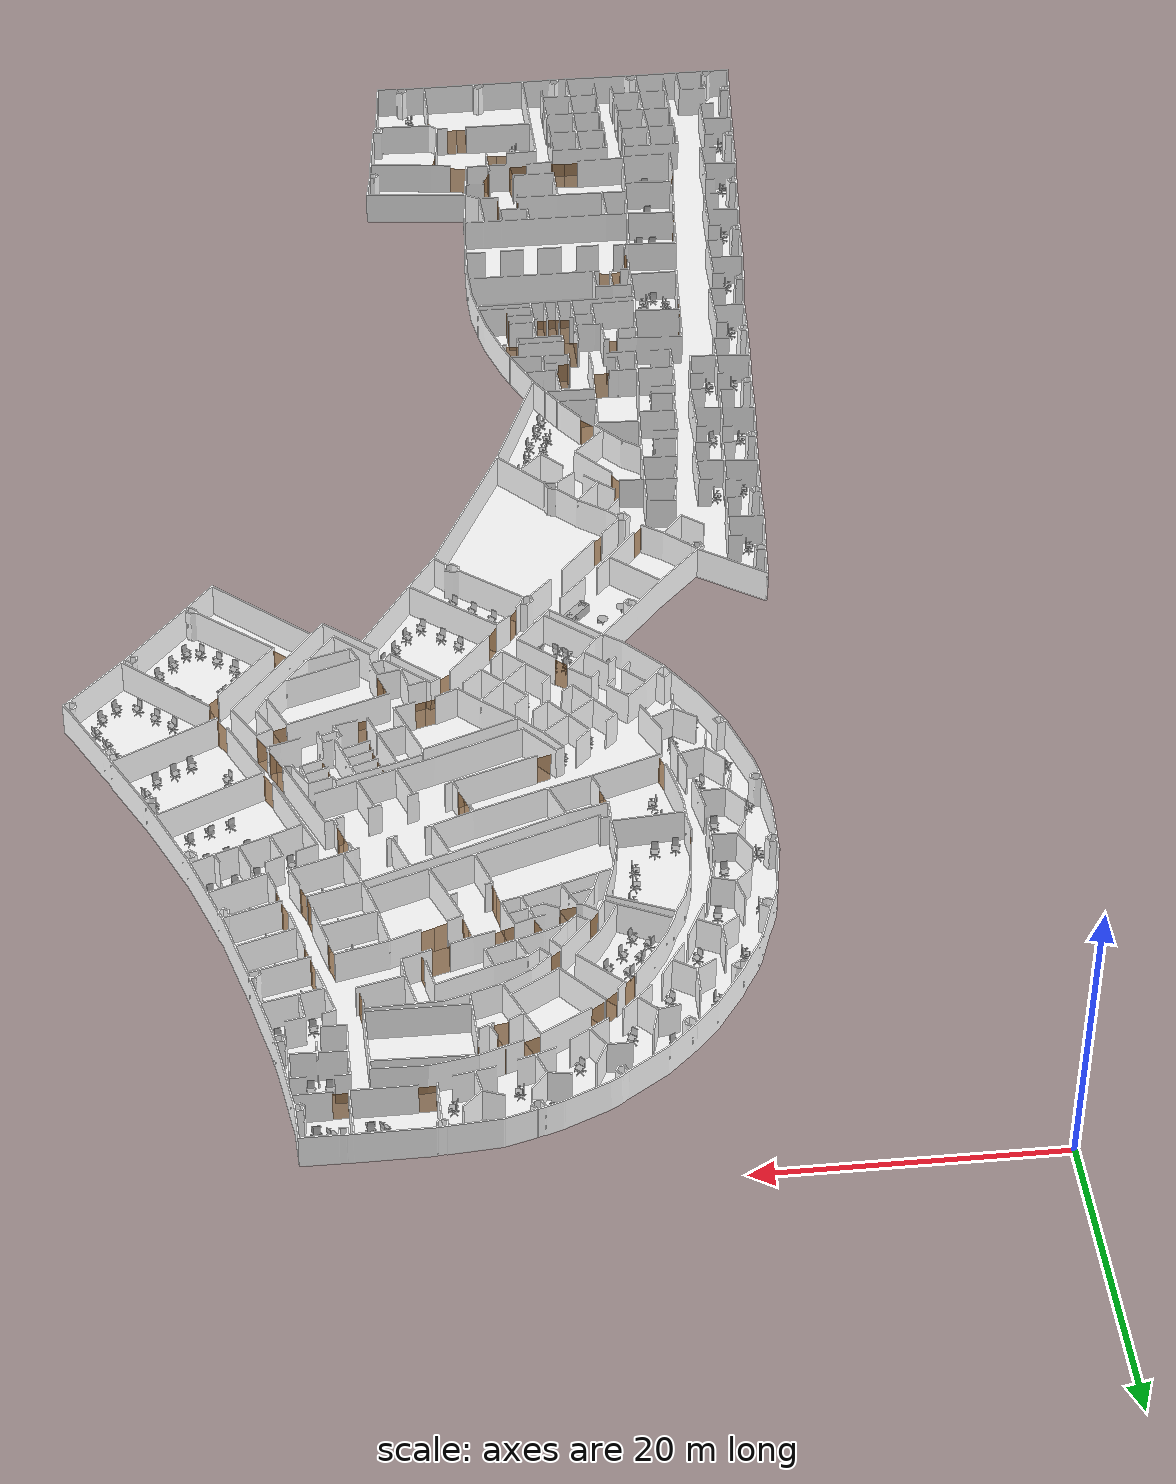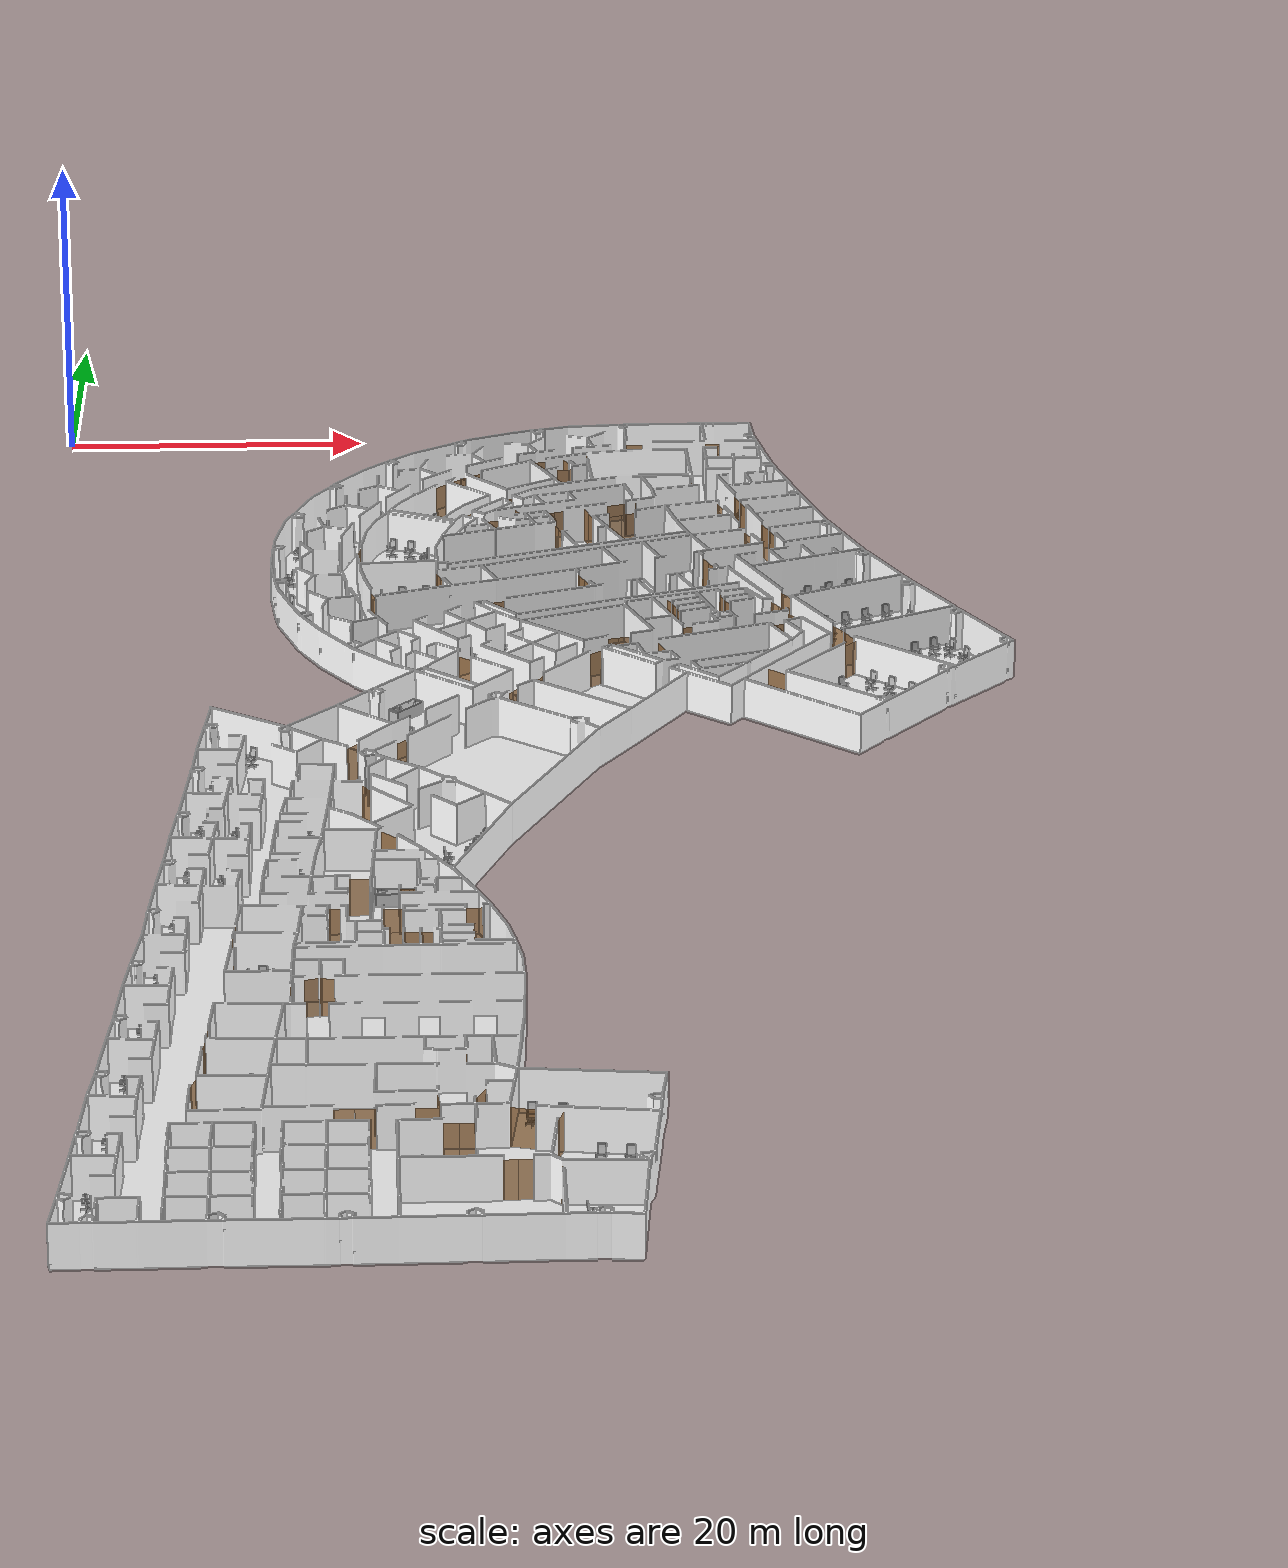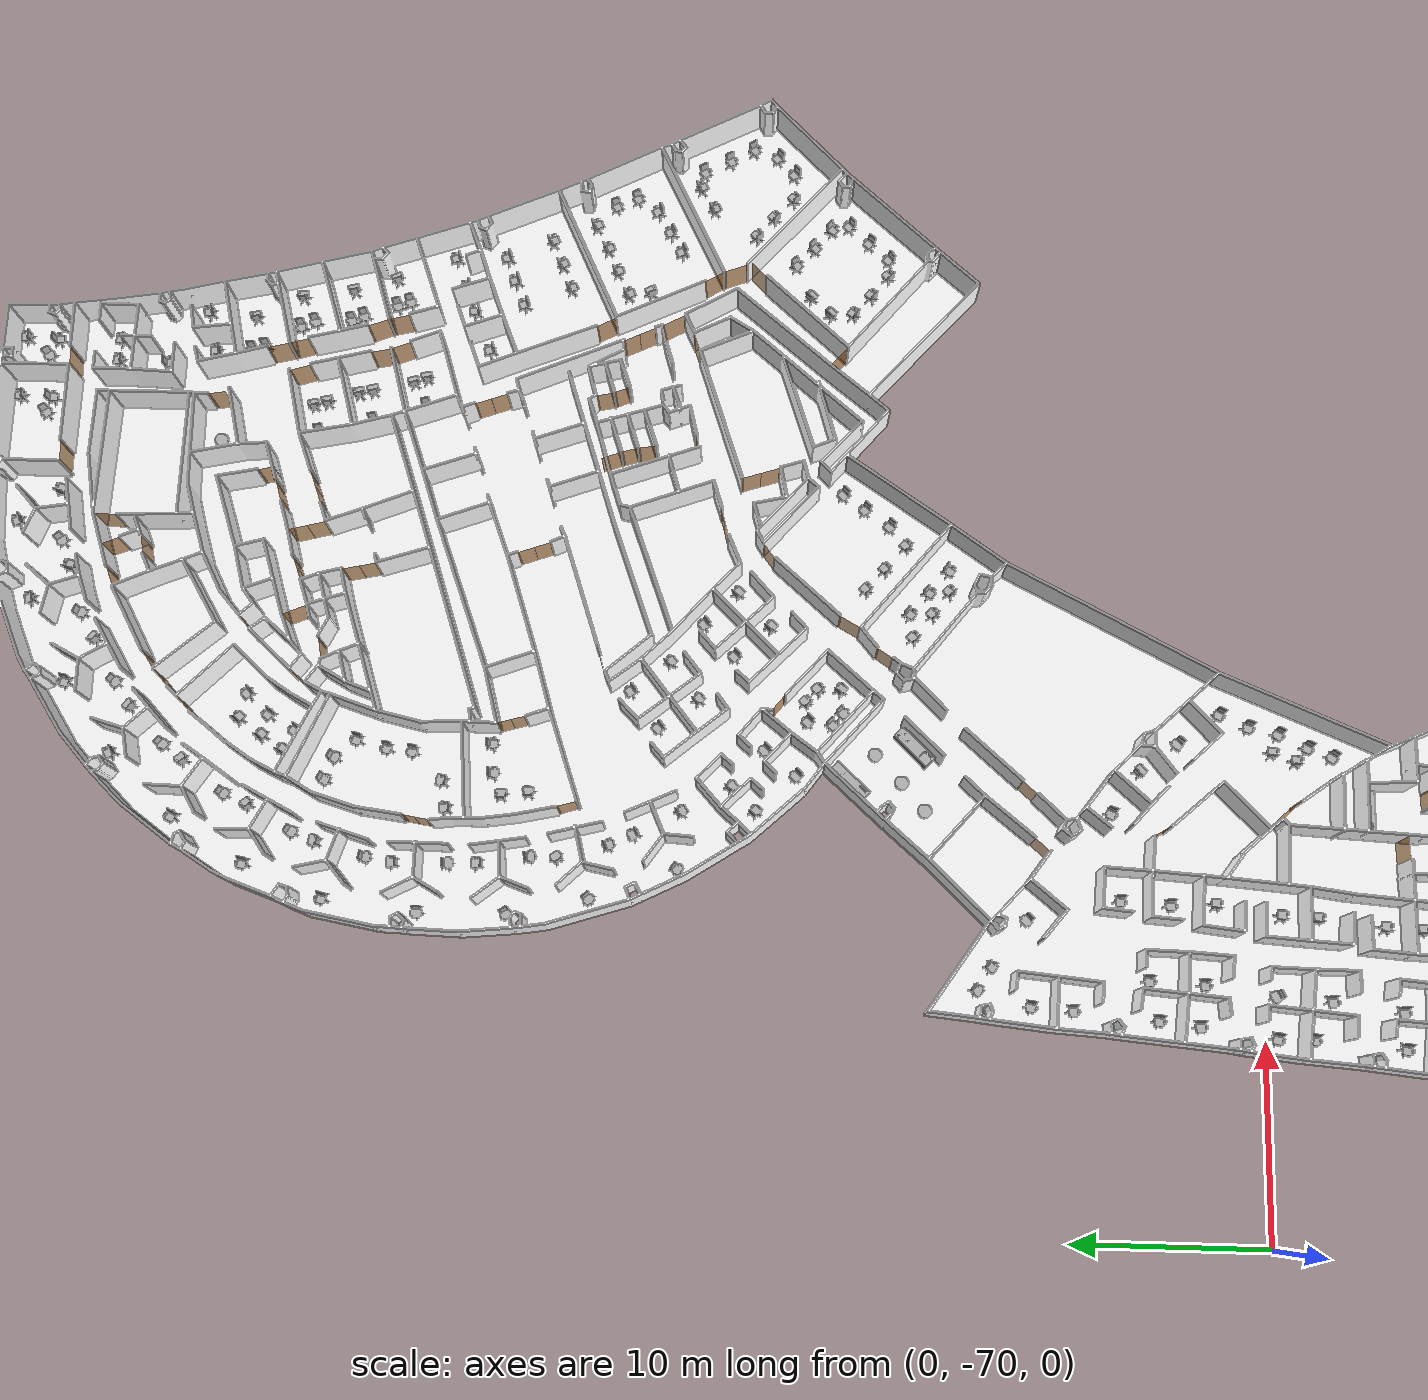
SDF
<sdf version="1.7">
 <world name="world">
  <scene><ambient>0.8 0.8 0.8 1.0</ambient><background>0 0 0</background><grid>false</grid></scene>
  <include><uri>model://sun</uri></include>
  <include>
   <name>OpenRobotics/OfficeChairBlue</name>
   <uri>model://OfficeChairBlue</uri>
   <pose>28.21482018315684 -102.00691728255538 0.0 0 0 -0.0498</pose>
   <static>True</static>
  </include>
  <include>
   <name>OpenRobotics/OfficeChairBlue_2</name>
   <uri>model://OfficeChairBlue</uri>
   <pose>29.76414738809558 -102.22124087923856 0.0 0 0 0.0036</pose>
   <static>True</static>
  </include>
  <include>
   <name>OpenRobotics/OfficeChairBlue_3</name>
   <uri>model://OfficeChairBlue</uri>
   <pose>31.478287081211857 -106.56777730961561 0.0 0 0 -0.0988</pose>
   <static>True</static>
  </include>
  <include>
   <name>OpenRobotics/OfficeChairBlue_4</name>
   <uri>model://OfficeChairBlue</uri>
   <pose>32.94004361804536 -106.73483519953945 0.0 0 0 -0.0909</pose>
   <static>True</static>
  </include>
  <include>
   <name>OpenRobotics/OfficeChairBlue_5</name>
   <uri>model://OfficeChairBlue</uri>
   <pose>22.90410824292371 -107.34760533610144 0.0 0 0 1.5708</pose>
   <static>True</static>
  </include>
  <include>
   <name>OpenRobotics/OfficeChairBlue_6</name>
   <uri>model://OfficeChairBlue</uri>
   <pose>22.97248072609818 -108.90804727968431 0.0 0 0 1.5708</pose>
   <static>True</static>
  </include>
  <include>
   <name>OpenRobotics/OfficeChairBlue_7</name>
   <uri>model://OfficeChairBlue</uri>
   <pose>30.84272611692503 -112.35720890215734 0.0 0 0 1.5708</pose>
   <static>True</static>
  </include>
  <include>
   <name>OpenRobotics/OfficeChairBlue_8</name>
   <uri>model://OfficeChairBlue</uri>
   <pose>22.97248072609818 -108.90804727968431 0.0 0 0 1.5708</pose>
   <static>True</static>
  </include>
  <include>
   <name>OpenRobotics/OfficeChairBlue_9</name>
   <uri>model://OfficeChairBlue</uri>
   <pose>19.261168449746016 -114.53827988841422 0.0 0 0 1.5708</pose>
   <static>True</static>
  </include>
  <include>
   <name>OpenRobotics/OfficeChairBlue_10</name>
   <uri>model://OfficeChairBlue</uri>
   <pose>22.97248072609818 -108.90804727968431 0.0 0 0 1.5708</pose>
   <static>True</static>
  </include>
  <include>
   <name>OpenRobotics/OfficeChairBlue_11</name>
   <uri>model://OfficeChairBlue</uri>
   <pose>16.427359175843208 -112.17140190765201 0.0 0 0 -1.6285</pose>
   <static>True</static>
  </include>
  <include>
   <name>OpenRobotics/OfficeChairBlue_12</name>
   <uri>model://OfficeChairBlue</uri>
   <pose>19.282836576597692 -112.09550732862748 0.0 0 0 1.5708</pose>
   <static>True</static>
  </include>
  <include>
   <name>OpenRobotics/OfficeChairBlue_13</name>
   <uri>model://OfficeChairBlue</uri>
   <pose>19.347953227240048 -109.65262249875342 0.0 0 0 1.5708</pose>
   <static>True</static>
  </include>
  <include>
   <name>OpenRobotics/OfficeChairBlue_14</name>
   <uri>model://OfficeChairBlue</uri>
   <pose>16.427359175843208 -109.70684895092627 0.0 0 0 -1.5575</pose>
   <static>True</static>
  </include>
  <include>
   <name>OpenRobotics/OfficeChairBlue_15</name>
   <uri>model://OfficeChairBlue</uri>
   <pose>19.31539490191887 -107.22062786734885 0.0 0 0 1.5708</pose>
   <static>True</static>
  </include>
  <include>
   <name>OpenRobotics/OfficeChairBlue_16</name>
   <uri>model://OfficeChairBlue</uri>
   <pose>16.449139572782205 -107.31830284331238 0.0 0 0 -1.5289</pose>
   <static>True</static>
  </include>
  <include>
   <name>OpenRobotics/OfficeChairBlue_17</name>
   <uri>model://OfficeChairBlue</uri>
   <pose>13.702227346460743 -107.16628914508868 0.0 0 0 1.5708</pose>
   <static>True</static>
  </include>
  <include>
   <name>OpenRobotics/OfficeChairBlue_18</name>
   <uri>model://OfficeChairBlue</uri>
   <pose>13.626220497348895 -109.71773914939577 0.0 0 0 1.5708</pose>
   <static>True</static>
  </include>
  <include>
   <name>OpenRobotics/OfficeChairBlue_19</name>
   <uri>model://OfficeChairBlue</uri>
   <pose>10.846749945706259 -107.23140579573104 0.0 0 0 -1.5505</pose>
   <static>True</static>
  </include>
  <include>
   <name>OpenRobotics/OfficeChairBlue_20</name>
   <uri>model://OfficeChairBlue</uri>
   <pose>10.814191620385083 -109.59828377649325 0.0 0 0 -1.6687</pose>
   <static>True</static>
  </include>
  <include>
   <name>OpenRobotics/OfficeChairBlue_21</name>
   <uri>model://OfficeChairBlue</uri>
   <pose>10.814191620385083 -112.29085728055453 0.0 0 0 -1.5637</pose>
   <static>True</static>
  </include>
  <include>
   <name>OpenRobotics/OfficeChairBlue_22</name>
   <uri>model://OfficeChairBlue</uri>
   <pose>10.911978866435927 -114.48405343624137 0.0 0 0 -1.6045</pose>
   <static>True</static>
  </include>
  <include>
   <name>OpenRobotics/OfficeChairBlue_23</name>
   <uri>model://OfficeChairBlue</uri>
   <pose>7.423185903140904 -114.65010089537937 0.0 0 0 -1.6313</pose>
   <static>True</static>
  </include>
  <include>
   <name>OpenRobotics/OfficeChairBlue_24</name>
   <uri>model://OfficeChairBlue</uri>
   <pose>13.65877882267007 -112.23663082838168 0.0 0 0 1.5708</pose>
   <static>True</static>
  </include>
  <include>
   <name>OpenRobotics/OfficeChairBlue_25</name>
   <uri>model://OfficeChairBlue</uri>
   <pose>13.65877882267007 -114.61428673752607 0.0 0 0 1.5708</pose>
   <static>True</static>
  </include>
  <include>
   <name>OpenRobotics/OfficeChairBlue_26</name>
   <uri>model://OfficeChairBlue</uri>
   <pose>13.310517011820798 -99.75084987797247 0.0 0 0 -0.0237</pose>
   <static>True</static>
  </include>
  <include>
   <name>OpenRobotics/OfficeChairBlue_27</name>
   <uri>model://OfficeChairBlue</uri>
   <pose>14.166351887418479 -93.77336588917912 0.0 0 0 3.0887</pose>
   <static>True</static>
  </include>
  <include>
   <name>OpenRobotics/OfficeChairBlue_28</name>
   <uri>model://OfficeChairBlue</uri>
   <pose>13.083170085009135 -103.45497686873651 0.0 0 0 -0.0022</pose>
   <static>True</static>
  </include>
  <include>
   <name>OpenRobotics/OfficeChairBlue_29</name>
   <uri>model://OfficeChairBlue</uri>
   <pose>6.143419177844043 -110.09979425652668 0.0 0 0 -1.4799</pose>
   <static>True</static>
  </include>
  <include>
   <name>OpenRobotics/OfficeChairBlue_30</name>
   <uri>model://OfficeChairBlue</uri>
   <pose>6.233010707520935 -107.85214710849236 0.0 0 0 -1.7433</pose>
   <static>True</static>
  </include>
  <include>
   <name>OpenRobotics/OfficeChairBlue_31</name>
   <uri>model://OfficeChairBlue</uri>
   <pose>6.868683941895076 -103.92460264397266 0.0 0 0 -1.641</pose>
   <static>True</static>
  </include>
  <include>
   <name>OpenRobotics/OfficeChairBlue_32</name>
   <uri>model://OfficeChairBlue</uri>
   <pose>6.937954585768061 -102.01690932032635 0.0 0 0 -1.6725</pose>
   <static>True</static>
  </include>
  <include>
   <name>OpenRobotics/OfficeChairBlue_33</name>
   <uri>model://OfficeChairBlue</uri>
   <pose>7.4930178974504615 -97.54260953058552 0.0 0 0 -1.5981</pose>
   <static>True</static>
  </include>
  <include>
   <name>OpenRobotics/OfficeChairBlue_34</name>
   <uri>model://OfficeChairBlue</uri>
   <pose>7.753147689757931 -95.7042991208995 0.0 0 0 -1.7676</pose>
   <static>True</static>
  </include>
  <include>
   <name>OpenRobotics/OfficeChairBlue_35</name>
   <uri>model://OfficeChairBlue</uri>
   <pose>8.140254950817987 -91.74666627297954 0.0 0 0 -1.4522</pose>
   <static>True</static>
  </include>
  <include>
   <name>OpenRobotics/OfficeChairBlue_36</name>
   <uri>model://OfficeChairBlue</uri>
   <pose>8.384105580464865 -89.21654758526219 0.0 0 0 -1.8611</pose>
   <static>True</static>
  </include>
  <include>
   <name>OpenRobotics/OfficeChairBlue_37</name>
   <uri>model://OfficeChairBlue</uri>
   <pose>8.810844182346905 -85.28406323690066 0.0 0 0 -1.6239</pose>
   <static>True</static>
  </include>
  <include>
   <name>OpenRobotics/OfficeChairBlue_38</name>
   <uri>model://OfficeChairBlue</uri>
   <pose>8.93928116223458 -83.33729992286894 0.0 0 0 -1.6802</pose>
   <static>True</static>
  </include>
  <include>
   <name>OpenRobotics/OfficeChairBlue_39</name>
   <uri>model://OfficeChairBlue</uri>
   <pose>9.451008220213621 -79.06531083046865 0.0 0 0 -1.7928</pose>
   <static>True</static>
  </include>
  <include>
   <name>OpenRobotics/OfficeChairBlue_40</name>
   <uri>model://OfficeChairBlue</uri>
   <pose>9.6948588498605 -76.8704306234721 0.0 0 0 -1.7484</pose>
   <static>True</static>
  </include>
  <include>
   <name>OpenRobotics/OfficeChairBlue_41</name>
   <uri>model://OfficeChairBlue</uri>
   <pose>11.52093182002924 -76.82900296125308 0.0 0 0 -1.6118</pose>
   <static>True</static>
  </include>
  <include>
   <name>OpenRobotics/OfficeChairBlue_42</name>
   <uri>model://OfficeChairBlue</uri>
   <pose>15.831205012203736 -77.99504008810045 0.0 0 0 1.5708</pose>
   <static>True</static>
  </include>
  <include>
   <name>OpenRobotics/OfficeChairBlue_43</name>
   <uri>model://OfficeChairBlue</uri>
   <pose>15.9213578923172 -76.1274271856254 0.0 0 0 1.5708</pose>
   <static>True</static>
  </include>
  <include>
   <name>OpenRobotics/OfficeChairBlue_44</name>
   <uri>model://OfficeChairBlue</uri>
   <pose>16.307791532853372 -72.72710305113412 0.0 0 0 1.5708</pose>
   <static>True</static>
  </include>
  <include>
   <name>OpenRobotics/OfficeChairBlue_45</name>
   <uri>model://OfficeChairBlue</uri>
   <pose>16.372234562971837 -70.8981110586952 0.0 0 0 1.5708</pose>
   <static>True</static>
  </include>
  <include>
   <name>OpenRobotics/OfficeChairBlue_46</name>
   <uri>model://OfficeChairBlue</uri>
   <pose>16.84870881353416 -67.58793980431739 0.0 0 0 1.5708</pose>
   <static>True</static>
  </include>
  <include>
   <name>OpenRobotics/OfficeChairBlue_47</name>
   <uri>model://OfficeChairBlue</uri>
   <pose>16.552540323198766 -65.29527235127001 0.0 0 0 -1.5886</pose>
   <static>True</static>
  </include>
  <include>
   <name>OpenRobotics/OfficeChairBlue_48</name>
   <uri>model://OfficeChairBlue</uri>
   <pose>16.69422517338954 -62.74494504783607 0.0 0 0 -1.6735</pose>
   <static>True</static>
  </include>
  <include>
   <name>OpenRobotics/OfficeChairBlue_49</name>
   <uri>model://OfficeChairBlue</uri>
   <pose>10.55417409816493 -66.64217658878087 0.0 0 0 -1.6208</pose>
   <static>True</static>
  </include>
  <include>
   <name>OpenRobotics/OfficeChairBlue_50</name>
   <uri>model://OfficeChairBlue</uri>
   <pose>10.779724703579562 -64.57775422324367 0.0 0 0 -1.7139</pose>
   <static>True</static>
  </include>
  <include>
   <name>OpenRobotics/OfficeChairBlue_51</name>
   <uri>model://OfficeChairBlue</uri>
   <pose>12.740072698176325 -64.12676528250172 0.0 0 0 -1.6673</pose>
   <static>True</static>
  </include>
  <include>
   <name>OpenRobotics/OfficeChairBlue_52</name>
   <uri>model://OfficeChairBlue</uri>
   <pose>12.618596463702142 -66.9198205147094 0.0 0 0 -1.6967</pose>
   <static>True</static>
  </include>
  <include>
   <name>OpenRobotics/OfficeChairBlue_53</name>
   <uri>model://OfficeChairBlue</uri>
   <pose>11.161330730361213 -60.31003139416133 0.0 0 0 -1.5084</pose>
   <static>True</static>
  </include>
  <include>
   <name>OpenRobotics/OfficeChairBlue_54</name>
   <uri>model://OfficeChairBlue</uri>
   <pose>11.300096558281812 -58.17622611466382 0.0 0 0 -1.7682</pose>
   <static>True</static>
  </include>
  <include>
   <name>OpenRobotics/OfficeChairBlue_55</name>
   <uri>model://OfficeChairBlue</uri>
   <pose>15.637090031237138 -57.9461847057566 0.0 0 0 -2.362</pose>
   <static>True</static>
  </include>
  <include>
   <name>OpenRobotics/OfficeChairBlue_56</name>
   <uri>model://OfficeChairBlue</uri>
   <pose>12.082394526688562 -55.5644870734689 0.0 0 0 -0.6947</pose>
   <static>True</static>
  </include>
  <include>
   <name>OpenRobotics/OfficeChairBlue_57</name>
   <uri>model://OfficeChairBlue</uri>
   <pose>13.267293028204753 -56.287281895599016 0.0 0 0 -0.6288</pose>
   <static>True</static>
  </include>
  <include>
   <name>OpenRobotics/OfficeChairBlue_58</name>
   <uri>model://OfficeChairBlue</uri>
   <pose>10.051091836909096 -72.29778223724385 0.0 0 0 -1.7127</pose>
   <static>True</static>
  </include>
  <include>
   <name>OpenRobotics/OfficeChairBlue_59</name>
   <uri>model://OfficeChairBlue</uri>
   <pose>10.051091836909096 -70.45891047712126 0.0 0 0 -1.8116</pose>
   <static>True</static>
  </include>
  <include>
   <name>OpenRobotics/OfficeChairBlue_60</name>
   <uri>model://OfficeChairBlue</uri>
   <pose>12.18489711640661 -70.40681715660739 0.0 0 0 -2.6591</pose>
   <static>True</static>
  </include>
  <include>
   <name>OpenRobotics/OfficeChairBlue_61</name>
   <uri>model://OfficeChairBlue</uri>
   <pose>11.959346510991976 -73.2866571663091 0.0 0 0 -1.4995</pose>
   <static>True</static>
  </include>
  <include>
   <name>OpenRobotics/OfficeChairBlue_62</name>
   <uri>model://OfficeChairBlue</uri>
   <pose>15.320151574748582 -86.06119678129093 0.0 0 0 1.6053</pose>
   <static>True</static>
  </include>
  <include>
   <name>OpenRobotics/OfficeChairBlue_63</name>
   <uri>model://OfficeChairBlue</uri>
   <pose>15.222476598785052 -87.67833511896757 0.0 0 0 1.5708</pose>
   <static>True</static>
  </include>
  <include>
   <name>OpenRobotics/OfficeChairBlue_64</name>
   <uri>model://OfficeChairBlue</uri>
   <pose>13.279755007896652 -85.9635218053274 0.0 0 0 -1.7895</pose>
   <static>True</static>
  </include>
  <include>
   <name>OpenRobotics/OfficeChairBlue_65</name>
   <uri>model://OfficeChairBlue</uri>
   <pose>13.366539785390684 -87.50476556397952 0.0 0 0 -1.5708</pose>
   <static>True</static>
  </include>
  <include>
   <name>OpenRobotics/OfficeChairBlue_66</name>
   <uri>model://OfficeChairBlue</uri>
   <pose>26.473398858823156 -67.98560045358501 0.0 0 0 -2.0241</pose>
   <static>True</static>
  </include>
  <include>
   <name>OpenRobotics/OfficeChairBlue_67</name>
   <uri>model://OfficeChairBlue</uri>
   <pose>25.83570476287736 -69.47362819085008 0.0 0 0 -1.8991</pose>
   <static>True</static>
  </include>
  <include>
   <name>OpenRobotics/OfficeChairBlue_68</name>
   <uri>model://OfficeChairBlue</uri>
   <pose>24.745225404792574 -70.70534331877639 0.0 0 0 1.5708</pose>
   <static>True</static>
  </include>
  <include>
   <name>OpenRobotics/OfficeChairBlue_69</name>
   <uri>model://OfficeChairBlue</uri>
   <pose>24.32140582518071 -71.9294240807653 0.0 0 0 1.5708</pose>
   <static>True</static>
  </include>
  <include>
   <name>OpenRobotics/OfficeChairBlue_70</name>
   <uri>model://OfficeChairBlue</uri>
   <pose>21.15269488081905 -62.34189543437736 0.0 0 0 -1.9224</pose>
   <static>True</static>
  </include>
  <include>
   <name>OpenRobotics/OfficeChairBlue_71</name>
   <uri>model://OfficeChairBlue</uri>
   <pose>23.56841034956302 -63.94870492402107 0.0 0 0 0.6892</pose>
   <static>True</static>
  </include>
  <include>
   <name>OpenRobotics/OfficeChairBlue_72</name>
   <uri>model://OfficeChairBlue</uri>
   <pose>24.898137263714794 -65.77713556602342 0.0 0 0 -2.3463</pose>
   <static>True</static>
  </include>
  <include>
   <name>OpenRobotics/KitchenCountertop</name>
   <uri>model://KitchenCountertop</uri>
   <pose>22.525758048674177 -48.948859908380484 0.0 0 0 2.3925</pose>
   <static>True</static>
  </include>
  <include>
   <name>OpenRobotics/OfficeChairBlue_73</name>
   <uri>model://OfficeChairBlue</uri>
   <pose>48.36999533818743 -48.72465654401363 0.0 0 0 2.553</pose>
   <static>True</static>
  </include>
  <include>
   <name>OpenRobotics/OfficeChairBlue_74</name>
   <uri>model://OfficeChairBlue</uri>
   <pose>49.47967288120297 -49.69444555823542 0.0 0 0 2.4515</pose>
   <static>True</static>
  </include>
  <include>
   <name>OpenRobotics/OfficeChairBlue_75</name>
   <uri>model://OfficeChairBlue</uri>
   <pose>50.635942510453994 -50.59900565172755 0.0 0 0 2.3486</pose>
   <static>True</static>
  </include>
  <include>
   <name>OpenRobotics/OfficeChairBlue_76</name>
   <uri>model://OfficeChairBlue</uri>
   <pose>52.38915219395568 -49.563875446688776 0.0 0 0 -2.2868</pose>
   <static>True</static>
  </include>
  <include>
   <name>OpenRobotics/OfficeChairBlue_77</name>
   <uri>model://OfficeChairBlue</uri>
   <pose>53.153711488566756 -47.67088950448065 0.0 0 0 -0.7474</pose>
   <static>True</static>
  </include>
  <include>
   <name>OpenRobotics/OfficeChairBlue_78</name>
   <uri>model://OfficeChairBlue</uri>
   <pose>52.04403394555121 -46.73848642933454 0.0 0 0 -0.7463</pose>
   <static>True</static>
  </include>
  <include>
   <name>OpenRobotics/OfficeChairBlue_79</name>
   <uri>model://OfficeChairBlue</uri>
   <pose>50.99969759335266 -45.76858514502544 0.0 0 0 -0.8369</pose>
   <static>True</static>
  </include>
  <include>
   <name>OpenRobotics/OfficeChairBlue_80</name>
   <uri>model://OfficeChairBlue</uri>
   <pose>49.34910276965633 -46.607916317787904 0.0 0 0 0.7941</pose>
   <static>True</static>
  </include>
  <include>
   <name>OpenRobotics/OfficeChairBlue_81</name>
   <uri>model://OfficeChairBlue</uri>
   <pose>55.10227112399551 -45.37373124794069 0.0 0 0 2.3244</pose>
   <static>True</static>
  </include>
  <include>
   <name>OpenRobotics/OfficeChairBlue_82</name>
   <uri>model://OfficeChairBlue</uri>
   <pose>53.957003963301304 -44.30132737391352 0.0 0 0 2.378</pose>
   <static>True</static>
  </include>
  <include>
   <name>OpenRobotics/OfficeChairBlue_83</name>
   <uri>model://OfficeChairBlue</uri>
   <pose>52.842947886880495 -43.39553230946093 0.0 0 0 2.3201</pose>
   <static>True</static>
  </include>
  <include>
   <name>OpenRobotics/OfficeChairBlue_84</name>
   <uri>model://OfficeChairBlue</uri>
   <pose>57.38236432726369 -44.45749506536786 0.0 0 0 -2.3892</pose>
   <static>True</static>
  </include>
  <include>
   <name>OpenRobotics/OfficeChairBlue_85</name>
   <uri>model://OfficeChairBlue</uri>
   <pose>57.111681146748666 -41.9795819682517 0.0 0 0 -1.11</pose>
   <static>True</static>
  </include>
  <include>
   <name>OpenRobotics/OfficeChairBlue_86</name>
   <uri>model://OfficeChairBlue</uri>
   <pose>56.39326485802381 -40.56363162704247 0.0 0 0 -1.0903</pose>
   <static>True</static>
  </include>
  <include>
   <name>OpenRobotics/OfficeChairBlue_87</name>
   <uri>model://OfficeChairBlue</uri>
   <pose>54.35365418178308 -41.21535948390257 0.0 0 0 0.4537</pose>
   <static>True</static>
  </include>
  <include>
   <name>OpenRobotics/OfficeChairBlue_88</name>
   <uri>model://OfficeChairBlue</uri>
   <pose>49.415005310909876 -37.72061620597989 0.0 0 0 2.0531</pose>
   <static>True</static>
  </include>
  <include>
   <name>OpenRobotics/OfficeChairBlue_89</name>
   <uri>model://OfficeChairBlue</uri>
   <pose>50.50323926724837 -36.04217840062959 0.0 0 0 0.344</pose>
   <static>True</static>
  </include>
  <include>
   <name>OpenRobotics/OfficeChairBlue_90</name>
   <uri>model://OfficeChairBlue</uri>
   <pose>51.8404882772502 -35.47959299309712 0.0 0 0 0.4023</pose>
   <static>True</static>
  </include>
  <include>
   <name>OpenRobotics/OfficeChairBlue_91</name>
   <uri>model://OfficeChairBlue</uri>
   <pose>54.717858345031 -36.91833416203117 0.0 0 0 -1.0804</pose>
   <static>True</static>
  </include>
  <include>
   <name>OpenRobotics/OfficeChairBlue_92</name>
   <uri>model://OfficeChairBlue</uri>
   <pose>54.00775004276741 -37.923488253757014 0.0 0 0 -2.6898</pose>
   <static>True</static>
  </include>
  <include>
   <name>OpenRobotics/OfficeChairBlue_93</name>
   <uri>model://OfficeChairBlue</uri>
   <pose>52.771993191697796 -38.6429149732677 0.0 0 0 -2.6684</pose>
   <static>True</static>
  </include>
  <include>
   <name>OpenRobotics/OfficeChairBlue_94</name>
   <uri>model://OfficeChairBlue</uri>
   <pose>49.45778021417666 -33.55505915635365 0.0 0 0 0.4189</pose>
   <static>True</static>
  </include>
  <include>
   <name>OpenRobotics/OfficeChairBlue_95</name>
   <uri>model://OfficeChairBlue</uri>
   <pose>50.84644892416849 -33.01290690471241 0.0 0 0 0.4432</pose>
   <static>True</static>
  </include>
  <include>
   <name>OpenRobotics/OfficeChairBlue_96</name>
   <uri>model://OfficeChairBlue</uri>
   <pose>52.19537402325103 -32.43101104216186 0.0 0 0 0.4397</pose>
   <static>True</static>
  </include>
  <include>
   <name>OpenRobotics/OfficeChairBlue_97</name>
   <uri>model://OfficeChairBlue</uri>
   <pose>48.320484229681774 -30.830713217582392 0.0 0 0 -2.7725</pose>
   <static>True</static>
  </include>
  <include>
   <name>OpenRobotics/OfficeChairBlue_98</name>
   <uri>model://OfficeChairBlue</uri>
   <pose>49.709040669586294 -30.26206522533495 0.0 0 0 -2.7775</pose>
   <static>True</static>
  </include>
  <include>
   <name>OpenRobotics/OfficeChairBlue_99</name>
   <uri>model://OfficeChairBlue</uri>
   <pose>51.04483016845304 -29.75954431451569 0.0 0 0 -2.7813</pose>
   <static>True</static>
  </include>
  <include>
   <name>OpenRobotics/OfficeChairBlue_100</name>
   <uri>model://OfficeChairBlue</uri>
   <pose>49.316993524684406 -27.619339640041254 0.0 0 0 -2.7998</pose>
   <static>True</static>
  </include>
  <include>
   <name>OpenRobotics/OfficeChairBlue_101</name>
   <uri>model://OfficeChairBlue</uri>
   <pose>50.946257031791 -26.985799537326088 0.0 0 0 -2.8187</pose>
   <static>True</static>
  </include>
  <include>
   <name>OpenRobotics/OfficeChairBlue_102</name>
   <uri>model://OfficeChairBlue</uri>
   <pose>47.895991029546025 -28.16239005238101 0.0 0 0 -2.9932</pose>
   <static>True</static>
  </include>
  <include>
   <name>OpenRobotics/OfficeChairBlue_103</name>
   <uri>model://OfficeChairBlue</uri>
   <pose>45.633187419724266 -29.10377473451227 0.0 0 0 -2.7887</pose>
   <static>True</static>
  </include>
  <include>
   <name>OpenRobotics/OfficeChairBlue_104</name>
   <uri>model://OfficeChairBlue</uri>
   <pose>32.872906105831355 -49.6062012696063 0.0 0 0 2.4039</pose>
   <static>True</static>
  </include>
  <include>
   <name>OpenRobotics/OfficeChairBlue_105</name>
   <uri>model://OfficeChairBlue</uri>
   <pose>33.998189190983595 -50.59586208928275 0.0 0 0 2.4415</pose>
   <static>True</static>
  </include>
  <include>
   <name>OpenRobotics/OfficeChairBlue_106</name>
   <uri>model://OfficeChairBlue</uri>
   <pose>37.08920923492369 -49.524917726390676 0.0 0 0 -2.2963</pose>
   <static>True</static>
  </include>
  <include>
   <name>OpenRobotics/OfficeChairBlue_107</name>
   <uri>model://OfficeChairBlue</uri>
   <pose>37.902606017516526 -48.372465280108344 0.0 0 0 -2.3196</pose>
   <static>True</static>
  </include>
  <include>
   <name>OpenRobotics/OfficeChairBlue_108</name>
   <uri>model://OfficeChairBlue</uri>
   <pose>26.74251025811578 -46.57176534967267 0.0 0 0 2.3927</pose>
   <static>True</static>
  </include>
  <include>
   <name>OpenRobotics/OfficeChairBlue_109</name>
   <uri>model://OfficeChairBlue</uri>
   <pose>25.41255880378938 -48.10346615090304 0.0 0 0 -0.8184</pose>
   <static>True</static>
  </include>
  <include>
   <name>OpenRobotics/OfficeChairBlue_110</name>
   <uri>model://OfficeChairBlue</uri>
   <pose>25.554468194154783 -46.698855088512566 0.0 0 0 -2.2809</pose>
   <static>True</static>
  </include>
  <include>
   <name>OpenRobotics/OfficeChairBlue_111</name>
   <uri>model://OfficeChairBlue</uri>
   <pose>27.452281750117425 -48.51437467047375 0.0 0 0 0.8254</pose>
   <static>True</static>
  </include>
  <include>
   <name>OpenRobotics/OfficeChairBlue_112</name>
   <uri>model://OfficeChairBlue</uri>
   <pose>28.684109148131032 -39.6439150717629 0.0 0 0 0.6948</pose>
   <static>True</static>
  </include>
  <include>
   <name>OpenRobotics/OfficeChairBlue_113</name>
   <uri>model://OfficeChairBlue</uri>
   <pose>26.942238743448097 -37.48002140886513 0.0 0 0 -2.4646</pose>
   <static>True</static>
  </include>
  <include>
   <name>OpenRobotics/OfficeChairBlue_114</name>
   <uri>model://OfficeChairBlue</uri>
   <pose>25.029830076134587 -38.97051908805111 0.0 0 0 -2.4364</pose>
   <static>True</static>
  </include>
  <include>
   <name>OpenRobotics/OfficeChairBlue_115</name>
   <uri>model://OfficeChairBlue</uri>
   <pose>26.735774052876913 -41.14328208784673 0.0 0 0 0.7381</pose>
   <static>True</static>
  </include>
  <include>
   <name>OpenRobotics/OfficeChairBlue_116</name>
   <uri>model://OfficeChairBlue</uri>
   <pose>28.92728615725403 -42.818688600839536 0.0 0 0 -2.37</pose>
   <static>True</static>
  </include>
  <include>
   <name>OpenRobotics/OfficeChairBlue_117</name>
   <uri>model://OfficeChairBlue</uri>
   <pose>30.73461002284126 -44.81619799433737 0.0 0 0 0.7963</pose>
   <static>True</static>
  </include>
  <include>
   <name>OpenRobotics/OfficeChairBlue_118</name>
   <uri>model://OfficeChairBlue</uri>
   <pose>32.519367600878304 -43.06175333987522 0.0 0 0 0.7655</pose>
   <static>True</static>
  </include>
  <include>
   <name>OpenRobotics/OfficeChairBlue_119</name>
   <uri>model://OfficeChairBlue</uri>
   <pose>30.607969364350616 -41.177299924302986 0.0 0 0 -2.4251</pose>
   <static>True</static>
  </include>
  <include>
   <name>OpenRobotics/OfficeChairBlue_120</name>
   <uri>model://OfficeChairBlue</uri>
   <pose>23.991444038563685 -44.511946057715335 0.0 0 0 -2.3243</pose>
   <static>True</static>
  </include>
  <include>
   <name>OpenRobotics/OfficeChairBlue_121</name>
   <uri>model://OfficeChairBlue</uri>
   <pose>22.699552143836872 -46.1455880982272 0.0 0 0 -2.3439</pose>
   <static>True</static>
  </include>
  <include>
   <name>OpenRobotics/OfficeChairBlue_122</name>
   <uri>model://OfficeChairBlue</uri>
   <pose>20.955885417756903 -44.23396532152488 0.0 0 0 0.8653</pose>
   <static>True</static>
  </include>
  <include>
   <name>OpenRobotics/OfficeChairBlue_123</name>
   <uri>model://OfficeChairBlue</uri>
   <pose>22.195571721882523 -42.98844097285891 0.0 0 0 0.6967</pose>
   <static>True</static>
  </include>
  <include>
   <name>OpenRobotics/OfficeChairBlue_124</name>
   <uri>model://OfficeChairBlue</uri>
   <pose>21.50095669166832 -31.112735676916166 0.0 0 0 1.5708</pose>
   <static>True</static>
  </include>
  <include>
   <name>OpenRobotics/OfficeChairBlue_125</name>
   <uri>model://OfficeChairBlue</uri>
   <pose>24.037137964100648 -30.61930864316937 0.0 0 0 0.0191</pose>
   <static>True</static>
  </include>
  <include>
   <name>OpenRobotics/OfficeChairBlue_126</name>
   <uri>model://OfficeChairBlue</uri>
   <pose>22.04221078261105 -27.9284191904178 0.0 0 0 3.045</pose>
   <static>True</static>
  </include>
  <include>
   <name>OpenRobotics/OfficeChairBlue_127</name>
   <uri>model://OfficeChairBlue</uri>
   <pose>23.428185010507335 -26.42938898459591 0.0 0 0 -1.6897</pose>
   <static>True</static>
  </include>
  <include>
   <name>OpenRobotics/OfficeChairBlue_128</name>
   <uri>model://OfficeChairBlue</uri>
   <pose>23.556509720307695 -25.082147936823095 0.0 0 0 -1.729</pose>
   <static>True</static>
  </include>
  <include>
   <name>OpenRobotics/OfficeChairBlue_129</name>
   <uri>model://OfficeChairBlue</uri>
   <pose>23.97718573747476 -23.49768019455495 0.0 0 0 -1.848</pose>
   <static>True</static>
  </include>
  <include>
   <name>OpenRobotics/OfficeChairBlue_130</name>
   <uri>model://OfficeChairBlue</uri>
   <pose>21.908721648794227 -22.083526174742747 0.0 0 0 -0.4761</pose>
   <static>True</static>
  </include>
  <include>
   <name>OpenRobotics/OfficeChairBlue_131</name>
   <uri>model://OfficeChairBlue</uri>
   <pose>25.123687869129423 -17.404558015827757 0.0 0 0 0.8403</pose>
   <static>True</static>
  </include>
  <include>
   <name>OpenRobotics/OfficeChairBlue_132</name>
   <uri>model://OfficeChairBlue</uri>
   <pose>24.249103888950238 -18.64559156100115 0.0 0 0 0.9028</pose>
   <static>True</static>
  </include>
  <include>
   <name>OpenRobotics/OfficeChairBlue_133</name>
   <uri>model://OfficeChairBlue</uri>
   <pose>42.39733896314859 -3.9757083319775814 0.0 0 0 -3.1416</pose>
   <static>True</static>
  </include>
  <include>
   <name>OpenRobotics/OfficeChairBlue_134</name>
   <uri>model://OfficeChairBlue</uri>
   <pose>45.758593107254455 -3.9657162942065995 0.0 0 0 3.1378</pose>
   <static>True</static>
  </include>
  <include>
   <name>OpenRobotics/OfficeChairBlue_135</name>
   <uri>model://OfficeChairBlue</uri>
   <pose>47.40873885060152 -16.38177752039356 0.0 0 0 1.7846</pose>
   <static>True</static>
  </include>
  <include>
   <name>OpenRobotics/OfficeChairBlue_136</name>
   <uri>model://OfficeChairBlue</uri>
   <pose>49.82467885952013 -23.873560446883566 0.0 0 0 1.9757</pose>
   <static>True</static>
  </include>
  <include>
   <name>OpenRobotics/OfficeChairBlue_137</name>
   <uri>model://OfficeChairBlue</uri>
   <pose>49.107834352017676 -21.567532853445762 0.0 0 0 1.8417</pose>
   <static>True</static>
  </include>
  <include>
   <name>OpenRobotics/OfficeChairBlue_138</name>
   <uri>model://OfficeChairBlue</uri>
   <pose>48.658641732672756 -18.860925588470174 0.0 0 0 1.5708</pose>
   <static>True</static>
  </include>
  <include>
   <name>OpenRobotics/OfficeChairBlue_139</name>
   <uri>model://OfficeChairBlue</uri>
   <pose>40.666358756935146 -20.343227551282215 0.0 0 0 -1.3468</pose>
   <static>True</static>
  </include>
  <include>
   <name>OpenRobotics/OfficeChairBlue_140</name>
   <uri>model://OfficeChairBlue</uri>
   <pose>41.3839891550488 -23.201736244394187 0.0 0 0 -1.312</pose>
   <static>True</static>
  </include>
  <include>
   <name>OpenRobotics/OfficeChairBlue_141</name>
   <uri>model://OfficeChairBlue</uri>
   <pose>42.30494068128884 -26.000517251054898 0.0 0 0 -1.2952</pose>
   <static>True</static>
  </include>
  <include>
   <name>OpenRobotics/OfficeChairBlue_142</name>
   <uri>model://OfficeChairBlue</uri>
   <pose>44.58267621272341 -9.063676418978936 0.0 0 0 3.0971</pose>
   <static>True</static>
  </include>
  <include>
   <name>OpenRobotics/OfficeChairBlue_143</name>
   <uri>model://OfficeChairBlue</uri>
   <pose>45.7511832814917 -9.097357445173259 0.0 0 0 -3.1278</pose>
   <static>True</static>
  </include>
  <include>
   <name>OpenRobotics/OfficeChairBlue_144</name>
   <uri>model://OfficeChairBlue</uri>
   <pose>44.49274787278458 -12.018737387181297 0.0 0 0 0.0186</pose>
   <static>True</static>
  </include>
  <include>
   <name>OpenRobotics/OfficeChairBlue_145</name>
   <uri>model://OfficeChairBlue</uri>
   <pose>45.24978507154558 -14.284684559447859 0.0 0 0 -3.0086</pose>
   <static>True</static>
  </include>
  <include>
   <name>OpenRobotics/OfficeChairBlue_146</name>
   <uri>model://OfficeChairBlue</uri>
   <pose>47.46071990102809 -13.726140875058713 0.0 0 0 -2.9772</pose>
   <static>True</static>
  </include>
  <include>
   <name>OpenRobotics/OfficeChairBlue_147</name>
   <uri>model://OfficeChairBlue</uri>
   <pose>18.317538365868472 -34.050507051672106 0.0 0 0 2.1803</pose>
   <static>True</static>
  </include>
  <include>
   <name>OpenRobotics/OfficeChairBlue_148</name>
   <uri>model://OfficeChairBlue</uri>
   <pose>18.25713705889332 -32.83316249492205 0.0 0 0 0.1423</pose>
   <static>True</static>
  </include>
  <include>
   <name>OpenRobotics/OfficeChairBlue_149</name>
   <uri>model://OfficeChairBlue</uri>
   <pose>17.84364632731438 -29.96297771272938 0.0 0 0 -3.1148</pose>
   <static>True</static>
  </include>
  <include>
   <name>OpenRobotics/OfficeChairBlue_150</name>
   <uri>model://OfficeChairBlue</uri>
   <pose>17.79503337950725 -28.673892570185426 0.0 0 0 0.0683</pose>
   <static>True</static>
  </include>
  <include>
   <name>OpenRobotics/OfficeChairBlue_151</name>
   <uri>model://OfficeChairBlue</uri>
   <pose>17.77067077056002 -25.63350633562412 0.0 0 0 -3.0884</pose>
   <static>True</static>
  </include>
  <include>
   <name>OpenRobotics/OfficeChairBlue_152</name>
   <uri>model://OfficeChairBlue</uri>
   <pose>17.989597440823104 -24.46600969764166 0.0 0 0 -0.1563</pose>
   <static>True</static>
  </include>
  <include>
   <name>OpenRobotics/OfficeChairBlue_153</name>
   <uri>model://OfficeChairBlue</uri>
   <pose>18.783683768397864 -21.61008321653792 0.0 0 0 2.9724</pose>
   <static>True</static>
  </include>
  <include>
   <name>OpenRobotics/OfficeChairBlue_154</name>
   <uri>model://OfficeChairBlue</uri>
   <pose>19.15709407880556 -20.598641999922474 0.0 0 0 -0.4997</pose>
   <static>True</static>
  </include>
  <include>
   <name>OpenRobotics/OfficeChairBlue_155</name>
   <uri>model://OfficeChairBlue</uri>
   <pose>20.64085555275269 -18.044722053694475 0.0 0 0 2.2101</pose>
   <static>True</static>
  </include>
  <include>
   <name>OpenRobotics/OfficeChairBlue_156</name>
   <uri>model://OfficeChairBlue</uri>
   <pose>21.029983675384408 -16.974563581413598 0.0 0 0 -0.5447</pose>
   <static>True</static>
  </include>
  <include>
   <name>OpenRobotics/OfficeChairBlue_157</name>
   <uri>model://OfficeChairBlue</uri>
   <pose>22.878510663016026 -14.49361919193996 0.0 0 0 2.2524</pose>
   <static>True</static>
  </include>
  <include>
   <name>OpenRobotics/OfficeChairBlue_158</name>
   <uri>model://OfficeChairBlue</uri>
   <pose>23.4918421500146 -13.592764011329203 0.0 0 0 -0.7062</pose>
   <static>True</static>
  </include>
  <include>
   <name>OpenRobotics/OfficeChairBlue_159</name>
   <uri>model://OfficeChairBlue</uri>
   <pose>25.620819815757592 -11.526994404744217 0.0 0 0 2.483</pose>
   <static>True</static>
  </include>
  <include>
   <name>OpenRobotics/OfficeChairBlue_160</name>
   <uri>model://OfficeChairBlue</uri>
   <pose>26.738356264885144 -10.831593483918814 0.0 0 0 -0.6219</pose>
   <static>True</static>
  </include>
  <include>
   <name>OpenRobotics/OfficeChairBlue_161</name>
   <uri>model://OfficeChairBlue</uri>
   <pose>29.166645983408333 -9.335482300367103 0.0 0 0 2.3758</pose>
   <static>True</static>
  </include>
  <include>
   <name>OpenRobotics/OfficeChairBlue_162</name>
   <uri>model://OfficeChairBlue</uri>
   <pose>30.394319388191313 -8.704748949834796 0.0 0 0 -0.4194</pose>
   <static>True</static>
  </include>
  <include>
   <name>OpenRobotics/OfficeChairBlue_163</name>
   <uri>model://OfficeChairBlue</uri>
   <pose>33.094190447928035 -7.78042932097533 0.0 0 0 1.3253</pose>
   <static>True</static>
  </include>
  <include>
   <name>OpenRobotics/OfficeChairBlue_164</name>
   <uri>model://OfficeChairBlue</uri>
   <pose>34.279538029793486 -7.269600423694803 0.0 0 0 -0.8607</pose>
   <static>True</static>
  </include>
  <include>
   <name>OpenRobotics/OfficeChairBlue_165</name>
   <uri>model://OfficeChairBlue</uri>
   <pose>37.277822981611884 -6.9048349100103135 0.0 0 0 1.2406</pose>
   <static>True</static>
  </include>
  <include>
   <name>OpenRobotics/OfficeChairBlue_166</name>
   <uri>model://OfficeChairBlue</uri>
   <pose>35.33195782827868 -4.64270492071244 0.0 0 0 -2.7269</pose>
   <static>True</static>
  </include>
  <include>
   <name>OpenRobotics/OfficeChairBlue_167</name>
   <uri>model://OfficeChairBlue</uri>
   <pose>31.124074955734923 -5.737338272027854 0.0 0 0 -2.9587</pose>
   <static>True</static>
  </include>
  <include>
   <name>OpenRobotics/OfficeChairBlue_168</name>
   <uri>model://OfficeChairBlue</uri>
   <pose>26.645284362501506 -8.11106472811624 0.0 0 0 -1.7695</pose>
   <static>True</static>
  </include>
  <include>
   <name>OpenRobotics/OfficeChairBlue_169</name>
   <uri>model://OfficeChairBlue</uri>
   <pose>22.975848828717613 -10.747839998782272 0.0 0 0 -2.594</pose>
   <static>True</static>
  </include>
  <include>
   <name>OpenRobotics/OfficeChairBlue_170</name>
   <uri>model://OfficeChairBlue</uri>
   <pose>19.74089853284045 -14.274692521676878 0.0 0 0 -2.0394</pose>
   <static>True</static>
  </include>
  <include>
   <name>OpenRobotics/OfficeChairBlue_171</name>
   <uri>model://OfficeChairBlue</uri>
   <pose>17.430155595735442 -18.117697610448836 0.0 0 0 -1.7516</pose>
   <static>True</static>
  </include>
  <include>
   <name>OpenRobotics/OfficeChairBlue_172</name>
   <uri>model://OfficeChairBlue</uri>
   <pose>15.75194233055977 -22.276967535185463 0.0 0 0 -1.7987</pose>
   <static>True</static>
  </include>
  <include>
   <name>OpenRobotics/OfficeChairBlue_173</name>
   <uri>model://OfficeChairBlue</uri>
   <pose>15.197889449663199 -27.176770955847882 0.0 0 0 -1.5117</pose>
   <static>True</static>
  </include>
  <include>
   <name>OpenRobotics/OfficeChairBlue_174</name>
   <uri>model://OfficeChairBlue</uri>
   <pose>15.235387658826209 -31.733364719590174 0.0 0 0 -1.014</pose>
   <static>True</static>
  </include>
  <include>
   <name>OpenRobotics/OfficeChairBlue_175</name>
   <uri>model://OfficeChairBlue</uri>
   <pose>17.759331491741268 -40.322026399141876 0.0 0 0 -0.6092</pose>
   <static>True</static>
  </include>
  <include>
   <name>OpenRobotics/OfficeChairBlue_176</name>
   <uri>model://OfficeChairBlue</uri>
   <pose>16.10884893813225 -35.868047495204955 0.0 0 0 -0.8679</pose>
   <static>True</static>
  </include>
  <include>
   <name>OpenRobotics/OfficeChairBlue_177</name>
   <uri>model://OfficeChairBlue</uri>
   <pose>20.814874188090016 -40.46281308863414 0.0 0 0 0.5517</pose>
   <static>True</static>
  </include>
  <include>
   <name>OpenRobotics/OfficeChairBlue_178</name>
   <uri>model://OfficeChairBlue</uri>
   <pose>19.468082220666457 -37.88969495747538 0.0 0 0 -2.6029</pose>
   <static>True</static>
  </include>
  <include>
   <name>OpenRobotics/OfficeChairBlue_179</name>
   <uri>model://OfficeChairBlue</uri>
   <pose>18.969603032990513 -36.81347390047952 0.0 0 0 0.3213</pose>
   <static>True</static>
  </include>
  <include>
   <name>OpenRobotics/CoffeeTable</name>
   <uri>model://CoffeeTable</uri>
   <pose>24.00738639096233 -50.27510644982551 0.0 0 0 1.5708</pose>
   <static>True</static>
  </include>
  <include>
   <name>OpenRobotics/CoffeeTable_2</name>
   <uri>model://CoffeeTable</uri>
   <pose>21.154378932128765 -52.84272334670587 0.0 0 0 1.5708</pose>
   <static>True</static>
  </include>
  <include>
   <name>OpenRobotics/CoffeeTable_3</name>
   <uri>model://CoffeeTable</uri>
   <pose>40.225474124051495 -15.07675002545096 0.0 0 0 1.5708</pose>
   <static>True</static>
  </include>
  <include>
   <name>OpenRobotics/OfficeChairBlue_180</name>
   <uri>model://OfficeChairBlue</uri>
   <pose>41.40509593146391 -5.639214215715066 0.0 0 0 -0.9828</pose>
   <static>True</static>
  </include>
  <include>
   <name>OpenRobotics/OfficeChairBlue_181</name>
   <uri>model://OfficeChairBlue</uri>
   <pose>42.352543198310144 -5.931677793169082 0.0 0 0 -0.019</pose>
   <static>True</static>
  </include>
  <include>
   <name>OpenRobotics/OfficeChairBlue_182</name>
   <uri>model://OfficeChairBlue</uri>
   <pose>44.66856282951893 -5.47552442841067 0.0 0 0 -0.9531</pose>
   <static>True</static>
  </include>
  <include>
   <name>OpenRobotics/OfficeChairBlue_183</name>
   <uri>model://OfficeChairBlue</uri>
   <pose>45.674502811855966 -5.931677793169082 0.0 0 0 0.0478</pose>
   <static>True</static>
  </include>
  <include>
   <name>OpenRobotics/OfficeChairBlue_184</name>
   <uri>model://OfficeChairBlue</uri>
   <pose>45.28077161564436 -16.319804432196012 0.0 0 0 -1.4944</pose>
   <static>True</static>
  </include>
  <include>
   <name>OpenRobotics/OfficeChairBlue_185</name>
   <uri>model://OfficeChairBlue</uri>
   <pose>45.46669088023701 -17.063481490566605 0.0 0 0 -1.3668</pose>
   <static>True</static>
  </include>
  <include>
   <name>OpenRobotics/OfficeChairBlue_186</name>
   <uri>model://OfficeChairBlue</uri>
   <pose>46.67078756668397 -18.911222587587023 0.0 0 0 -1.3102</pose>
   <static>True</static>
  </include>
  <include>
   <name>OpenRobotics/OfficeChairBlue_187</name>
   <uri>model://OfficeChairBlue</uri>
   <pose>46.97953030679857 -19.65725731779122 0.0 0 0 -1.2809</pose>
   <static>True</static>
  </include>
  <include>
   <name>OpenRobotics/OfficeChairBlue_188</name>
   <uri>model://OfficeChairBlue</uri>
   <pose>47.09528076681972 -21.62523967832536 0.0 0 0 -1.3316</pose>
   <static>True</static>
  </include>
  <include>
   <name>OpenRobotics/OfficeChairBlue_189</name>
   <uri>model://OfficeChairBlue</uri>
   <pose>47.365402596898164 -22.294032588457252 0.0 0 0 -1.287</pose>
   <static>True</static>
  </include>
  <include>
   <name>OpenRobotics/OfficeChairBlue_190</name>
   <uri>model://OfficeChairBlue</uri>
   <pose>48.021396717076215 -24.069022668897937 0.0 0 0 -1.2641</pose>
   <static>True</static>
  </include>
  <include>
   <name>OpenRobotics/OfficeChairBlue_191</name>
   <uri>model://OfficeChairBlue</uri>
   <pose>48.25289763711851 -24.750838909158297 0.0 0 0 -1.2566</pose>
   <static>True</static>
  </include>
  <include>
   <name>OpenRobotics/OfficeChairBlue_192</name>
   <uri>model://OfficeChairBlue</uri>
   <pose>42.42619237558839 -19.875959447879676 0.0 0 0 1.8417</pose>
   <static>True</static>
  </include>
  <include>
   <name>OpenRobotics/OfficeChairBlue_193</name>
   <uri>model://OfficeChairBlue</uri>
   <pose>42.63198344563568 -20.59617205800156 0.0 0 0 1.7943</pose>
   <static>True</static>
  </include>
  <include>
   <name>OpenRobotics/OfficeChairBlue_194</name>
   <uri>model://OfficeChairBlue</uri>
   <pose>43.17222710579259 -22.25552394850841 0.0 0 0 1.7455</pose>
   <static>True</static>
  </include>
  <include>
   <name>OpenRobotics/OfficeChairBlue_195</name>
   <uri>model://OfficeChairBlue</uri>
   <pose>43.33939726580373 -23.001446408625295 0.0 0 0 1.8158</pose>
   <static>True</static>
  </include>
  <include>
   <name>OpenRobotics/OfficeChairBlue_196</name>
   <uri>model://OfficeChairBlue</uri>
   <pose>43.86684213600679 -25.16242104925289 0.0 0 0 1.8623</pose>
   <static>True</static>
  </include>
  <include>
   <name>OpenRobotics/OfficeChairBlue_197</name>
   <uri>model://OfficeChairBlue</uri>
   <pose>44.13696396608524 -25.85692380937978 0.0 0 0 1.8314</pose>
   <static>True</static>
  </include>
  <include>
   <name>OpenRobotics/OfficeChairBlue_198</name>
   <uri>model://OfficeChairBlue</uri>
   <pose>49.184402551566095 -36.69693754984718 0.0 0 0 0.406</pose>
   <static>True</static>
  </include>
  <include>
   <name>OpenRobotics/OfficeChairBlue_199</name>
   <uri>model://OfficeChairBlue</uri>
   <pose>53.186943434411816 -34.78789698515309 0.0 0 0 0.3858</pose>
   <static>True</static>
  </include>
  <include>
   <name>OpenRobotics/OfficeChairBlue_200</name>
   <uri>model://OfficeChairBlue</uri>
   <pose>54.21994050779163 -35.765544905486905 0.0 0 0 -1.141</pose>
   <static>True</static>
  </include>
  <include>
   <name>OpenRobotics/OfficeChairBlue_201</name>
   <uri>model://OfficeChairBlue</uri>
   <pose>51.63885120043354 -39.28015998886424 0.0 0 0 -2.6802</pose>
   <static>True</static>
  </include>
  <include>
   <name>OpenRobotics/OfficeChairBlue_202</name>
   <uri>model://OfficeChairBlue</uri>
   <pose>57.81965631735328 -43.28101682040024 0.0 0 0 -1.0362</pose>
   <static>True</static>
  </include>
  <include>
   <name>OpenRobotics/OfficeChairBlue_203</name>
   <uri>model://OfficeChairBlue</uri>
   <pose>56.403705976144046 -45.394613484181164 0.0 0 0 -2.3921</pose>
   <static>True</static>
  </include>
  <include>
   <name>OpenRobotics/OfficeChairBlue_204</name>
   <uri>model://OfficeChairBlue</uri>
   <pose>53.386896459918766 -48.46351632092032 0.0 0 0 -2.425</pose>
   <static>True</static>
  </include>
  <include>
   <name>OpenRobotics/OfficeChairBlue_205</name>
   <uri>model://OfficeChairBlue</uri>
   <pose>51.44731843147517 -50.62696090346884 0.0 0 0 -2.4237</pose>
   <static>True</static>
  </include>
  <include>
   <name>OpenRobotics/OfficeChairBlue_206</name>
   <uri>model://OfficeChairBlue</uri>
   <pose>48.379313755434524 -47.67088950448065 0.0 0 0 0.8365</pose>
   <static>True</static>
  </include>
  <include>
   <name>OpenRobotics/OfficeChairBlue_207</name>
   <uri>model://OfficeChairBlue</uri>
   <pose>55.610180999005856 -40.46921248361107 0.0 0 0 0.422</pose>
   <static>True</static>
  </include>
  <include>
   <name>OpenRobotics/OfficeChairBlue_208</name>
   <uri>model://OfficeChairBlue</uri>
   <pose>23.528105388217153 -19.780193063400493 0.0 0 0 0.9569</pose>
   <static>True</static>
  </include>
  <include>
   <name>OpenRobotics/OfficeChairBlue_209</name>
   <uri>model://OfficeChairBlue</uri>
   <pose>24.388880147656668 -20.228150711784952 0.0 0 0 -2.221</pose>
   <static>True</static>
  </include>
  <include>
   <name>OpenRobotics/OfficeChairBlue_210</name>
   <uri>model://OfficeChairBlue</uri>
   <pose>25.18364009575531 -18.812312640663034 0.0 0 0 -2.2174</pose>
   <static>True</static>
  </include>
  <include>
   <name>OpenRobotics/OfficeChairBlue_211</name>
   <uri>model://OfficeChairBlue</uri>
   <pose>26.281978359952102 -17.61730983128855 0.0 0 0 -2.3699</pose>
   <static>True</static>
  </include>
  <include>
   <name>OpenRobotics/OfficeChairBlue_212</name>
   <uri>model://OfficeChairBlue</uri>
   <pose>20.64006966214149 -28.166768585786272 0.0 0 0 3.1154</pose>
   <static>True</static>
  </include>
  <include>
   <name>OpenRobotics/OfficeChairBlue_213</name>
   <uri>model://OfficeChairBlue</uri>
   <pose>23.0786882286976 -22.508917535577016 0.0 0 0 -0.4677</pose>
   <static>True</static>
  </include>
  <include>
   <name>OpenRobotics/OfficeChairBlue_214</name>
   <uri>model://OfficeChairBlue</uri>
   <pose>21.6730667355213 -32.51274366572675 0.0 0 0 1.5708</pose>
   <static>True</static>
  </include>
  <include>
   <name>OpenRobotics/OfficeChairBlue_215</name>
   <uri>model://OfficeChairBlue</uri>
   <pose>22.52227767596743 -30.74550022131076 0.0 0 0 0.0566</pose>
   <static>True</static>
  </include>
  <include>
   <name>OpenRobotics/OfficeChairBlue_216</name>
   <uri>model://OfficeChairBlue</uri>
   <pose>36.194416639027914 -50.83993725910426 0.0 0 0 -2.2513</pose>
   <static>True</static>
  </include>
  <include>
   <name>OpenRobotics/OfficeChairBlue_217</name>
   <uri>model://OfficeChairBlue</uri>
   <pose>35.28615163265441 -51.69397581330491 0.0 0 0 2.4437</pose>
   <static>True</static>
  </include>
  <include>
   <name>OpenRobotics/OfficeChairBlue_218</name>
   <uri>model://OfficeChairBlue</uri>
   <pose>31.46661099213116 -52.08882971038966 0.0 0 0 -0.6546</pose>
   <static>True</static>
  </include>
  <include>
   <name>OpenRobotics/OfficeChairBlue_219</name>
   <uri>model://OfficeChairBlue</uri>
   <pose>32.63062725740687 -53.0823077130348 0.0 0 0 -0.6889</pose>
   <static>True</static>
  </include>
  <include>
   <name>OpenRobotics/OfficeChairBlue_220</name>
   <uri>model://OfficeChairBlue</uri>
   <pose>33.8649245973414 -54.115866136851174 0.0 0 0 -0.6904</pose>
   <static>True</static>
  </include>
  <include>
   <name>OpenRobotics/OfficeChairBlue_221</name>
   <uri>model://OfficeChairBlue</uri>
   <pose>32.841358211296004 -53.995512603250134 0.0 0 0 2.4469</pose>
   <static>True</static>
  </include>
  <include>
   <name>OpenRobotics/OfficeChairBlue_222</name>
   <uri>model://OfficeChairBlue</uri>
   <pose>31.607060871361472 -53.112396096435056 0.0 0 0 2.4469</pose>
   <static>True</static>
  </include>
  <include>
   <name>OpenRobotics/OfficeChairBlue_223</name>
   <uri>model://OfficeChairBlue</uri>
   <pose>30.312586764626428 -52.10892605601894 0.0 0 0 2.4097</pose>
   <static>True</static>
  </include>
  <include>
   <name>OpenRobotics/OfficeChairBlue_224</name>
   <uri>model://OfficeChairBlue</uri>
   <pose>26.055080513489695 -48.61148829600071 0.0 0 0 -0.7665</pose>
   <static>True</static>
  </include>
  <include>
   <name>OpenRobotics/OfficeChairBlue_225</name>
   <uri>model://OfficeChairBlue</uri>
   <pose>27.42982773265454 -47.18442321614735 0.0 0 0 2.3562</pose>
   <static>True</static>
  </include>
  <include>
   <name>OpenRobotics/KitchenCountertop_2</name>
   <uri>model://KitchenCountertop</uri>
   <pose>24.442882059654895 -52.30214287628702 0.0 0 0 2.3562</pose>
   <static>True</static>
  </include>
  <include>
   <name>OpenRobotics/CoffeeTable_4</name>
   <uri>model://CoffeeTable</uri>
   <pose>22.580882661545548 -51.6564776041419 0.0 0 0 1.5708</pose>
   <static>True</static>
  </include>
  <include>
   <name>OpenRobotics/OfficeChairBlue_226</name>
   <uri>model://OfficeChairBlue</uri>
   <pose>30.85631079749007 -113.86409801409124 0.0 0 0 1.5708</pose>
   <static>True</static>
  </include>
  <include>
   <name>OpenRobotics/OfficeChairBlue_227</name>
   <uri>model://OfficeChairBlue</uri>
   <pose>12.922736130236855 -101.5962333031593 0.0 0 0 -3.1416</pose>
   <static>True</static>
  </include>
  <include>
   <name>OpenRobotics/OfficeChairBlue_228</name>
   <uri>model://OfficeChairBlue</uri>
   <pose>13.898924539435576 -101.62295358394012 0.0 0 0 2.715</pose>
   <static>True</static>
  </include>
  <include>
   <name>OpenRobotics/OfficeChairBlue_229</name>
   <uri>model://OfficeChairBlue</uri>
   <pose>13.37742998386018 -97.83855348074627 0.0 0 0 3.1166</pose>
   <static>True</static>
  </include>
  <include>
   <name>OpenRobotics/OfficeChairBlue_230</name>
   <uri>model://OfficeChairBlue</uri>
   <pose>14.300065561409932 -97.90546645278566 0.0 0 0 2.6135</pose>
   <static>True</static>
  </include>
  <include>
   <name>OpenRobotics/OfficeChairBlue_231</name>
   <uri>model://OfficeChairBlue</uri>
   <pose>13.417510405031422 -95.57866889319469 0.0 0 0 -0.1049</pose>
   <static>True</static>
  </include>
  <include>
   <name>OpenRobotics/OfficeChairBlue_232</name>
   <uri>model://OfficeChairBlue</uri>
   <pose>14.500692207440766 -95.64546959514676 0.0 0 0 0.0435</pose>
   <static>True</static>
  </include>
  <include>
   <name>OpenRobotics/CoffeeTable_5</name>
   <uri>model://CoffeeTable</uri>
   <pose>14.803596903015022 -82.23918619884677 0.0 0 0 1.5708</pose>
   <static>True</static>
  </include>
  <include>
   <name>OpenRobotics/OfficeChairBlue_233</name>
   <uri>model://OfficeChairBlue</uri>
   <pose>14.484525314867492 -85.1712317991497 0.0 0 0 3.0129</pose>
   <static>True</static>
  </include>
  <include>
   <name>OpenRobotics/OfficeChairBlue_234</name>
   <uri>model://OfficeChairBlue</uri>
   <pose>14.321621418174296 -88.42728887144195 0.0 0 0 0.0</pose>
   <static>True</static>
  </include>
  <include>
   <name>OpenRobotics/OfficeChairBlue_235</name>
   <uri>model://OfficeChairBlue</uri>
   <pose>13.301423134748331 -86.75581181150514 0.0 0 0 -1.5153</pose>
   <static>True</static>
  </include>
  <include>
   <name>OpenRobotics/OfficeChairBlue_236</name>
   <uri>model://OfficeChairBlue</uri>
   <pose>15.200808471933374 -86.85348678746867 0.0 0 0 1.5708</pose>
   <static>True</static>
  </include>
  <include>
   <name>OpenRobotics/OfficeChairBlue_237</name>
   <uri>model://OfficeChairBlue</uri>
   <pose>16.48169789810338 -114.62517693599557 0.0 0 0 -1.5452</pose>
   <static>True</static>
  </include>
  <include>
   <name>OpenRobotics/OfficeChairBlue_238</name>
   <uri>model://OfficeChairBlue</uri>
   <pose>24.39202371010147 -73.73034855137561 0.0 0 0 -2.1648</pose>
   <static>True</static>
  </include>
  <include>
   <name>OpenRobotics/OfficeChairBlue_239</name>
   <uri>model://OfficeChairBlue</uri>
   <pose>24.839307737962045 -72.49447943021869 0.0 0 0 -2.0055</pose>
   <static>True</static>
  </include>
  <include>
   <name>OpenRobotics/OfficeChairBlue_240</name>
   <uri>model://OfficeChairBlue</uri>
   <pose>25.51023377975291 -71.01139157679543 0.0 0 0 -2.0411</pose>
   <static>True</static>
  </include>
  <include>
   <name>OpenRobotics/KitchenCountertop_3</name>
   <uri>model://KitchenCountertop</uri>
   <pose>21.632874044262742 -75.42001336545735 0.0 0 0 1.5708</pose>
   <static>True</static>
  </include>
  <model name="double_hinged">
   <pose>24.472184552443952 -105.86788558529763 0.0 0 0 3.099994751753793</pose>
   <link name="right">
    <pose>0.4184557978647652 0 1.11 0 0 0</pose>
    <visual name="right_visual">
     <geometry><box><size>0.8269115957295304 0.03 2.2</size></box></geometry>
     <material><ambient>0.5 0.25 0 0.6</ambient><diffuse>0.5 0.25 0 0.6</diffuse></material>
    </visual>
    <collision name="right_collision">
     <geometry><box><size>0.8269115957295304 0.03 2.2</size></box></geometry>
     <surface><contact><collide_bitmask>0x02</collide_bitmask></contact></surface>
    </collision>
    <inertial>
     <mass>50.0</mass>
     <inertia><ixx>20.17041666666667</ixx><iyy>23.015761613133165</iyy><izz>2.8528449464664933</izz></inertia>
    </inertial>
   </link>
   <joint name="right_joint" type="revolute">
    <parent>world</parent>
    <child>right</child>
    <axis><xyz>0 0 -1</xyz><limit><lower>0</lower><upper>1.57</upper></limit></axis>
    <pose>0.4184557978647652 0 0 0 0 0</pose>
   </joint>
   <link name="left">
    <pose>-0.4184557978647652 0 1.11 0 0 0</pose>
    <visual name="left_visual">
     <geometry><box><size>0.8269115957295304 0.03 2.2</size></box></geometry>
     <material><ambient>0.5 0.25 0 0.6</ambient><diffuse>0.5 0.25 0 0.6</diffuse></material>
    </visual>
    <collision name="left_collision">
     <geometry><box><size>0.8269115957295304 0.03 2.2</size></box></geometry>
     <surface><contact><collide_bitmask>0x02</collide_bitmask></contact></surface>
    </collision>
    <inertial>
     <mass>50.0</mass>
     <inertia><ixx>20.17041666666667</ixx><iyy>23.015761613133165</iyy><izz>2.8528449464664933</izz></inertia>
    </inertial>
   </link>
   <joint name="left_joint" type="revolute">
    <parent>world</parent>
    <child>left</child>
    <axis><xyz>0 0 -1</xyz><limit><lower>-1.57</lower><upper>0</upper></limit></axis>
    <pose>-0.4184557978647652 0 0 0 0 0</pose>
   </joint>
   <plugin name="door" filename="libdoor.so">
    <v_max_door>0.5</v_max_door>
    <a_max_door>0.3</a_max_door>
    <a_nom_door>0.15</a_nom_door>
    <dx_min_door>0.01</dx_min_door>
    <f_max_door>500.0</f_max_door>
    <door name="double_hinged" type="DoubleSwingDoor" left_joint_name="left_joint" right_joint_name="right_joint"/>
   </plugin>
  </model>
  <model name="door_0">
   <pose>22.94839879236924 -104.24552668856089 0.0 0 0 3.084555944791062</pose>
   <link name="right">
    <pose>0 0 1.11 0 0 0</pose>
    <visual name="right_visual">
     <geometry><box><size>1.3705849030750386 0.03 2.2</size></box></geometry>
     <material><ambient>0.5 0.25 0 0.6</ambient><diffuse>0.5 0.25 0 0.6</diffuse></material>
    </visual>
    <collision name="right_collision">
     <geometry><box><size>1.3705849030750386 0.03 2.2</size></box></geometry>
     <surface><contact><collide_bitmask>0x02</collide_bitmask></contact></surface>
    </collision>
    <inertial>
     <mass>50.0</mass>
     <inertia><ixx>20.17041666666667</ixx><iyy>27.993762402238392</iyy><izz>7.83084573557172</izz></inertia>
    </inertial>
   </link>
   <joint name="right_joint" type="revolute">
    <parent>world</parent>
    <child>right</child>
    <axis><xyz>0 0 -1</xyz><limit><lower>0</lower><upper>1.57</upper></limit></axis>
    <pose>0.6902924515375193 0 0 0 0 0</pose>
   </joint>
   <plugin name="door" filename="libdoor.so">
    <v_max_door>0.5</v_max_door>
    <a_max_door>0.3</a_max_door>
    <a_nom_door>0.15</a_nom_door>
    <dx_min_door>0.01</dx_min_door>
    <f_max_door>500.0</f_max_door>
    <door name="door_0" type="SwingDoor" left_joint_name="empty_joint" right_joint_name="right_joint"/>
   </plugin>
  </model>
  <model name="double_hinged_0">
   <pose>19.3055151342352 -104.2553503212009 0.0 0 0 3.114822426434996</pose>
   <link name="right">
    <pose>0.5515560219482146 0 1.11 0 0 0</pose>
    <visual name="right_visual">
     <geometry><box><size>1.0931120438964292 0.03 2.2</size></box></geometry>
     <material><ambient>0.5 0.25 0 0.6</ambient><diffuse>0.5 0.25 0 0.6</diffuse></material>
    </visual>
    <collision name="right_collision">
     <geometry><box><size>1.0931120438964292 0.03 2.2</size></box></geometry>
     <surface><contact><collide_bitmask>0x02</collide_bitmask></contact></surface>
    </collision>
    <inertial>
     <mass>50.0</mass>
     <inertia><ixx>20.17041666666667</ixx><iyy>25.145391418797626</iyy><izz>4.982474752130954</izz></inertia>
    </inertial>
   </link>
   <joint name="right_joint" type="revolute">
    <parent>world</parent>
    <child>right</child>
    <axis><xyz>0 0 -1</xyz><limit><lower>0</lower><upper>1.57</upper></limit></axis>
    <pose>0.5515560219482146 0 0 0 0 0</pose>
   </joint>
   <link name="left">
    <pose>-0.5515560219482146 0 1.11 0 0 0</pose>
    <visual name="left_visual">
     <geometry><box><size>1.0931120438964292 0.03 2.2</size></box></geometry>
     <material><ambient>0.5 0.25 0 0.6</ambient><diffuse>0.5 0.25 0 0.6</diffuse></material>
    </visual>
    <collision name="left_collision">
     <geometry><box><size>1.0931120438964292 0.03 2.2</size></box></geometry>
     <surface><contact><collide_bitmask>0x02</collide_bitmask></contact></surface>
    </collision>
    <inertial>
     <mass>50.0</mass>
     <inertia><ixx>20.17041666666667</ixx><iyy>25.145391418797626</iyy><izz>4.982474752130954</izz></inertia>
    </inertial>
   </link>
   <joint name="left_joint" type="revolute">
    <parent>world</parent>
    <child>left</child>
    <axis><xyz>0 0 -1</xyz><limit><lower>-1.57</lower><upper>0</upper></limit></axis>
    <pose>-0.5515560219482146 0 0 0 0 0</pose>
   </joint>
   <plugin name="door" filename="libdoor.so">
    <v_max_door>0.5</v_max_door>
    <a_max_door>0.3</a_max_door>
    <a_nom_door>0.15</a_nom_door>
    <dx_min_door>0.01</dx_min_door>
    <f_max_door>500.0</f_max_door>
    <door name="double_hinged_0" type="DoubleSwingDoor" left_joint_name="left_joint" right_joint_name="right_joint"/>
   </plugin>
  </model>
  <model name="door_1">
   <pose>29.542021020344038 -105.38950274325097 0.0 0 0 -1.8884595261010841</pose>
   <link name="right">
    <pose>0 0 1.11 0 0 0</pose>
    <visual name="right_visual">
     <geometry><box><size>1.3015952890441873 0.03 2.2</size></box></geometry>
     <material><ambient>0.5 0.25 0 0.6</ambient><diffuse>0.5 0.25 0 0.6</diffuse></material>
    </visual>
    <collision name="right_collision">
     <geometry><box><size>1.3015952890441873 0.03 2.2</size></box></geometry>
     <surface><contact><collide_bitmask>0x02</collide_bitmask></contact></surface>
    </collision>
    <inertial>
     <mass>50.0</mass>
     <inertia><ixx>20.17041666666667</ixx><iyy>27.225626235258428</iyy><izz>7.062709568591756</izz></inertia>
    </inertial>
   </link>
   <joint name="right_joint" type="revolute">
    <parent>world</parent>
    <child>right</child>
    <axis><xyz>0 0 -1</xyz><limit><lower>0</lower><upper>1.57</upper></limit></axis>
    <pose>0.6557976445220937 0 0 0 0 0</pose>
   </joint>
   <plugin name="door" filename="libdoor.so">
    <v_max_door>0.5</v_max_door>
    <a_max_door>0.3</a_max_door>
    <a_nom_door>0.15</a_nom_door>
    <dx_min_door>0.01</dx_min_door>
    <f_max_door>500.0</f_max_door>
    <door name="door_1" type="SwingDoor" left_joint_name="empty_joint" right_joint_name="right_joint"/>
   </plugin>
  </model>
  <model name="door_2">
   <pose>27.67356609221411 -104.42678674452998 0.0 0 0 -0.2439608724918586</pose>
   <link name="right">
    <pose>0 0 1.11 0 0 0</pose>
    <visual name="right_visual">
     <geometry><box><size>1.3276769035033793 0.03 2.2</size></box></geometry>
     <material><ambient>0.5 0.25 0 0.6</ambient><diffuse>0.5 0.25 0 0.6</diffuse></material>
    </visual>
    <collision name="right_collision">
     <geometry><box><size>1.3276769035033793 0.03 2.2</size></box></geometry>
     <surface><contact><collide_bitmask>0x02</collide_bitmask></contact></surface>
    </collision>
    <inertial>
     <mass>50.0</mass>
     <inertia><ixx>20.17041666666667</ixx><iyy>27.51135816706801</iyy><izz>7.34844150040134</izz></inertia>
    </inertial>
   </link>
   <joint name="right_joint" type="revolute">
    <parent>world</parent>
    <child>right</child>
    <axis><xyz>0 0 -1</xyz><limit><lower>0</lower><upper>1.57</upper></limit></axis>
    <pose>0.6688384517516897 0 0 0 0 0</pose>
   </joint>
   <plugin name="door" filename="libdoor.so">
    <v_max_door>0.5</v_max_door>
    <a_max_door>0.3</a_max_door>
    <a_nom_door>0.15</a_nom_door>
    <dx_min_door>0.01</dx_min_door>
    <f_max_door>500.0</f_max_door>
    <door name="door_2" type="SwingDoor" left_joint_name="empty_joint" right_joint_name="right_joint"/>
   </plugin>
  </model>
  <model name="double_hinged_1">
   <pose>27.271021694148324 -109.78162082907767 0.0 0 0 3.141592653589793</pose>
   <link name="right">
    <pose>0.38904392006622945 0 1.11 0 0 0</pose>
    <visual name="right_visual">
     <geometry><box><size>0.7680878401324589 0.03 2.2</size></box></geometry>
     <material><ambient>0.5 0.25 0 0.6</ambient><diffuse>0.5 0.25 0 0.6</diffuse></material>
    </visual>
    <collision name="right_collision">
     <geometry><box><size>0.7680878401324589 0.03 2.2</size></box></geometry>
     <surface><contact><collide_bitmask>0x02</collide_bitmask></contact></surface>
    </collision>
    <inertial>
     <mass>50.0</mass>
     <inertia><ixx>20.17041666666667</ixx><iyy>22.624828875663944</iyy><izz>2.461912208997274</izz></inertia>
    </inertial>
   </link>
   <joint name="right_joint" type="revolute">
    <parent>world</parent>
    <child>right</child>
    <axis><xyz>0 0 -1</xyz><limit><lower>0</lower><upper>1.57</upper></limit></axis>
    <pose>0.38904392006622945 0 0 0 0 0</pose>
   </joint>
   <link name="left">
    <pose>-0.38904392006622945 0 1.11 0 0 0</pose>
    <visual name="left_visual">
     <geometry><box><size>0.7680878401324589 0.03 2.2</size></box></geometry>
     <material><ambient>0.5 0.25 0 0.6</ambient><diffuse>0.5 0.25 0 0.6</diffuse></material>
    </visual>
    <collision name="left_collision">
     <geometry><box><size>0.7680878401324589 0.03 2.2</size></box></geometry>
     <surface><contact><collide_bitmask>0x02</collide_bitmask></contact></surface>
    </collision>
    <inertial>
     <mass>50.0</mass>
     <inertia><ixx>20.17041666666667</ixx><iyy>22.624828875663944</iyy><izz>2.461912208997274</izz></inertia>
    </inertial>
   </link>
   <joint name="left_joint" type="revolute">
    <parent>world</parent>
    <child>left</child>
    <axis><xyz>0 0 -1</xyz><limit><lower>-1.57</lower><upper>0</upper></limit></axis>
    <pose>-0.38904392006622945 0 0 0 0 0</pose>
   </joint>
   <plugin name="door" filename="libdoor.so">
    <v_max_door>0.5</v_max_door>
    <a_max_door>0.3</a_max_door>
    <a_nom_door>0.15</a_nom_door>
    <dx_min_door>0.01</dx_min_door>
    <f_max_door>500.0</f_max_door>
    <door name="double_hinged_1" type="DoubleSwingDoor" left_joint_name="left_joint" right_joint_name="right_joint"/>
   </plugin>
  </model>
  <model name="door_3">
   <pose>23.55258026725169 -103.52121622025201 0.0 0 0 -1.4599616146991046</pose>
   <link name="right">
    <pose>0 0 1.11 0 0 0</pose>
    <visual name="right_visual">
     <geometry><box><size>1.5267515936134566 0.03 2.2</size></box></geometry>
     <material><ambient>0.5 0.25 0 0.6</ambient><diffuse>0.5 0.25 0 0.6</diffuse></material>
    </visual>
    <collision name="right_collision">
     <geometry><box><size>1.5267515936134566 0.03 2.2</size></box></geometry>
     <surface><contact><collide_bitmask>0x02</collide_bitmask></contact></surface>
    </collision>
    <inertial>
     <mass>50.0</mass>
     <inertia><ixx>20.17041666666667</ixx><iyy>29.879043452505126</iyy><izz>9.716126785838457</izz></inertia>
    </inertial>
   </link>
   <joint name="right_joint" type="revolute">
    <parent>world</parent>
    <child>right</child>
    <axis><xyz>0 0 -1</xyz><limit><lower>0</lower><upper>1.57</upper></limit></axis>
    <pose>0.7683757968067283 0 0 0 0 0</pose>
   </joint>
   <plugin name="door" filename="libdoor.so">
    <v_max_door>0.5</v_max_door>
    <a_max_door>0.3</a_max_door>
    <a_nom_door>0.15</a_nom_door>
    <dx_min_door>0.01</dx_min_door>
    <f_max_door>500.0</f_max_door>
    <door name="door_3" type="SwingDoor" left_joint_name="empty_joint" right_joint_name="right_joint"/>
   </plugin>
  </model>
  <model name="door_4">
   <pose>25.617507848181816 -102.8860482012708 0.0 0 0 1.1255060173748208</pose>
   <link name="right">
    <pose>0 0 1.11 0 0 0</pose>
    <visual name="right_visual">
     <geometry><box><size>1.491644050380984 0.03 2.2</size></box></geometry>
     <material><ambient>0.5 0.25 0 0.6</ambient><diffuse>0.5 0.25 0 0.6</diffuse></material>
    </visual>
    <collision name="right_collision">
     <geometry><box><size>1.491644050380984 0.03 2.2</size></box></geometry>
     <surface><contact><collide_bitmask>0x02</collide_bitmask></contact></surface>
    </collision>
    <inertial>
     <mass>50.0</mass>
     <inertia><ixx>20.17041666666667</ixx><iyy>29.437508220987453</iyy><izz>9.274591554320782</izz></inertia>
    </inertial>
   </link>
   <joint name="right_joint" type="revolute">
    <parent>world</parent>
    <child>right</child>
    <axis><xyz>0 0 -1</xyz><limit><lower>0</lower><upper>1.57</upper></limit></axis>
    <pose>0.750822025190492 0 0 0 0 0</pose>
   </joint>
   <plugin name="door" filename="libdoor.so">
    <v_max_door>0.5</v_max_door>
    <a_max_door>0.3</a_max_door>
    <a_nom_door>0.15</a_nom_door>
    <dx_min_door>0.01</dx_min_door>
    <f_max_door>500.0</f_max_door>
    <door name="door_4" type="SwingDoor" left_joint_name="empty_joint" right_joint_name="right_joint"/>
   </plugin>
  </model>
  <model name="double_hinged_2">
   <pose>25.016806746006115 -99.06656369579119 0.0 0 0 1.5707963267948966</pose>
   <link name="right">
    <pose>0.4158484034125429 0 1.11 0 0 0</pose>
    <visual name="right_visual">
     <geometry><box><size>0.8216968068250858 0.03 2.2</size></box></geometry>
     <material><ambient>0.5 0.25 0 0.6</ambient><diffuse>0.5 0.25 0 0.6</diffuse></material>
    </visual>
    <collision name="right_collision">
     <geometry><box><size>0.8216968068250858 0.03 2.2</size></box></geometry>
     <surface><contact><collide_bitmask>0x02</collide_bitmask></contact></surface>
    </collision>
    <inertial>
     <mass>50.0</mass>
     <inertia><ixx>20.17041666666667</ixx><iyy>22.97994017644393</iyy><izz>2.8170235097772602</izz></inertia>
    </inertial>
   </link>
   <joint name="right_joint" type="revolute">
    <parent>world</parent>
    <child>right</child>
    <axis><xyz>0 0 -1</xyz><limit><lower>0</lower><upper>1.57</upper></limit></axis>
    <pose>0.4158484034125429 0 0 0 0 0</pose>
   </joint>
   <link name="left">
    <pose>-0.4158484034125429 0 1.11 0 0 0</pose>
    <visual name="left_visual">
     <geometry><box><size>0.8216968068250858 0.03 2.2</size></box></geometry>
     <material><ambient>0.5 0.25 0 0.6</ambient><diffuse>0.5 0.25 0 0.6</diffuse></material>
    </visual>
    <collision name="left_collision">
     <geometry><box><size>0.8216968068250858 0.03 2.2</size></box></geometry>
     <surface><contact><collide_bitmask>0x02</collide_bitmask></contact></surface>
    </collision>
    <inertial>
     <mass>50.0</mass>
     <inertia><ixx>20.17041666666667</ixx><iyy>22.97994017644393</iyy><izz>2.8170235097772602</izz></inertia>
    </inertial>
   </link>
   <joint name="left_joint" type="revolute">
    <parent>world</parent>
    <child>left</child>
    <axis><xyz>0 0 -1</xyz><limit><lower>-1.57</lower><upper>0</upper></limit></axis>
    <pose>-0.4158484034125429 0 0 0 0 0</pose>
   </joint>
   <plugin name="door" filename="libdoor.so">
    <v_max_door>0.5</v_max_door>
    <a_max_door>0.3</a_max_door>
    <a_nom_door>0.15</a_nom_door>
    <dx_min_door>0.01</dx_min_door>
    <f_max_door>500.0</f_max_door>
    <door name="double_hinged_2" type="DoubleSwingDoor" left_joint_name="left_joint" right_joint_name="right_joint"/>
   </plugin>
  </model>
  <model name="door_5">
   <pose>23.514240032433825 -99.01452651032098 0.0 0 0 1.5450254306880997</pose>
   <link name="right">
    <pose>0 0 1.11 0 0 0</pose>
    <visual name="right_visual">
     <geometry><box><size>1.519289581347482 0.03 2.2</size></box></geometry>
     <material><ambient>0.5 0.25 0 0.6</ambient><diffuse>0.5 0.25 0 0.6</diffuse></material>
    </visual>
    <collision name="right_collision">
     <geometry><box><size>1.519289581347482 0.03 2.2</size></box></geometry>
     <surface><contact><collide_bitmask>0x02</collide_bitmask></contact></surface>
    </collision>
    <inertial>
     <mass>50.0</mass>
     <inertia><ixx>20.17041666666667</ixx><iyy>29.784336799962535</iyy><izz>9.621420133295866</izz></inertia>
    </inertial>
   </link>
   <joint name="right_joint" type="revolute">
    <parent>world</parent>
    <child>right</child>
    <axis><xyz>0 0 -1</xyz><limit><lower>0</lower><upper>1.57</upper></limit></axis>
    <pose>0.764644790673741 0 0 0 0 0</pose>
   </joint>
   <plugin name="door" filename="libdoor.so">
    <v_max_door>0.5</v_max_door>
    <a_max_door>0.3</a_max_door>
    <a_nom_door>0.15</a_nom_door>
    <dx_min_door>0.01</dx_min_door>
    <f_max_door>500.0</f_max_door>
    <door name="door_5" type="SwingDoor" left_joint_name="empty_joint" right_joint_name="right_joint"/>
   </plugin>
  </model>
  <model name="door_6">
   <pose>11.179069404156888 -101.22271072266427 0.0 0 0 -1.848470697025238</pose>
   <link name="right">
    <pose>0 0 1.11 0 0 0</pose>
    <visual name="right_visual">
     <geometry><box><size>1.1244970039752662 0.03 2.2</size></box></geometry>
     <material><ambient>0.5 0.25 0 0.6</ambient><diffuse>0.5 0.25 0 0.6</diffuse></material>
    </visual>
    <collision name="right_collision">
     <geometry><box><size>1.1244970039752662 0.03 2.2</size></box></geometry>
     <surface><contact><collide_bitmask>0x02</collide_bitmask></contact></surface>
    </collision>
    <inertial>
     <mass>50.0</mass>
     <inertia><ixx>20.17041666666667</ixx><iyy>25.435389633122295</iyy><izz>5.2724729664556245</izz></inertia>
    </inertial>
   </link>
   <joint name="right_joint" type="revolute">
    <parent>world</parent>
    <child>right</child>
    <axis><xyz>0 0 -1</xyz><limit><lower>0</lower><upper>1.57</upper></limit></axis>
    <pose>0.5672485019876331 0 0 0 0 0</pose>
   </joint>
   <plugin name="door" filename="libdoor.so">
    <v_max_door>0.5</v_max_door>
    <a_max_door>0.3</a_max_door>
    <a_nom_door>0.15</a_nom_door>
    <dx_min_door>0.01</dx_min_door>
    <f_max_door>500.0</f_max_door>
    <door name="door_6" type="SwingDoor" left_joint_name="empty_joint" right_joint_name="right_joint"/>
   </plugin>
  </model>
  <model name="door_7">
   <pose>11.614228262587506 -97.09903041560631 0.0 0 0 -1.710239848433522</pose>
   <link name="right">
    <pose>0 0 1.11 0 0 0</pose>
    <visual name="right_visual">
     <geometry><box><size>1.1159959922448497 0.03 2.2</size></box></geometry>
     <material><ambient>0.5 0.25 0 0.6</ambient><diffuse>0.5 0.25 0 0.6</diffuse></material>
    </visual>
    <collision name="right_collision">
     <geometry><box><size>1.1159959922448497 0.03 2.2</size></box></geometry>
     <surface><contact><collide_bitmask>0x02</collide_bitmask></contact></surface>
    </collision>
    <inertial>
     <mass>50.0</mass>
     <inertia><ixx>20.17041666666667</ixx><iyy>25.3560293946107</iyy><izz>5.193112727944027</izz></inertia>
    </inertial>
   </link>
   <joint name="right_joint" type="revolute">
    <parent>world</parent>
    <child>right</child>
    <axis><xyz>0 0 -1</xyz><limit><lower>0</lower><upper>1.57</upper></limit></axis>
    <pose>0.5629979961224248 0 0 0 0 0</pose>
   </joint>
   <plugin name="door" filename="libdoor.so">
    <v_max_door>0.5</v_max_door>
    <a_max_door>0.3</a_max_door>
    <a_nom_door>0.15</a_nom_door>
    <dx_min_door>0.01</dx_min_door>
    <f_max_door>500.0</f_max_door>
    <door name="door_7" type="SwingDoor" left_joint_name="empty_joint" right_joint_name="right_joint"/>
   </plugin>
  </model>
  <model name="double_hinged_3">
   <pose>16.007076103981746 -91.12272526272974 0.0 0 0 1.5792257243922367</pose>
   <link name="right">
    <pose>0.4495173321599181 0 1.11 0 0 0</pose>
    <visual name="right_visual">
     <geometry><box><size>0.8890346643198362 0.03 2.2</size></box></geometry>
     <material><ambient>0.5 0.25 0 0.6</ambient><diffuse>0.5 0.25 0 0.6</diffuse></material>
    </visual>
    <collision name="right_collision">
     <geometry><box><size>0.8890346643198362 0.03 2.2</size></box></geometry>
     <surface><contact><collide_bitmask>0x02</collide_bitmask></contact></surface>
    </collision>
    <inertial>
     <mass>50.0</mass>
     <inertia><ixx>20.17041666666667</ixx><iyy>23.459927643176187</iyy><izz>3.2970109765095166</izz></inertia>
    </inertial>
   </link>
   <joint name="right_joint" type="revolute">
    <parent>world</parent>
    <child>right</child>
    <axis><xyz>0 0 -1</xyz><limit><lower>0</lower><upper>1.57</upper></limit></axis>
    <pose>0.4495173321599181 0 0 0 0 0</pose>
   </joint>
   <link name="left">
    <pose>-0.4495173321599181 0 1.11 0 0 0</pose>
    <visual name="left_visual">
     <geometry><box><size>0.8890346643198362 0.03 2.2</size></box></geometry>
     <material><ambient>0.5 0.25 0 0.6</ambient><diffuse>0.5 0.25 0 0.6</diffuse></material>
    </visual>
    <collision name="left_collision">
     <geometry><box><size>0.8890346643198362 0.03 2.2</size></box></geometry>
     <surface><contact><collide_bitmask>0x02</collide_bitmask></contact></surface>
    </collision>
    <inertial>
     <mass>50.0</mass>
     <inertia><ixx>20.17041666666667</ixx><iyy>23.459927643176187</iyy><izz>3.2970109765095166</izz></inertia>
    </inertial>
   </link>
   <joint name="left_joint" type="revolute">
    <parent>world</parent>
    <child>left</child>
    <axis><xyz>0 0 -1</xyz><limit><lower>-1.57</lower><upper>0</upper></limit></axis>
    <pose>-0.4495173321599181 0 0 0 0 0</pose>
   </joint>
   <plugin name="door" filename="libdoor.so">
    <v_max_door>0.5</v_max_door>
    <a_max_door>0.3</a_max_door>
    <a_nom_door>0.15</a_nom_door>
    <dx_min_door>0.01</dx_min_door>
    <f_max_door>500.0</f_max_door>
    <door name="double_hinged_3" type="DoubleSwingDoor" left_joint_name="left_joint" right_joint_name="right_joint"/>
   </plugin>
  </model>
  <model name="door_9">
   <pose>17.92004612173183 -89.39303616252043 0.0 0 0 2.912726429393832</pose>
   <link name="right">
    <pose>0 0 1.11 0 0 0</pose>
    <visual name="right_visual">
     <geometry><box><size>0.8569907658787239 0.03 2.2</size></box></geometry>
     <material><ambient>0.5 0.25 0 0.6</ambient><diffuse>0.5 0.25 0 0.6</diffuse></material>
    </visual>
    <collision name="right_collision">
     <geometry><box><size>0.8569907658787239 0.03 2.2</size></box></geometry>
     <surface><contact><collide_bitmask>0x02</collide_bitmask></contact></surface>
    </collision>
    <inertial>
     <mass>50.0</mass>
     <inertia><ixx>20.17041666666667</ixx><iyy>23.22680488667251</iyy><izz>3.063888220005841</izz></inertia>
    </inertial>
   </link>
   <joint name="right_joint" type="revolute">
    <parent>world</parent>
    <child>right</child>
    <axis><xyz>0 0 -1</xyz><limit><lower>0</lower><upper>1.57</upper></limit></axis>
    <pose>0.43349538293936196 0 0 0 0 0</pose>
   </joint>
   <plugin name="door" filename="libdoor.so">
    <v_max_door>0.5</v_max_door>
    <a_max_door>0.3</a_max_door>
    <a_nom_door>0.15</a_nom_door>
    <dx_min_door>0.01</dx_min_door>
    <f_max_door>500.0</f_max_door>
    <door name="door_9" type="SwingDoor" left_joint_name="empty_joint" right_joint_name="right_joint"/>
   </plugin>
  </model>
  <model name="door_10">
   <pose>17.07807660191748 -89.4145920192848 0.0 0 0 -2.8633636434948104</pose>
   <link name="right">
    <pose>0 0 1.11 0 0 0</pose>
    <visual name="right_visual">
     <geometry><box><size>0.8631334988211897 0.03 2.2</size></box></geometry>
     <material><ambient>0.5 0.25 0 0.6</ambient><diffuse>0.5 0.25 0 0.6</diffuse></material>
    </visual>
    <collision name="right_collision">
     <geometry><box><size>0.8631334988211897 0.03 2.2</size></box></geometry>
     <surface><contact><collide_bitmask>0x02</collide_bitmask></contact></surface>
    </collision>
    <inertial>
     <mass>50.0</mass>
     <inertia><ixx>20.17041666666667</ixx><iyy>23.27083098661379</iyy><izz>3.10791431994712</izz></inertia>
    </inertial>
   </link>
   <joint name="right_joint" type="revolute">
    <parent>world</parent>
    <child>right</child>
    <axis><xyz>0 0 -1</xyz><limit><lower>0</lower><upper>1.57</upper></limit></axis>
    <pose>0.43656674941059487 0 0 0 0 0</pose>
   </joint>
   <plugin name="door" filename="libdoor.so">
    <v_max_door>0.5</v_max_door>
    <a_max_door>0.3</a_max_door>
    <a_nom_door>0.15</a_nom_door>
    <dx_min_door>0.01</dx_min_door>
    <f_max_door>500.0</f_max_door>
    <door name="door_10" type="SwingDoor" left_joint_name="empty_joint" right_joint_name="right_joint"/>
   </plugin>
  </model>
  <model name="door_11">
   <pose>21.573314762942452 -83.89382274568644 0.0 0 0 3.1329421089454836</pose>
   <link name="right">
    <pose>0 0 1.11 0 0 0</pose>
    <visual name="right_visual">
     <geometry><box><size>0.7946698230895428 0.03 2.2</size></box></geometry>
     <material><ambient>0.5 0.25 0 0.6</ambient><diffuse>0.5 0.25 0 0.6</diffuse></material>
    </visual>
    <collision name="right_collision">
     <geometry><box><size>0.7946698230895428 0.03 2.2</size></box></geometry>
     <surface><contact><collide_bitmask>0x02</collide_bitmask></contact></surface>
    </collision>
    <inertial>
     <mass>50.0</mass>
     <inertia><ixx>20.17041666666667</ixx><iyy>22.797917198871524</iyy><izz>2.6350005322048555</izz></inertia>
    </inertial>
   </link>
   <joint name="right_joint" type="revolute">
    <parent>world</parent>
    <child>right</child>
    <axis><xyz>0 0 -1</xyz><limit><lower>0</lower><upper>1.57</upper></limit></axis>
    <pose>0.4023349115447714 0 0 0 0 0</pose>
   </joint>
   <plugin name="door" filename="libdoor.so">
    <v_max_door>0.5</v_max_door>
    <a_max_door>0.3</a_max_door>
    <a_nom_door>0.15</a_nom_door>
    <dx_min_door>0.01</dx_min_door>
    <f_max_door>500.0</f_max_door>
    <door name="door_11" type="SwingDoor" left_joint_name="empty_joint" right_joint_name="right_joint"/>
   </plugin>
  </model>
  <model name="door_12">
   <pose>22.435436763429742 -83.91728719393512 0.0 0 0 3.0981576523222047</pose>
   <link name="right">
    <pose>0 0 1.11 0 0 0</pose>
    <visual name="right_visual">
     <geometry><box><size>0.910472430029842 0.03 2.2</size></box></geometry>
     <material><ambient>0.5 0.25 0 0.6</ambient><diffuse>0.5 0.25 0 0.6</diffuse></material>
    </visual>
    <collision name="right_collision">
     <geometry><box><size>0.910472430029842 0.03 2.2</size></box></geometry>
     <surface><contact><collide_bitmask>0x02</collide_bitmask></contact></surface>
    </collision>
    <inertial>
     <mass>50.0</mass>
     <inertia><ixx>20.17041666666667</ixx><iyy>23.620666857685197</iyy><izz>3.4577501910185235</izz></inertia>
    </inertial>
   </link>
   <joint name="right_joint" type="revolute">
    <parent>world</parent>
    <child>right</child>
    <axis><xyz>0 0 -1</xyz><limit><lower>0</lower><upper>1.57</upper></limit></axis>
    <pose>0.460236215014921 0 0 0 0 0</pose>
   </joint>
   <plugin name="door" filename="libdoor.so">
    <v_max_door>0.5</v_max_door>
    <a_max_door>0.3</a_max_door>
    <a_nom_door>0.15</a_nom_door>
    <dx_min_door>0.01</dx_min_door>
    <f_max_door>500.0</f_max_door>
    <door name="door_12" type="SwingDoor" left_joint_name="empty_joint" right_joint_name="right_joint"/>
   </plugin>
  </model>
  <model name="door_13">
   <pose>23.280044630295983 -83.9127402553989 0.0 0 0 -3.0779297129935363</pose>
   <link name="right">
    <pose>0 0 1.11 0 0 0</pose>
    <visual name="right_visual">
     <geometry><box><size>0.7611736927119532 0.03 2.2</size></box></geometry>
     <material><ambient>0.5 0.25 0 0.6</ambient><diffuse>0.5 0.25 0 0.6</diffuse></material>
    </visual>
    <collision name="right_collision">
     <geometry><box><size>0.7611736927119532 0.03 2.2</size></box></geometry>
     <surface><contact><collide_bitmask>0x02</collide_bitmask></contact></surface>
    </collision>
    <inertial>
     <mass>50.0</mass>
     <inertia><ixx>20.17041666666667</ixx><iyy>22.5807724603198</iyy><izz>2.4178557936531293</izz></inertia>
    </inertial>
   </link>
   <joint name="right_joint" type="revolute">
    <parent>world</parent>
    <child>right</child>
    <axis><xyz>0 0 -1</xyz><limit><lower>0</lower><upper>1.57</upper></limit></axis>
    <pose>0.3855868463559766 0 0 0 0 0</pose>
   </joint>
   <plugin name="door" filename="libdoor.so">
    <v_max_door>0.5</v_max_door>
    <a_max_door>0.3</a_max_door>
    <a_nom_door>0.15</a_nom_door>
    <dx_min_door>0.01</dx_min_door>
    <f_max_door>500.0</f_max_door>
    <door name="door_13" type="SwingDoor" left_joint_name="empty_joint" right_joint_name="right_joint"/>
   </plugin>
  </model>
  <model name="door_14">
   <pose>18.286327281595067 -80.86140768732444 0.0 0 0 -0.00740488719160208</pose>
   <link name="right">
    <pose>0 0 1.11 0 0 0</pose>
    <visual name="right_visual">
     <geometry><box><size>0.6874409034730617 0.03 2.2</size></box></geometry>
     <material><ambient>0.5 0.25 0 0.6</ambient><diffuse>0.5 0.25 0 0.6</diffuse></material>
    </visual>
    <collision name="right_collision">
     <geometry><box><size>0.6874409034730617 0.03 2.2</size></box></geometry>
     <surface><contact><collide_bitmask>0x02</collide_bitmask></contact></surface>
    </collision>
    <inertial>
     <mass>50.0</mass>
     <inertia><ixx>20.17041666666667</ixx><iyy>22.135729149032752</iyy><izz>1.9728124823660809</izz></inertia>
    </inertial>
   </link>
   <joint name="right_joint" type="revolute">
    <parent>world</parent>
    <child>right</child>
    <axis><xyz>0 0 -1</xyz><limit><lower>0</lower><upper>1.57</upper></limit></axis>
    <pose>0.3487204517365309 0 0 0 0 0</pose>
   </joint>
   <plugin name="door" filename="libdoor.so">
    <v_max_door>0.5</v_max_door>
    <a_max_door>0.3</a_max_door>
    <a_nom_door>0.15</a_nom_door>
    <dx_min_door>0.01</dx_min_door>
    <f_max_door>500.0</f_max_door>
    <door name="door_14" type="SwingDoor" left_joint_name="empty_joint" right_joint_name="right_joint"/>
   </plugin>
  </model>
  <model name="door_15">
   <pose>22.304361436490176 -78.39820197164647 0.0 0 0 0.02628457614848116</pose>
   <link name="right">
    <pose>0 0 1.11 0 0 0</pose>
    <visual name="right_visual">
     <geometry><box><size>0.9298007162193858 0.03 2.2</size></box></geometry>
     <material><ambient>0.5 0.25 0 0.6</ambient><diffuse>0.5 0.25 0 0.6</diffuse></material>
    </visual>
    <collision name="right_collision">
     <geometry><box><size>0.9298007162193858 0.03 2.2</size></box></geometry>
     <surface><contact><collide_bitmask>0x02</collide_bitmask></contact></surface>
    </collision>
    <inertial>
     <mass>50.0</mass>
     <inertia><ixx>20.17041666666667</ixx><iyy>23.768872382842016</iyy><izz>3.6059557161753446</izz></inertia>
    </inertial>
   </link>
   <joint name="right_joint" type="revolute">
    <parent>world</parent>
    <child>right</child>
    <axis><xyz>0 0 -1</xyz><limit><lower>0</lower><upper>1.57</upper></limit></axis>
    <pose>0.4699003581096929 0 0 0 0 0</pose>
   </joint>
   <plugin name="door" filename="libdoor.so">
    <v_max_door>0.5</v_max_door>
    <a_max_door>0.3</a_max_door>
    <a_nom_door>0.15</a_nom_door>
    <dx_min_door>0.01</dx_min_door>
    <f_max_door>500.0</f_max_door>
    <door name="door_15" type="SwingDoor" left_joint_name="empty_joint" right_joint_name="right_joint"/>
   </plugin>
  </model>
  <model name="door_16">
   <pose>19.623239481334956 -77.00706331973373 0.0 0 0 0.03751847835580803</pose>
   <link name="right">
    <pose>0 0 1.11 0 0 0</pose>
    <visual name="right_visual">
     <geometry><box><size>1.157307683114473 0.03 2.2</size></box></geometry>
     <material><ambient>0.5 0.25 0 0.6</ambient><diffuse>0.5 0.25 0 0.6</diffuse></material>
    </visual>
    <collision name="right_collision">
     <geometry><box><size>1.157307683114473 0.03 2.2</size></box></geometry>
     <surface><contact><collide_bitmask>0x02</collide_bitmask></contact></surface>
    </collision>
    <inertial>
     <mass>50.0</mass>
     <inertia><ixx>20.17041666666667</ixx><iyy>25.747337805815796</iyy><izz>5.584421139149124</izz></inertia>
    </inertial>
   </link>
   <joint name="right_joint" type="revolute">
    <parent>world</parent>
    <child>right</child>
    <axis><xyz>0 0 -1</xyz><limit><lower>0</lower><upper>1.57</upper></limit></axis>
    <pose>0.5836538415572365 0 0 0 0 0</pose>
   </joint>
   <plugin name="door" filename="libdoor.so">
    <v_max_door>0.5</v_max_door>
    <a_max_door>0.3</a_max_door>
    <a_nom_door>0.15</a_nom_door>
    <dx_min_door>0.01</dx_min_door>
    <f_max_door>500.0</f_max_door>
    <door name="door_16" type="SwingDoor" left_joint_name="empty_joint" right_joint_name="right_joint"/>
   </plugin>
  </model>
  <model name="door_17">
   <pose>21.359496381652175 -71.18159302916408 0.0 0 0 -0.8215326084566574</pose>
   <link name="right">
    <pose>0 0 1.11 0 0 0</pose>
    <visual name="right_visual">
     <geometry><box><size>1.3568239233732269 0.03 2.2</size></box></geometry>
     <material><ambient>0.5 0.25 0 0.6</ambient><diffuse>0.5 0.25 0 0.6</diffuse></material>
    </visual>
    <collision name="right_collision">
     <geometry><box><size>1.3568239233732269 0.03 2.2</size></box></geometry>
     <surface><contact><collide_bitmask>0x02</collide_bitmask></contact></surface>
    </collision>
    <inertial>
     <mass>50.0</mass>
     <inertia><ixx>20.17041666666667</ixx><iyy>27.837379829324654</iyy><izz>7.674463162657985</izz></inertia>
    </inertial>
   </link>
   <joint name="right_joint" type="revolute">
    <parent>world</parent>
    <child>right</child>
    <axis><xyz>0 0 -1</xyz><limit><lower>0</lower><upper>1.57</upper></limit></axis>
    <pose>0.6834119616866134 0 0 0 0 0</pose>
   </joint>
   <plugin name="door" filename="libdoor.so">
    <v_max_door>0.5</v_max_door>
    <a_max_door>0.3</a_max_door>
    <a_nom_door>0.15</a_nom_door>
    <dx_min_door>0.01</dx_min_door>
    <f_max_door>500.0</f_max_door>
    <door name="door_17" type="SwingDoor" left_joint_name="empty_joint" right_joint_name="right_joint"/>
   </plugin>
  </model>
  <model name="door_18">
   <pose>20.115768354383235 -64.65454696296672 0.0 0 0 2.0952310065969835</pose>
   <link name="right">
    <pose>0 0 1.11 0 0 0</pose>
    <visual name="right_visual">
     <geometry><box><size>1.037983841596549 0.03 2.2</size></box></geometry>
     <material><ambient>0.5 0.25 0 0.6</ambient><diffuse>0.5 0.25 0 0.6</diffuse></material>
    </visual>
    <collision name="right_collision">
     <geometry><box><size>1.037983841596549 0.03 2.2</size></box></geometry>
     <surface><contact><collide_bitmask>0x02</collide_bitmask></contact></surface>
    </collision>
    <inertial>
     <mass>50.0</mass>
     <inertia><ixx>20.17041666666667</ixx><iyy>24.655876897564713</iyy><izz>4.49296023089804</izz></inertia>
    </inertial>
   </link>
   <joint name="right_joint" type="revolute">
    <parent>world</parent>
    <child>right</child>
    <axis><xyz>0 0 -1</xyz><limit><lower>0</lower><upper>1.57</upper></limit></axis>
    <pose>0.5239919207982745 0 0 0 0 0</pose>
   </joint>
   <plugin name="door" filename="libdoor.so">
    <v_max_door>0.5</v_max_door>
    <a_max_door>0.3</a_max_door>
    <a_nom_door>0.15</a_nom_door>
    <dx_min_door>0.01</dx_min_door>
    <f_max_door>500.0</f_max_door>
    <door name="door_18" type="SwingDoor" left_joint_name="empty_joint" right_joint_name="right_joint"/>
   </plugin>
  </model>
  <model name="door_19">
   <pose>22.188330301250744 -57.98912801415437 0.0 0 0 -2.2895953695394557</pose>
   <link name="right">
    <pose>0 0 1.11 0 0 0</pose>
    <visual name="right_visual">
     <geometry><box><size>1.0135026017922288 0.03 2.2</size></box></geometry>
     <material><ambient>0.5 0.25 0 0.6</ambient><diffuse>0.5 0.25 0 0.6</diffuse></material>
    </visual>
    <collision name="right_collision">
     <geometry><box><size>1.0135026017922288 0.03 2.2</size></box></geometry>
     <surface><contact><collide_bitmask>0x02</collide_bitmask></contact></surface>
    </collision>
    <inertial>
     <mass>50.0</mass>
     <inertia><ixx>20.17041666666667</ixx><iyy>24.44661468266508</iyy><izz>4.283698015998405</izz></inertia>
    </inertial>
   </link>
   <joint name="right_joint" type="revolute">
    <parent>world</parent>
    <child>right</child>
    <axis><xyz>0 0 -1</xyz><limit><lower>0</lower><upper>1.57</upper></limit></axis>
    <pose>0.5117513008961144 0 0 0 0 0</pose>
   </joint>
   <plugin name="door" filename="libdoor.so">
    <v_max_door>0.5</v_max_door>
    <a_max_door>0.3</a_max_door>
    <a_nom_door>0.15</a_nom_door>
    <dx_min_door>0.01</dx_min_door>
    <f_max_door>500.0</f_max_door>
    <door name="door_19" type="SwingDoor" left_joint_name="empty_joint" right_joint_name="right_joint"/>
   </plugin>
  </model>
  <model name="door_20">
   <pose>19.29973322473851 -58.60537852342311 0.0 0 0 0.8519972840503258</pose>
   <link name="right">
    <pose>0 0 1.11 0 0 0</pose>
    <visual name="right_visual">
     <geometry><box><size>1.0135026017922206 0.03 2.2</size></box></geometry>
     <material><ambient>0.5 0.25 0 0.6</ambient><diffuse>0.5 0.25 0 0.6</diffuse></material>
    </visual>
    <collision name="right_collision">
     <geometry><box><size>1.0135026017922206 0.03 2.2</size></box></geometry>
     <surface><contact><collide_bitmask>0x02</collide_bitmask></contact></surface>
    </collision>
    <inertial>
     <mass>50.0</mass>
     <inertia><ixx>20.17041666666667</ixx><iyy>24.446614682665007</iyy><izz>4.283698015998335</izz></inertia>
    </inertial>
   </link>
   <joint name="right_joint" type="revolute">
    <parent>world</parent>
    <child>right</child>
    <axis><xyz>0 0 -1</xyz><limit><lower>0</lower><upper>1.57</upper></limit></axis>
    <pose>0.5117513008961103 0 0 0 0 0</pose>
   </joint>
   <plugin name="door" filename="libdoor.so">
    <v_max_door>0.5</v_max_door>
    <a_max_door>0.3</a_max_door>
    <a_nom_door>0.15</a_nom_door>
    <dx_min_door>0.01</dx_min_door>
    <f_max_door>500.0</f_max_door>
    <door name="door_20" type="SwingDoor" left_joint_name="empty_joint" right_joint_name="right_joint"/>
   </plugin>
  </model>
  <model name="door_21">
   <pose>28.9547361936024 -50.611411496375794 0.0 0 0 -2.158829402353918</pose>
   <link name="right">
    <pose>0 0 1.11 0 0 0</pose>
    <visual name="right_visual">
     <geometry><box><size>1.0118596757116243 0.03 2.2</size></box></geometry>
     <material><ambient>0.5 0.25 0 0.6</ambient><diffuse>0.5 0.25 0 0.6</diffuse></material>
    </visual>
    <collision name="right_collision">
     <geometry><box><size>1.0118596757116243 0.03 2.2</size></box></geometry>
     <surface><contact><collide_bitmask>0x02</collide_bitmask></contact></surface>
    </collision>
    <inertial>
     <mass>50.0</mass>
     <inertia><ixx>20.17041666666667</ixx><iyy>24.432750013880145</iyy><izz>4.269833347213472</izz></inertia>
    </inertial>
   </link>
   <joint name="right_joint" type="revolute">
    <parent>world</parent>
    <child>right</child>
    <axis><xyz>0 0 -1</xyz><limit><lower>0</lower><upper>1.57</upper></limit></axis>
    <pose>0.5109298378558121 0 0 0 0 0</pose>
   </joint>
   <plugin name="door" filename="libdoor.so">
    <v_max_door>0.5</v_max_door>
    <a_max_door>0.3</a_max_door>
    <a_nom_door>0.15</a_nom_door>
    <dx_min_door>0.01</dx_min_door>
    <f_max_door>500.0</f_max_door>
    <door name="door_21" type="SwingDoor" left_joint_name="empty_joint" right_joint_name="right_joint"/>
   </plugin>
  </model>
  <model name="door_22">
   <pose>30.56558740638943 -48.78848208865186 0.0 0 0 -2.0917209355284307</pose>
   <link name="right">
    <pose>0 0 1.11 0 0 0</pose>
    <visual name="right_visual">
     <geometry><box><size>1.2819301452144605 0.03 2.2</size></box></geometry>
     <material><ambient>0.5 0.25 0 0.6</ambient><diffuse>0.5 0.25 0 0.6</diffuse></material>
    </visual>
    <collision name="right_collision">
     <geometry><box><size>1.2819301452144605 0.03 2.2</size></box></geometry>
     <surface><contact><collide_bitmask>0x02</collide_bitmask></contact></surface>
    </collision>
    <inertial>
     <mass>50.0</mass>
     <inertia><ixx>20.17041666666667</ixx><iyy>27.013937071706536</iyy><izz>6.851020405039866</izz></inertia>
    </inertial>
   </link>
   <joint name="right_joint" type="revolute">
    <parent>world</parent>
    <child>right</child>
    <axis><xyz>0 0 -1</xyz><limit><lower>0</lower><upper>1.57</upper></limit></axis>
    <pose>0.6459650726072302 0 0 0 0 0</pose>
   </joint>
   <plugin name="door" filename="libdoor.so">
    <v_max_door>0.5</v_max_door>
    <a_max_door>0.3</a_max_door>
    <a_nom_door>0.15</a_nom_door>
    <dx_min_door>0.01</dx_min_door>
    <f_max_door>500.0</f_max_door>
    <door name="door_22" type="SwingDoor" left_joint_name="empty_joint" right_joint_name="right_joint"/>
   </plugin>
  </model>
  <model name="door_23">
   <pose>34.24720424464694 -44.55533844646236 0.0 0 0 0.6431392242954788</pose>
   <link name="right">
    <pose>0 0 1.11 0 0 0</pose>
    <visual name="right_visual">
     <geometry><box><size>0.9827595390924115 0.03 2.2</size></box></geometry>
     <material><ambient>0.5 0.25 0 0.6</ambient><diffuse>0.5 0.25 0 0.6</diffuse></material>
    </visual>
    <collision name="right_collision">
     <geometry><box><size>0.9827595390924115 0.03 2.2</size></box></geometry>
     <surface><contact><collide_bitmask>0x02</collide_bitmask></contact></surface>
    </collision>
    <inertial>
     <mass>50.0</mass>
     <inertia><ixx>20.17041666666667</ixx><iyy>24.19090129865471</iyy><izz>4.027984631988038</izz></inertia>
    </inertial>
   </link>
   <joint name="right_joint" type="revolute">
    <parent>world</parent>
    <child>right</child>
    <axis><xyz>0 0 -1</xyz><limit><lower>0</lower><upper>1.57</upper></limit></axis>
    <pose>0.4963797695462058 0 0 0 0 0</pose>
   </joint>
   <plugin name="door" filename="libdoor.so">
    <v_max_door>0.5</v_max_door>
    <a_max_door>0.3</a_max_door>
    <a_nom_door>0.15</a_nom_door>
    <dx_min_door>0.01</dx_min_door>
    <f_max_door>500.0</f_max_door>
    <door name="door_23" type="SwingDoor" left_joint_name="empty_joint" right_joint_name="right_joint"/>
   </plugin>
  </model>
  <model name="double_hinged_4">
   <pose>35.775312403083255 -42.20502030357902 0.0 0 0 -2.882257990307738</pose>
   <link name="right">
    <pose>0.37935958257344043 0 1.11 0 0 0</pose>
    <visual name="right_visual">
     <geometry><box><size>0.7487191651468809 0.03 2.2</size></box></geometry>
     <material><ambient>0.5 0.25 0 0.6</ambient><diffuse>0.5 0.25 0 0.6</diffuse></material>
    </visual>
    <collision name="right_collision">
     <geometry><box><size>0.7487191651468809 0.03 2.2</size></box></geometry>
     <surface><contact><collide_bitmask>0x02</collide_bitmask></contact></surface>
    </collision>
    <inertial>
     <mass>50.0</mass>
     <inertia><ixx>20.17041666666667</ixx><iyy>22.502418284409348</iyy><izz>2.3395016177426764</izz></inertia>
    </inertial>
   </link>
   <joint name="right_joint" type="revolute">
    <parent>world</parent>
    <child>right</child>
    <axis><xyz>0 0 -1</xyz><limit><lower>0</lower><upper>1.57</upper></limit></axis>
    <pose>0.37935958257344043 0 0 0 0 0</pose>
   </joint>
   <link name="left">
    <pose>-0.37935958257344043 0 1.11 0 0 0</pose>
    <visual name="left_visual">
     <geometry><box><size>0.7487191651468809 0.03 2.2</size></box></geometry>
     <material><ambient>0.5 0.25 0 0.6</ambient><diffuse>0.5 0.25 0 0.6</diffuse></material>
    </visual>
    <collision name="left_collision">
     <geometry><box><size>0.7487191651468809 0.03 2.2</size></box></geometry>
     <surface><contact><collide_bitmask>0x02</collide_bitmask></contact></surface>
    </collision>
    <inertial>
     <mass>50.0</mass>
     <inertia><ixx>20.17041666666667</ixx><iyy>22.502418284409348</iyy><izz>2.3395016177426764</izz></inertia>
    </inertial>
   </link>
   <joint name="left_joint" type="revolute">
    <parent>world</parent>
    <child>left</child>
    <axis><xyz>0 0 -1</xyz><limit><lower>-1.57</lower><upper>0</upper></limit></axis>
    <pose>-0.37935958257344043 0 0 0 0 0</pose>
   </joint>
   <plugin name="door" filename="libdoor.so">
    <v_max_door>0.5</v_max_door>
    <a_max_door>0.3</a_max_door>
    <a_nom_door>0.15</a_nom_door>
    <dx_min_door>0.01</dx_min_door>
    <f_max_door>500.0</f_max_door>
    <door name="double_hinged_4" type="DoubleSwingDoor" left_joint_name="left_joint" right_joint_name="right_joint"/>
   </plugin>
  </model>
  <model name="double_hinged_5">
   <pose>34.097828893475125 -32.346864611719724 0.0 0 0 1.91438565485268</pose>
   <link name="right">
    <pose>0.4641693371814807 0 1.11 0 0 0</pose>
    <visual name="right_visual">
     <geometry><box><size>0.9183386743629613 0.03 2.2</size></box></geometry>
     <material><ambient>0.5 0.25 0 0.6</ambient><diffuse>0.5 0.25 0 0.6</diffuse></material>
    </visual>
    <collision name="right_collision">
     <geometry><box><size>0.9183386743629613 0.03 2.2</size></box></geometry>
     <surface><contact><collide_bitmask>0x02</collide_bitmask></contact></surface>
    </collision>
    <inertial>
     <mass>50.0</mass>
     <inertia><ixx>20.17041666666667</ixx><iyy>23.680608003461344</iyy><izz>3.517691336794672</izz></inertia>
    </inertial>
   </link>
   <joint name="right_joint" type="revolute">
    <parent>world</parent>
    <child>right</child>
    <axis><xyz>0 0 -1</xyz><limit><lower>0</lower><upper>1.57</upper></limit></axis>
    <pose>0.4641693371814807 0 0 0 0 0</pose>
   </joint>
   <link name="left">
    <pose>-0.4641693371814807 0 1.11 0 0 0</pose>
    <visual name="left_visual">
     <geometry><box><size>0.9183386743629613 0.03 2.2</size></box></geometry>
     <material><ambient>0.5 0.25 0 0.6</ambient><diffuse>0.5 0.25 0 0.6</diffuse></material>
    </visual>
    <collision name="left_collision">
     <geometry><box><size>0.9183386743629613 0.03 2.2</size></box></geometry>
     <surface><contact><collide_bitmask>0x02</collide_bitmask></contact></surface>
    </collision>
    <inertial>
     <mass>50.0</mass>
     <inertia><ixx>20.17041666666667</ixx><iyy>23.680608003461344</iyy><izz>3.517691336794672</izz></inertia>
    </inertial>
   </link>
   <joint name="left_joint" type="revolute">
    <parent>world</parent>
    <child>left</child>
    <axis><xyz>0 0 -1</xyz><limit><lower>-1.57</lower><upper>0</upper></limit></axis>
    <pose>-0.4641693371814807 0 0 0 0 0</pose>
   </joint>
   <plugin name="door" filename="libdoor.so">
    <v_max_door>0.5</v_max_door>
    <a_max_door>0.3</a_max_door>
    <a_nom_door>0.15</a_nom_door>
    <dx_min_door>0.01</dx_min_door>
    <f_max_door>500.0</f_max_door>
    <door name="double_hinged_5" type="DoubleSwingDoor" left_joint_name="left_joint" right_joint_name="right_joint"/>
   </plugin>
  </model>
  <model name="door_24">
   <pose>40.148232303979185 -40.654626532810795 0.0 0 0 0.26191786335359124</pose>
   <link name="right">
    <pose>0 0 1.11 0 0 0</pose>
    <visual name="right_visual">
     <geometry><box><size>0.7101873379706063 0.03 2.2</size></box></geometry>
     <material><ambient>0.5 0.25 0 0.6</ambient><diffuse>0.5 0.25 0 0.6</diffuse></material>
    </visual>
    <collision name="right_collision">
     <geometry><box><size>0.7101873379706063 0.03 2.2</size></box></geometry>
     <surface><contact><collide_bitmask>0x02</collide_bitmask></contact></surface>
    </collision>
    <inertial>
     <mass>50.0</mass>
     <inertia><ixx>20.17041666666667</ixx><iyy>22.268191895890737</iyy><izz>2.1052752292240675</izz></inertia>
    </inertial>
   </link>
   <joint name="right_joint" type="revolute">
    <parent>world</parent>
    <child>right</child>
    <axis><xyz>0 0 -1</xyz><limit><lower>0</lower><upper>1.57</upper></limit></axis>
    <pose>0.36009366898530315 0 0 0 0 0</pose>
   </joint>
   <plugin name="door" filename="libdoor.so">
    <v_max_door>0.5</v_max_door>
    <a_max_door>0.3</a_max_door>
    <a_nom_door>0.15</a_nom_door>
    <dx_min_door>0.01</dx_min_door>
    <f_max_door>500.0</f_max_door>
    <door name="door_24" type="SwingDoor" left_joint_name="empty_joint" right_joint_name="right_joint"/>
   </plugin>
  </model>
  <model name="double_hinged_6">
   <pose>38.47232057559346 -44.02794971130296 0.0 0 0 -1.264834905394227</pose>
   <link name="right">
    <pose>0.5289972988070504 0 1.11 0 0 0</pose>
    <visual name="right_visual">
     <geometry><box><size>1.0479945976141007 0.03 2.2</size></box></geometry>
     <material><ambient>0.5 0.25 0 0.6</ambient><diffuse>0.5 0.25 0 0.6</diffuse></material>
    </visual>
    <collision name="right_collision">
     <geometry><box><size>1.0479945976141007 0.03 2.2</size></box></geometry>
     <surface><contact><collide_bitmask>0x02</collide_bitmask></contact></surface>
    </collision>
    <inertial>
     <mass>50.0</mass>
     <inertia><ixx>20.17041666666667</ixx><iyy>24.74288615261809</iyy><izz>4.579969485951421</izz></inertia>
    </inertial>
   </link>
   <joint name="right_joint" type="revolute">
    <parent>world</parent>
    <child>right</child>
    <axis><xyz>0 0 -1</xyz><limit><lower>0</lower><upper>1.57</upper></limit></axis>
    <pose>0.5289972988070504 0 0 0 0 0</pose>
   </joint>
   <link name="left">
    <pose>-0.5289972988070504 0 1.11 0 0 0</pose>
    <visual name="left_visual">
     <geometry><box><size>1.0479945976141007 0.03 2.2</size></box></geometry>
     <material><ambient>0.5 0.25 0 0.6</ambient><diffuse>0.5 0.25 0 0.6</diffuse></material>
    </visual>
    <collision name="left_collision">
     <geometry><box><size>1.0479945976141007 0.03 2.2</size></box></geometry>
     <surface><contact><collide_bitmask>0x02</collide_bitmask></contact></surface>
    </collision>
    <inertial>
     <mass>50.0</mass>
     <inertia><ixx>20.17041666666667</ixx><iyy>24.74288615261809</iyy><izz>4.579969485951421</izz></inertia>
    </inertial>
   </link>
   <joint name="left_joint" type="revolute">
    <parent>world</parent>
    <child>left</child>
    <axis><xyz>0 0 -1</xyz><limit><lower>-1.57</lower><upper>0</upper></limit></axis>
    <pose>-0.5289972988070504 0 0 0 0 0</pose>
   </joint>
   <plugin name="door" filename="libdoor.so">
    <v_max_door>0.5</v_max_door>
    <a_max_door>0.3</a_max_door>
    <a_nom_door>0.15</a_nom_door>
    <dx_min_door>0.01</dx_min_door>
    <f_max_door>500.0</f_max_door>
    <door name="double_hinged_6" type="DoubleSwingDoor" left_joint_name="left_joint" right_joint_name="right_joint"/>
   </plugin>
  </model>
  <model name="door_25">
   <pose>39.76634560197925 -37.99208527710611 0.0 0 0 -1.4198516233371643</pose>
   <link name="right">
    <pose>0 0 1.11 0 0 0</pose>
    <visual name="right_visual">
     <geometry><box><size>0.9464136126741728 0.03 2.2</size></box></geometry>
     <material><ambient>0.5 0.25 0 0.6</ambient><diffuse>0.5 0.25 0 0.6</diffuse></material>
    </visual>
    <collision name="right_collision">
     <geometry><box><size>0.9464136126741728 0.03 2.2</size></box></geometry>
     <surface><contact><collide_bitmask>0x02</collide_bitmask></contact></surface>
    </collision>
    <inertial>
     <mass>50.0</mass>
     <inertia><ixx>20.17041666666667</ixx><iyy>23.898744692729085</iyy><izz>3.7358280260624133</izz></inertia>
    </inertial>
   </link>
   <joint name="right_joint" type="revolute">
    <parent>world</parent>
    <child>right</child>
    <axis><xyz>0 0 -1</xyz><limit><lower>0</lower><upper>1.57</upper></limit></axis>
    <pose>0.4782068063370864 0 0 0 0 0</pose>
   </joint>
   <plugin name="door" filename="libdoor.so">
    <v_max_door>0.5</v_max_door>
    <a_max_door>0.3</a_max_door>
    <a_nom_door>0.15</a_nom_door>
    <dx_min_door>0.01</dx_min_door>
    <f_max_door>500.0</f_max_door>
    <door name="door_25" type="SwingDoor" left_joint_name="empty_joint" right_joint_name="right_joint"/>
   </plugin>
  </model>
  <model name="door_26">
   <pose>39.57110792013951 -37.08769358874495 0.0 0 0 -1.2924794906765693</pose>
   <link name="right">
    <pose>0 0 1.11 0 0 0</pose>
    <visual name="right_visual">
     <geometry><box><size>0.8877924473050325 0.03 2.2</size></box></geometry>
     <material><ambient>0.5 0.25 0 0.6</ambient><diffuse>0.5 0.25 0 0.6</diffuse></material>
    </visual>
    <collision name="right_collision">
     <geometry><box><size>0.8877924473050325 0.03 2.2</size></box></geometry>
     <surface><contact><collide_bitmask>0x02</collide_bitmask></contact></surface>
    </collision>
    <inertial>
     <mass>50.0</mass>
     <inertia><ixx>20.17041666666667</ixx><iyy>23.450730956216084</iyy><izz>3.2878142895494125</izz></inertia>
    </inertial>
   </link>
   <joint name="right_joint" type="revolute">
    <parent>world</parent>
    <child>right</child>
    <axis><xyz>0 0 -1</xyz><limit><lower>0</lower><upper>1.57</upper></limit></axis>
    <pose>0.44889622365251625 0 0 0 0 0</pose>
   </joint>
   <plugin name="door" filename="libdoor.so">
    <v_max_door>0.5</v_max_door>
    <a_max_door>0.3</a_max_door>
    <a_nom_door>0.15</a_nom_door>
    <dx_min_door>0.01</dx_min_door>
    <f_max_door>500.0</f_max_door>
    <door name="door_26" type="SwingDoor" left_joint_name="empty_joint" right_joint_name="right_joint"/>
   </plugin>
  </model>
  <model name="door_27">
   <pose>39.2619722347193 -36.14804909296707 0.0 0 0 -1.2201634581755956</pose>
   <link name="right">
    <pose>0 0 1.11 0 0 0</pose>
    <visual name="right_visual">
     <geometry><box><size>1.0718701199621685 0.03 2.2</size></box></geometry>
     <material><ambient>0.5 0.25 0 0.6</ambient><diffuse>0.5 0.25 0 0.6</diffuse></material>
    </visual>
    <collision name="right_collision">
     <geometry><box><size>1.0718701199621685 0.03 2.2</size></box></geometry>
     <surface><contact><collide_bitmask>0x02</collide_bitmask></contact></surface>
    </collision>
    <inertial>
     <mass>50.0</mass>
     <inertia><ixx>20.17041666666667</ixx><iyy>24.953773141948812</iyy><izz>4.79085647528214</izz></inertia>
    </inertial>
   </link>
   <joint name="right_joint" type="revolute">
    <parent>world</parent>
    <child>right</child>
    <axis><xyz>0 0 -1</xyz><limit><lower>0</lower><upper>1.57</upper></limit></axis>
    <pose>0.5409350599810843 0 0 0 0 0</pose>
   </joint>
   <plugin name="door" filename="libdoor.so">
    <v_max_door>0.5</v_max_door>
    <a_max_door>0.3</a_max_door>
    <a_nom_door>0.15</a_nom_door>
    <dx_min_door>0.01</dx_min_door>
    <f_max_door>500.0</f_max_door>
    <door name="door_27" type="SwingDoor" left_joint_name="empty_joint" right_joint_name="right_joint"/>
   </plugin>
  </model>
  <model name="door_28">
   <pose>42.921415730732214 -36.543015260139136 0.0 0 0 -1.1813873937368389</pose>
   <link name="right">
    <pose>0 0 1.11 0 0 0</pose>
    <visual name="right_visual">
     <geometry><box><size>0.8564785392661566 0.03 2.2</size></box></geometry>
     <material><ambient>0.5 0.25 0 0.6</ambient><diffuse>0.5 0.25 0 0.6</diffuse></material>
    </visual>
    <collision name="right_collision">
     <geometry><box><size>0.8564785392661566 0.03 2.2</size></box></geometry>
     <surface><contact><collide_bitmask>0x02</collide_bitmask></contact></surface>
    </collision>
    <inertial>
     <mass>50.0</mass>
     <inertia><ixx>20.17041666666667</ixx><iyy>23.223147867597877</iyy><izz>3.060231200931206</izz></inertia>
    </inertial>
   </link>
   <joint name="right_joint" type="revolute">
    <parent>world</parent>
    <child>right</child>
    <axis><xyz>0 0 -1</xyz><limit><lower>0</lower><upper>1.57</upper></limit></axis>
    <pose>0.4332392696330783 0 0 0 0 0</pose>
   </joint>
   <plugin name="door" filename="libdoor.so">
    <v_max_door>0.5</v_max_door>
    <a_max_door>0.3</a_max_door>
    <a_nom_door>0.15</a_nom_door>
    <dx_min_door>0.01</dx_min_door>
    <f_max_door>500.0</f_max_door>
    <door name="door_28" type="SwingDoor" left_joint_name="empty_joint" right_joint_name="right_joint"/>
   </plugin>
  </model>
  <model name="door_29">
   <pose>42.64770125785971 -35.66191961489571 0.0 0 0 -1.3471580784708599</pose>
   <link name="right">
    <pose>0 0 1.11 0 0 0</pose>
    <visual name="right_visual">
     <geometry><box><size>0.9751151718391351 0.03 2.2</size></box></geometry>
     <material><ambient>0.5 0.25 0 0.6</ambient><diffuse>0.5 0.25 0 0.6</diffuse></material>
    </visual>
    <collision name="right_collision">
     <geometry><box><size>0.9751151718391351 0.03 2.2</size></box></geometry>
     <surface><contact><collide_bitmask>0x02</collide_bitmask></contact></surface>
    </collision>
    <inertial>
     <mass>50.0</mass>
     <inertia><ixx>20.17041666666667</ixx><iyy>24.128539993128616</iyy><izz>3.9656233264619423</izz></inertia>
    </inertial>
   </link>
   <joint name="right_joint" type="revolute">
    <parent>world</parent>
    <child>right</child>
    <axis><xyz>0 0 -1</xyz><limit><lower>0</lower><upper>1.57</upper></limit></axis>
    <pose>0.49255758591956755 0 0 0 0 0</pose>
   </joint>
   <plugin name="door" filename="libdoor.so">
    <v_max_door>0.5</v_max_door>
    <a_max_door>0.3</a_max_door>
    <a_nom_door>0.15</a_nom_door>
    <dx_min_door>0.01</dx_min_door>
    <f_max_door>500.0</f_max_door>
    <door name="door_29" type="SwingDoor" left_joint_name="empty_joint" right_joint_name="right_joint"/>
   </plugin>
  </model>
  <model name="door_30">
   <pose>45.68819976250832 -40.45349467138705 0.0 0 0 0.33027510875429644</pose>
   <link name="right">
    <pose>0 0 1.11 0 0 0</pose>
    <visual name="right_visual">
     <geometry><box><size>1.0811863564722064 0.03 2.2</size></box></geometry>
     <material><ambient>0.5 0.25 0 0.6</ambient><diffuse>0.5 0.25 0 0.6</diffuse></material>
    </visual>
    <collision name="right_collision">
     <geometry><box><size>1.0811863564722064 0.03 2.2</size></box></geometry>
     <surface><contact><collide_bitmask>0x02</collide_bitmask></contact></surface>
    </collision>
    <inertial>
     <mass>50.0</mass>
     <inertia><ixx>20.17041666666667</ixx><iyy>25.037349739256857</iyy><izz>4.874433072590187</izz></inertia>
    </inertial>
   </link>
   <joint name="right_joint" type="revolute">
    <parent>world</parent>
    <child>right</child>
    <axis><xyz>0 0 -1</xyz><limit><lower>0</lower><upper>1.57</upper></limit></axis>
    <pose>0.5455931782361032 0 0 0 0 0</pose>
   </joint>
   <plugin name="door" filename="libdoor.so">
    <v_max_door>0.5</v_max_door>
    <a_max_door>0.3</a_max_door>
    <a_nom_door>0.15</a_nom_door>
    <dx_min_door>0.01</dx_min_door>
    <f_max_door>500.0</f_max_door>
    <door name="door_30" type="SwingDoor" left_joint_name="empty_joint" right_joint_name="right_joint"/>
   </plugin>
  </model>
  <model name="double_hinged_7">
   <pose>46.08198709376359 -37.37336482591644 0.0 0 0 -1.1332813390866554</pose>
   <link name="right">
    <pose>0.47173381862602615 0 1.11 0 0 0</pose>
    <visual name="right_visual">
     <geometry><box><size>0.9334676372520523 0.03 2.2</size></box></geometry>
     <material><ambient>0.5 0.25 0 0.6</ambient><diffuse>0.5 0.25 0 0.6</diffuse></material>
    </visual>
    <collision name="right_collision">
     <geometry><box><size>0.9334676372520523 0.03 2.2</size></box></geometry>
     <surface><contact><collide_bitmask>0x02</collide_bitmask></contact></surface>
    </collision>
    <inertial>
     <mass>50.0</mass>
     <inertia><ixx>20.17041666666667</ixx><iyy>23.79734095748721</iyy><izz>3.6344242908205384</izz></inertia>
    </inertial>
   </link>
   <joint name="right_joint" type="revolute">
    <parent>world</parent>
    <child>right</child>
    <axis><xyz>0 0 -1</xyz><limit><lower>0</lower><upper>1.57</upper></limit></axis>
    <pose>0.47173381862602615 0 0 0 0 0</pose>
   </joint>
   <link name="left">
    <pose>-0.47173381862602615 0 1.11 0 0 0</pose>
    <visual name="left_visual">
     <geometry><box><size>0.9334676372520523 0.03 2.2</size></box></geometry>
     <material><ambient>0.5 0.25 0 0.6</ambient><diffuse>0.5 0.25 0 0.6</diffuse></material>
    </visual>
    <collision name="left_collision">
     <geometry><box><size>0.9334676372520523 0.03 2.2</size></box></geometry>
     <surface><contact><collide_bitmask>0x02</collide_bitmask></contact></surface>
    </collision>
    <inertial>
     <mass>50.0</mass>
     <inertia><ixx>20.17041666666667</ixx><iyy>23.79734095748721</iyy><izz>3.6344242908205384</izz></inertia>
    </inertial>
   </link>
   <joint name="left_joint" type="revolute">
    <parent>world</parent>
    <child>left</child>
    <axis><xyz>0 0 -1</xyz><limit><lower>-1.57</lower><upper>0</upper></limit></axis>
    <pose>-0.47173381862602615 0 0 0 0 0</pose>
   </joint>
   <plugin name="door" filename="libdoor.so">
    <v_max_door>0.5</v_max_door>
    <a_max_door>0.3</a_max_door>
    <a_nom_door>0.15</a_nom_door>
    <dx_min_door>0.01</dx_min_door>
    <f_max_door>500.0</f_max_door>
    <door name="double_hinged_7" type="DoubleSwingDoor" left_joint_name="left_joint" right_joint_name="right_joint"/>
   </plugin>
  </model>
  <model name="door_32">
   <pose>46.728101446257966 -35.56087653631275 0.0 0 0 -1.0776401025189377</pose>
   <link name="right">
    <pose>0 0 1.11 0 0 0</pose>
    <visual name="right_visual">
     <geometry><box><size>1.1812181377286841 0.03 2.2</size></box></geometry>
     <material><ambient>0.5 0.25 0 0.6</ambient><diffuse>0.5 0.25 0 0.6</diffuse></material>
    </visual>
    <collision name="right_collision">
     <geometry><box><size>1.1812181377286841 0.03 2.2</size></box></geometry>
     <surface><contact><collide_bitmask>0x02</collide_bitmask></contact></surface>
    </collision>
    <inertial>
     <mass>50.0</mass>
     <inertia><ixx>20.17041666666667</ixx><iyy>25.980317870413426</iyy><izz>5.817401203746752</izz></inertia>
    </inertial>
   </link>
   <joint name="right_joint" type="revolute">
    <parent>world</parent>
    <child>right</child>
    <axis><xyz>0 0 -1</xyz><limit><lower>0</lower><upper>1.57</upper></limit></axis>
    <pose>0.5956090688643421 0 0 0 0 0</pose>
   </joint>
   <plugin name="door" filename="libdoor.so">
    <v_max_door>0.5</v_max_door>
    <a_max_door>0.3</a_max_door>
    <a_nom_door>0.15</a_nom_door>
    <dx_min_door>0.01</dx_min_door>
    <f_max_door>500.0</f_max_door>
    <door name="door_32" type="SwingDoor" left_joint_name="empty_joint" right_joint_name="right_joint"/>
   </plugin>
  </model>
  <model name="double_hinged_8">
   <pose>42.229046102264306 -29.668549408747367 0.0 0 0 -1.2271500658902923</pose>
   <link name="right">
    <pose>0.46417879300594933 0 1.11 0 0 0</pose>
    <visual name="right_visual">
     <geometry><box><size>0.9183575860118987 0.03 2.2</size></box></geometry>
     <material><ambient>0.5 0.25 0 0.6</ambient><diffuse>0.5 0.25 0 0.6</diffuse></material>
    </visual>
    <collision name="right_collision">
     <geometry><box><size>0.9183575860118987 0.03 2.2</size></box></geometry>
     <surface><contact><collide_bitmask>0x02</collide_bitmask></contact></surface>
    </collision>
    <inertial>
     <mass>50.0</mass>
     <inertia><ixx>20.17041666666667</ixx><iyy>23.680752732440013</iyy><izz>3.5178360657733414</izz></inertia>
    </inertial>
   </link>
   <joint name="right_joint" type="revolute">
    <parent>world</parent>
    <child>right</child>
    <axis><xyz>0 0 -1</xyz><limit><lower>0</lower><upper>1.57</upper></limit></axis>
    <pose>0.46417879300594933 0 0 0 0 0</pose>
   </joint>
   <link name="left">
    <pose>-0.46417879300594933 0 1.11 0 0 0</pose>
    <visual name="left_visual">
     <geometry><box><size>0.9183575860118987 0.03 2.2</size></box></geometry>
     <material><ambient>0.5 0.25 0 0.6</ambient><diffuse>0.5 0.25 0 0.6</diffuse></material>
    </visual>
    <collision name="left_collision">
     <geometry><box><size>0.9183575860118987 0.03 2.2</size></box></geometry>
     <surface><contact><collide_bitmask>0x02</collide_bitmask></contact></surface>
    </collision>
    <inertial>
     <mass>50.0</mass>
     <inertia><ixx>20.17041666666667</ixx><iyy>23.680752732440013</iyy><izz>3.5178360657733414</izz></inertia>
    </inertial>
   </link>
   <joint name="left_joint" type="revolute">
    <parent>world</parent>
    <child>left</child>
    <axis><xyz>0 0 -1</xyz><limit><lower>-1.57</lower><upper>0</upper></limit></axis>
    <pose>-0.46417879300594933 0 0 0 0 0</pose>
   </joint>
   <plugin name="door" filename="libdoor.so">
    <v_max_door>0.5</v_max_door>
    <a_max_door>0.3</a_max_door>
    <a_nom_door>0.15</a_nom_door>
    <dx_min_door>0.01</dx_min_door>
    <f_max_door>500.0</f_max_door>
    <door name="double_hinged_8" type="DoubleSwingDoor" left_joint_name="left_joint" right_joint_name="right_joint"/>
   </plugin>
  </model>
  <model name="door_33">
   <pose>49.47748361450034 -41.23281748247996 0.0 0 0 -1.0276265584311506</pose>
   <link name="right">
    <pose>0 0 1.11 0 0 0</pose>
    <visual name="right_visual">
     <geometry><box><size>1.1801427087608927 0.03 2.2</size></box></geometry>
     <material><ambient>0.5 0.25 0 0.6</ambient><diffuse>0.5 0.25 0 0.6</diffuse></material>
    </visual>
    <collision name="right_collision">
     <geometry><box><size>1.1801427087608927 0.03 2.2</size></box></geometry>
     <surface><contact><collide_bitmask>0x02</collide_bitmask></contact></surface>
    </collision>
    <inertial>
     <mass>50.0</mass>
     <inertia><ixx>20.17041666666667</ixx><iyy>25.969736721006246</iyy><izz>5.806820054339572</izz></inertia>
    </inertial>
   </link>
   <joint name="right_joint" type="revolute">
    <parent>world</parent>
    <child>right</child>
    <axis><xyz>0 0 -1</xyz><limit><lower>0</lower><upper>1.57</upper></limit></axis>
    <pose>0.5950713543804463 0 0 0 0 0</pose>
   </joint>
   <plugin name="door" filename="libdoor.so">
    <v_max_door>0.5</v_max_door>
    <a_max_door>0.3</a_max_door>
    <a_nom_door>0.15</a_nom_door>
    <dx_min_door>0.01</dx_min_door>
    <f_max_door>500.0</f_max_door>
    <door name="door_33" type="SwingDoor" left_joint_name="empty_joint" right_joint_name="right_joint"/>
   </plugin>
  </model>
  <model name="door_34">
   <pose>50.02519323546365 -42.3826315817104 0.0 0 0 -1.2120256565243188</pose>
   <link name="right">
    <pose>0 0 1.11 0 0 0</pose>
    <visual name="right_visual">
     <geometry><box><size>1.3578706023109524 0.03 2.2</size></box></geometry>
     <material><ambient>0.5 0.25 0 0.6</ambient><diffuse>0.5 0.25 0 0.6</diffuse></material>
    </visual>
    <collision name="right_collision">
     <geometry><box><size>1.3578706023109524 0.03 2.2</size></box></geometry>
     <surface><contact><collide_bitmask>0x02</collide_bitmask></contact></surface>
    </collision>
    <inertial>
     <mass>50.0</mass>
     <inertia><ixx>20.17041666666667</ixx><iyy>27.849219052584623</iyy><izz>7.686302385917952</izz></inertia>
    </inertial>
   </link>
   <joint name="right_joint" type="revolute">
    <parent>world</parent>
    <child>right</child>
    <axis><xyz>0 0 -1</xyz><limit><lower>0</lower><upper>1.57</upper></limit></axis>
    <pose>0.6839353011554762 0 0 0 0 0</pose>
   </joint>
   <plugin name="door" filename="libdoor.so">
    <v_max_door>0.5</v_max_door>
    <a_max_door>0.3</a_max_door>
    <a_nom_door>0.15</a_nom_door>
    <dx_min_door>0.01</dx_min_door>
    <f_max_door>500.0</f_max_door>
    <door name="door_34" type="SwingDoor" left_joint_name="empty_joint" right_joint_name="right_joint"/>
   </plugin>
  </model>
  <model name="door_35">
   <pose>49.96574622423067 -43.67115537381779 0.0 0 0 -2.353151974992628</pose>
   <link name="right">
    <pose>0 0 1.11 0 0 0</pose>
    <visual name="right_visual">
     <geometry><box><size>1.1119808169578316 0.03 2.2</size></box></geometry>
     <material><ambient>0.5 0.25 0 0.6</ambient><diffuse>0.5 0.25 0 0.6</diffuse></material>
    </visual>
    <collision name="right_collision">
     <geometry><box><size>1.1119808169578316 0.03 2.2</size></box></geometry>
     <surface><contact><collide_bitmask>0x02</collide_bitmask></contact></surface>
    </collision>
    <inertial>
     <mass>50.0</mass>
     <inertia><ixx>20.17041666666667</ixx><iyy>25.3187555720092</iyy><izz>5.155838905342526</izz></inertia>
    </inertial>
   </link>
   <joint name="right_joint" type="revolute">
    <parent>world</parent>
    <child>right</child>
    <axis><xyz>0 0 -1</xyz><limit><lower>0</lower><upper>1.57</upper></limit></axis>
    <pose>0.5609904084789158 0 0 0 0 0</pose>
   </joint>
   <plugin name="door" filename="libdoor.so">
    <v_max_door>0.5</v_max_door>
    <a_max_door>0.3</a_max_door>
    <a_nom_door>0.15</a_nom_door>
    <dx_min_door>0.01</dx_min_door>
    <f_max_door>500.0</f_max_door>
    <door name="door_35" type="SwingDoor" left_joint_name="empty_joint" right_joint_name="right_joint"/>
   </plugin>
  </model>
  <model name="door_36">
   <pose>45.098444993845774 -48.02308076838593 0.0 0 0 2.4037452177381873</pose>
   <link name="right">
    <pose>0 0 1.11 0 0 0</pose>
    <visual name="right_visual">
     <geometry><box><size>1.389585998558738 0.03 2.2</size></box></geometry>
     <material><ambient>0.5 0.25 0 0.6</ambient><diffuse>0.5 0.25 0 0.6</diffuse></material>
    </visual>
    <collision name="right_collision">
     <geometry><box><size>1.389585998558738 0.03 2.2</size></box></geometry>
     <surface><contact><collide_bitmask>0x02</collide_bitmask></contact></surface>
    </collision>
    <inertial>
     <mass>50.0</mass>
     <inertia><ixx>20.17041666666667</ixx><iyy>28.212288530793693</iyy><izz>8.049371864127021</izz></inertia>
    </inertial>
   </link>
   <joint name="right_joint" type="revolute">
    <parent>world</parent>
    <child>right</child>
    <axis><xyz>0 0 -1</xyz><limit><lower>0</lower><upper>1.57</upper></limit></axis>
    <pose>0.699792999279369 0 0 0 0 0</pose>
   </joint>
   <plugin name="door" filename="libdoor.so">
    <v_max_door>0.5</v_max_door>
    <a_max_door>0.3</a_max_door>
    <a_nom_door>0.15</a_nom_door>
    <dx_min_door>0.01</dx_min_door>
    <f_max_door>500.0</f_max_door>
    <door name="door_36" type="SwingDoor" left_joint_name="empty_joint" right_joint_name="right_joint"/>
   </plugin>
  </model>
  <model name="door_37">
   <pose>46.738205754116265 -24.50614625385656 0.0 0 0 -1.325793970915647</pose>
   <link name="right">
    <pose>0 0 1.11 0 0 0</pose>
    <visual name="right_visual">
     <geometry><box><size>1.139275329539751 0.03 2.2</size></box></geometry>
     <material><ambient>0.5 0.25 0 0.6</ambient><diffuse>0.5 0.25 0 0.6</diffuse></material>
    </visual>
    <collision name="right_collision">
     <geometry><box><size>1.139275329539751 0.03 2.2</size></box></geometry>
     <surface><contact><collide_bitmask>0x02</collide_bitmask></contact></surface>
    </collision>
    <inertial>
     <mass>50.0</mass>
     <inertia><ixx>20.17041666666667</ixx><iyy>25.574784485407957</iyy><izz>5.411867818741285</izz></inertia>
    </inertial>
   </link>
   <joint name="right_joint" type="revolute">
    <parent>world</parent>
    <child>right</child>
    <axis><xyz>0 0 -1</xyz><limit><lower>0</lower><upper>1.57</upper></limit></axis>
    <pose>0.5746376647698755 0 0 0 0 0</pose>
   </joint>
   <plugin name="door" filename="libdoor.so">
    <v_max_door>0.5</v_max_door>
    <a_max_door>0.3</a_max_door>
    <a_nom_door>0.15</a_nom_door>
    <dx_min_door>0.01</dx_min_door>
    <f_max_door>500.0</f_max_door>
    <door name="door_37" type="SwingDoor" left_joint_name="empty_joint" right_joint_name="right_joint"/>
   </plugin>
  </model>
  <model name="door_38">
   <pose>46.38545313977441 -23.381312249053572 0.0 0 0 -1.2110826593727007</pose>
   <link name="right">
    <pose>0 0 1.11 0 0 0</pose>
    <visual name="right_visual">
     <geometry><box><size>1.202304078936936 0.03 2.2</size></box></geometry>
     <material><ambient>0.5 0.25 0 0.6</ambient><diffuse>0.5 0.25 0 0.6</diffuse></material>
    </visual>
    <collision name="right_collision">
     <geometry><box><size>1.202304078936936 0.03 2.2</size></box></geometry>
     <surface><contact><collide_bitmask>0x02</collide_bitmask></contact></surface>
    </collision>
    <inertial>
     <mass>50.0</mass>
     <inertia><ixx>20.17041666666667</ixx><iyy>26.189729575951645</iyy><izz>6.026812909284975</izz></inertia>
    </inertial>
   </link>
   <joint name="right_joint" type="revolute">
    <parent>world</parent>
    <child>right</child>
    <axis><xyz>0 0 -1</xyz><limit><lower>0</lower><upper>1.57</upper></limit></axis>
    <pose>0.606152039468468 0 0 0 0 0</pose>
   </joint>
   <plugin name="door" filename="libdoor.so">
    <v_max_door>0.5</v_max_door>
    <a_max_door>0.3</a_max_door>
    <a_nom_door>0.15</a_nom_door>
    <dx_min_door>0.01</dx_min_door>
    <f_max_door>500.0</f_max_door>
    <door name="door_38" type="SwingDoor" left_joint_name="empty_joint" right_joint_name="right_joint"/>
   </plugin>
  </model>
  <model name="door_39">
   <pose>45.251356852767984 -19.273349754219623 0.0 0 0 -1.2866473559974911</pose>
   <link name="right">
    <pose>0 0 1.11 0 0 0</pose>
    <visual name="right_visual">
     <geometry><box><size>1.0656822283053253 0.03 2.2</size></box></geometry>
     <material><ambient>0.5 0.25 0 0.6</ambient><diffuse>0.5 0.25 0 0.6</diffuse></material>
    </visual>
    <collision name="right_collision">
     <geometry><box><size>1.0656822283053253 0.03 2.2</size></box></geometry>
     <surface><contact><collide_bitmask>0x02</collide_bitmask></contact></surface>
    </collision>
    <inertial>
     <mass>50.0</mass>
     <inertia><ixx>20.17041666666667</ixx><iyy>24.898660882190853</iyy><izz>4.735744215524181</izz></inertia>
    </inertial>
   </link>
   <joint name="right_joint" type="revolute">
    <parent>world</parent>
    <child>right</child>
    <axis><xyz>0 0 -1</xyz><limit><lower>0</lower><upper>1.57</upper></limit></axis>
    <pose>0.5378411141526627 0 0 0 0 0</pose>
   </joint>
   <plugin name="door" filename="libdoor.so">
    <v_max_door>0.5</v_max_door>
    <a_max_door>0.3</a_max_door>
    <a_nom_door>0.15</a_nom_door>
    <dx_min_door>0.01</dx_min_door>
    <f_max_door>500.0</f_max_door>
    <door name="door_39" type="SwingDoor" left_joint_name="empty_joint" right_joint_name="right_joint"/>
   </plugin>
  </model>
  <model name="door_40">
   <pose>44.95524449747626 -18.153231093083843 0.0 0 0 -1.3346080197080052</pose>
   <link name="right">
    <pose>0 0 1.11 0 0 0</pose>
    <visual name="right_visual">
     <geometry><box><size>1.2321759012741735 0.03 2.2</size></box></geometry>
     <material><ambient>0.5 0.25 0 0.6</ambient><diffuse>0.5 0.25 0 0.6</diffuse></material>
    </visual>
    <collision name="right_collision">
     <geometry><box><size>1.2321759012741735 0.03 2.2</size></box></geometry>
     <surface><contact><collide_bitmask>0x02</collide_bitmask></contact></surface>
    </collision>
    <inertial>
     <mass>50.0</mass>
     <inertia><ixx>20.17041666666667</ixx><iyy>26.49273938200343</iyy><izz>6.329822715336758</izz></inertia>
    </inertial>
   </link>
   <joint name="right_joint" type="revolute">
    <parent>world</parent>
    <child>right</child>
    <axis><xyz>0 0 -1</xyz><limit><lower>0</lower><upper>1.57</upper></limit></axis>
    <pose>0.6210879506370868 0 0 0 0 0</pose>
   </joint>
   <plugin name="door" filename="libdoor.so">
    <v_max_door>0.5</v_max_door>
    <a_max_door>0.3</a_max_door>
    <a_nom_door>0.15</a_nom_door>
    <dx_min_door>0.01</dx_min_door>
    <f_max_door>500.0</f_max_door>
    <door name="door_40" type="SwingDoor" left_joint_name="empty_joint" right_joint_name="right_joint"/>
   </plugin>
  </model>
  <model name="door_41">
   <pose>43.71701770448573 -19.415090739454058 0.0 0 0 1.8804886161120296</pose>
   <link name="right">
    <pose>0 0 1.11 0 0 0</pose>
    <visual name="right_visual">
     <geometry><box><size>1.1942400486458653 0.03 2.2</size></box></geometry>
     <material><ambient>0.5 0.25 0 0.6</ambient><diffuse>0.5 0.25 0 0.6</diffuse></material>
    </visual>
    <collision name="right_collision">
     <geometry><box><size>1.1942400486458653 0.03 2.2</size></box></geometry>
     <surface><contact><collide_bitmask>0x02</collide_bitmask></contact></surface>
    </collision>
    <inertial>
     <mass>50.0</mass>
     <inertia><ixx>20.17041666666667</ixx><iyy>26.109205390790333</iyy><izz>5.946288724123661</izz></inertia>
    </inertial>
   </link>
   <joint name="right_joint" type="revolute">
    <parent>world</parent>
    <child>right</child>
    <axis><xyz>0 0 -1</xyz><limit><lower>0</lower><upper>1.57</upper></limit></axis>
    <pose>0.6021200243229327 0 0 0 0 0</pose>
   </joint>
   <plugin name="door" filename="libdoor.so">
    <v_max_door>0.5</v_max_door>
    <a_max_door>0.3</a_max_door>
    <a_nom_door>0.15</a_nom_door>
    <dx_min_door>0.01</dx_min_door>
    <f_max_door>500.0</f_max_door>
    <door name="door_41" type="SwingDoor" left_joint_name="empty_joint" right_joint_name="right_joint"/>
   </plugin>
  </model>
  <model name="door_42">
   <pose>44.79879613080364 -23.632348164288572 0.0 0 0 1.7744431524869586</pose>
   <link name="right">
    <pose>0 0 1.11 0 0 0</pose>
    <visual name="right_visual">
     <geometry><box><size>1.1135772313813315 0.03 2.2</size></box></geometry>
     <material><ambient>0.5 0.25 0 0.6</ambient><diffuse>0.5 0.25 0 0.6</diffuse></material>
    </visual>
    <collision name="right_collision">
     <geometry><box><size>1.1135772313813315 0.03 2.2</size></box></geometry>
     <surface><contact><collide_bitmask>0x02</collide_bitmask></contact></surface>
    </collision>
    <inertial>
     <mass>50.0</mass>
     <inertia><ixx>20.17041666666667</ixx><iyy>25.333559376045468</iyy><izz>5.170642709378798</izz></inertia>
    </inertial>
   </link>
   <joint name="right_joint" type="revolute">
    <parent>world</parent>
    <child>right</child>
    <axis><xyz>0 0 -1</xyz><limit><lower>0</lower><upper>1.57</upper></limit></axis>
    <pose>0.5617886156906657 0 0 0 0 0</pose>
   </joint>
   <plugin name="door" filename="libdoor.so">
    <v_max_door>0.5</v_max_door>
    <a_max_door>0.3</a_max_door>
    <a_nom_door>0.15</a_nom_door>
    <dx_min_door>0.01</dx_min_door>
    <f_max_door>500.0</f_max_door>
    <door name="door_42" type="SwingDoor" left_joint_name="empty_joint" right_joint_name="right_joint"/>
   </plugin>
  </model>
  <model name="door_43">
   <pose>45.11753090868922 -24.700373504910473 0.0 0 0 1.9479340119170223</pose>
   <link name="right">
    <pose>0 0 1.11 0 0 0</pose>
    <visual name="right_visual">
     <geometry><box><size>1.1039792055864015 0.03 2.2</size></box></geometry>
     <material><ambient>0.5 0.25 0 0.6</ambient><diffuse>0.5 0.25 0 0.6</diffuse></material>
    </visual>
    <collision name="right_collision">
     <geometry><box><size>1.1039792055864015 0.03 2.2</size></box></geometry>
     <surface><contact><collide_bitmask>0x02</collide_bitmask></contact></surface>
    </collision>
    <inertial>
     <mass>50.0</mass>
     <inertia><ixx>20.17041666666667</ixx><iyy>25.244875359863265</iyy><izz>5.081958693196593</izz></inertia>
    </inertial>
   </link>
   <joint name="right_joint" type="revolute">
    <parent>world</parent>
    <child>right</child>
    <axis><xyz>0 0 -1</xyz><limit><lower>0</lower><upper>1.57</upper></limit></axis>
    <pose>0.5569896027932008 0 0 0 0 0</pose>
   </joint>
   <plugin name="door" filename="libdoor.so">
    <v_max_door>0.5</v_max_door>
    <a_max_door>0.3</a_max_door>
    <a_nom_door>0.15</a_nom_door>
    <dx_min_door>0.01</dx_min_door>
    <f_max_door>500.0</f_max_door>
    <door name="door_43" type="SwingDoor" left_joint_name="empty_joint" right_joint_name="right_joint"/>
   </plugin>
  </model>
  <model name="door_44">
   <pose>42.18610279386654 -15.085450957217827 0.0 0 0 1.73039005104233</pose>
   <link name="right">
    <pose>0 0 1.11 0 0 0</pose>
    <visual name="right_visual">
     <geometry><box><size>0.9303108895280341 0.03 2.2</size></box></geometry>
     <material><ambient>0.5 0.25 0 0.6</ambient><diffuse>0.5 0.25 0 0.6</diffuse></material>
    </visual>
    <collision name="right_collision">
     <geometry><box><size>0.9303108895280341 0.03 2.2</size></box></geometry>
     <surface><contact><collide_bitmask>0x02</collide_bitmask></contact></surface>
    </collision>
    <inertial>
     <mass>50.0</mass>
     <inertia><ixx>20.17041666666667</ixx><iyy>23.772826463226846</iyy><izz>3.6099097965601756</izz></inertia>
    </inertial>
   </link>
   <joint name="right_joint" type="revolute">
    <parent>world</parent>
    <child>right</child>
    <axis><xyz>0 0 -1</xyz><limit><lower>0</lower><upper>1.57</upper></limit></axis>
    <pose>0.47015544476401705 0 0 0 0 0</pose>
   </joint>
   <plugin name="door" filename="libdoor.so">
    <v_max_door>0.5</v_max_door>
    <a_max_door>0.3</a_max_door>
    <a_nom_door>0.15</a_nom_door>
    <dx_min_door>0.01</dx_min_door>
    <f_max_door>500.0</f_max_door>
    <door name="door_44" type="SwingDoor" left_joint_name="empty_joint" right_joint_name="right_joint"/>
   </plugin>
  </model>
  <model name="door_45">
   <pose>44.07263320605409 -7.134427238568264 0.0 0 0 0.023785335622266666</pose>
   <link name="right">
    <pose>0 0 1.11 0 0 0</pose>
    <visual name="right_visual">
     <geometry><box><size>1.0757343125307637 0.03 2.2</size></box></geometry>
     <material><ambient>0.5 0.25 0 0.6</ambient><diffuse>0.5 0.25 0 0.6</diffuse></material>
    </visual>
    <collision name="right_collision">
     <geometry><box><size>1.0757343125307637 0.03 2.2</size></box></geometry>
     <surface><contact><collide_bitmask>0x02</collide_bitmask></contact></surface>
    </collision>
    <inertial>
     <mass>50.0</mass>
     <inertia><ixx>20.17041666666667</ixx><iyy>24.988351296483486</iyy><izz>4.825434629816812</izz></inertia>
    </inertial>
   </link>
   <joint name="right_joint" type="revolute">
    <parent>world</parent>
    <child>right</child>
    <axis><xyz>0 0 -1</xyz><limit><lower>0</lower><upper>1.57</upper></limit></axis>
    <pose>0.5428671562653818 0 0 0 0 0</pose>
   </joint>
   <plugin name="door" filename="libdoor.so">
    <v_max_door>0.5</v_max_door>
    <a_max_door>0.3</a_max_door>
    <a_nom_door>0.15</a_nom_door>
    <dx_min_door>0.01</dx_min_door>
    <f_max_door>500.0</f_max_door>
    <door name="door_45" type="SwingDoor" left_joint_name="empty_joint" right_joint_name="right_joint"/>
   </plugin>
  </model>
  <model name="door_46">
   <pose>38.735818470520364 -7.161596599698349 0.0 0 0 0.02369622627076265</pose>
   <link name="right">
    <pose>0 0 1.11 0 0 0</pose>
    <visual name="right_visual">
     <geometry><box><size>1.1935364094878784 0.03 2.2</size></box></geometry>
     <material><ambient>0.5 0.25 0 0.6</ambient><diffuse>0.5 0.25 0 0.6</diffuse></material>
    </visual>
    <collision name="right_collision">
     <geometry><box><size>1.1935364094878784 0.03 2.2</size></box></geometry>
     <surface><contact><collide_bitmask>0x02</collide_bitmask></contact></surface>
    </collision>
    <inertial>
     <mass>50.0</mass>
     <inertia><ixx>20.17041666666667</ixx><iyy>26.102204836555075</iyy><izz>5.939288169888403</izz></inertia>
    </inertial>
   </link>
   <joint name="right_joint" type="revolute">
    <parent>world</parent>
    <child>right</child>
    <axis><xyz>0 0 -1</xyz><limit><lower>0</lower><upper>1.57</upper></limit></axis>
    <pose>0.6017682047439392 0 0 0 0 0</pose>
   </joint>
   <plugin name="door" filename="libdoor.so">
    <v_max_door>0.5</v_max_door>
    <a_max_door>0.3</a_max_door>
    <a_nom_door>0.15</a_nom_door>
    <dx_min_door>0.01</dx_min_door>
    <f_max_door>500.0</f_max_door>
    <door name="door_46" type="SwingDoor" left_joint_name="empty_joint" right_joint_name="right_joint"/>
   </plugin>
  </model>
  <model name="door_47">
   <pose>35.33066672227457 -9.91726589283033 0.0 0 0 -1.6078000247338706</pose>
   <link name="right">
    <pose>0 0 1.11 0 0 0</pose>
    <visual name="right_visual">
     <geometry><box><size>1.2554765565121222 0.03 2.2</size></box></geometry>
     <material><ambient>0.5 0.25 0 0.6</ambient><diffuse>0.5 0.25 0 0.6</diffuse></material>
    </visual>
    <collision name="right_collision">
     <geometry><box><size>1.2554765565121222 0.03 2.2</size></box></geometry>
     <surface><contact><collide_bitmask>0x02</collide_bitmask></contact></surface>
    </collision>
    <inertial>
     <mass>50.0</mass>
     <inertia><ixx>20.17041666666667</ixx><iyy>26.734255766464738</iyy><izz>6.571339099798067</izz></inertia>
    </inertial>
   </link>
   <joint name="right_joint" type="revolute">
    <parent>world</parent>
    <child>right</child>
    <axis><xyz>0 0 -1</xyz><limit><lower>0</lower><upper>1.57</upper></limit></axis>
    <pose>0.6327382782560611 0 0 0 0 0</pose>
   </joint>
   <plugin name="door" filename="libdoor.so">
    <v_max_door>0.5</v_max_door>
    <a_max_door>0.3</a_max_door>
    <a_nom_door>0.15</a_nom_door>
    <dx_min_door>0.01</dx_min_door>
    <f_max_door>500.0</f_max_door>
    <door name="door_47" type="SwingDoor" left_joint_name="empty_joint" right_joint_name="right_joint"/>
   </plugin>
  </model>
  <model name="door_48">
   <pose>33.883617566879245 -10.284501348435736 0.0 0 0 -1.1899322959066523</pose>
   <link name="right">
    <pose>0 0 1.11 0 0 0</pose>
    <visual name="right_visual">
     <geometry><box><size>1.09753091382642 0.03 2.2</size></box></geometry>
     <material><ambient>0.5 0.25 0 0.6</ambient><diffuse>0.5 0.25 0 0.6</diffuse></material>
    </visual>
    <collision name="right_collision">
     <geometry><box><size>1.09753091382642 0.03 2.2</size></box></geometry>
     <surface><contact><collide_bitmask>0x02</collide_bitmask></contact></surface>
    </collision>
    <inertial>
     <mass>50.0</mass>
     <inertia><ixx>20.17041666666667</ixx><iyy>25.185725445019408</iyy><izz>5.0228087783527355</izz></inertia>
    </inertial>
   </link>
   <joint name="right_joint" type="revolute">
    <parent>world</parent>
    <child>right</child>
    <axis><xyz>0 0 -1</xyz><limit><lower>0</lower><upper>1.57</upper></limit></axis>
    <pose>0.55376545691321 0 0 0 0 0</pose>
   </joint>
   <plugin name="door" filename="libdoor.so">
    <v_max_door>0.5</v_max_door>
    <a_max_door>0.3</a_max_door>
    <a_nom_door>0.15</a_nom_door>
    <dx_min_door>0.01</dx_min_door>
    <f_max_door>500.0</f_max_door>
    <door name="door_48" type="SwingDoor" left_joint_name="empty_joint" right_joint_name="right_joint"/>
   </plugin>
  </model>
  <model name="door_49">
   <pose>31.98619695622221 -10.441005850152013 0.0 0 0 -2.766966310306519</pose>
   <link name="right">
    <pose>0 0 1.11 0 0 0</pose>
    <visual name="right_visual">
     <geometry><box><size>1.188407282995471 0.03 2.2</size></box></geometry>
     <material><ambient>0.5 0.25 0 0.6</ambient><diffuse>0.5 0.25 0 0.6</diffuse></material>
    </visual>
    <collision name="right_collision">
     <geometry><box><size>1.188407282995471 0.03 2.2</size></box></geometry>
     <surface><contact><collide_bitmask>0x02</collide_bitmask></contact></surface>
    </collision>
    <inertial>
     <mass>50.0</mass>
     <inertia><ixx>20.17041666666667</ixx><iyy>26.05129945948616</iyy><izz>5.88838279281949</izz></inertia>
    </inertial>
   </link>
   <joint name="right_joint" type="revolute">
    <parent>world</parent>
    <child>right</child>
    <axis><xyz>0 0 -1</xyz><limit><lower>0</lower><upper>1.57</upper></limit></axis>
    <pose>0.5992036414977355 0 0 0 0 0</pose>
   </joint>
   <plugin name="door" filename="libdoor.so">
    <v_max_door>0.5</v_max_door>
    <a_max_door>0.3</a_max_door>
    <a_nom_door>0.15</a_nom_door>
    <dx_min_door>0.01</dx_min_door>
    <f_max_door>500.0</f_max_door>
    <door name="door_49" type="SwingDoor" left_joint_name="empty_joint" right_joint_name="right_joint"/>
   </plugin>
  </model>
  <model name="door_50">
   <pose>33.72088207531702 -11.967149282060326 0.0 0 0 -2.9530084478219636</pose>
   <link name="right">
    <pose>0 0 1.11 0 0 0</pose>
    <visual name="right_visual">
     <geometry><box><size>1.0470139524283748 0.03 2.2</size></box></geometry>
     <material><ambient>0.5 0.25 0 0.6</ambient><diffuse>0.5 0.25 0 0.6</diffuse></material>
    </visual>
    <collision name="right_collision">
     <geometry><box><size>1.0470139524283748 0.03 2.2</size></box></geometry>
     <surface><contact><collide_bitmask>0x02</collide_bitmask></contact></surface>
    </collision>
    <inertial>
     <mass>50.0</mass>
     <inertia><ixx>20.17041666666667</ixx><iyy>24.734325902415367</iyy><izz>4.571409235748696</izz></inertia>
    </inertial>
   </link>
   <joint name="right_joint" type="revolute">
    <parent>world</parent>
    <child>right</child>
    <axis><xyz>0 0 -1</xyz><limit><lower>0</lower><upper>1.57</upper></limit></axis>
    <pose>0.5285069762141874 0 0 0 0 0</pose>
   </joint>
   <plugin name="door" filename="libdoor.so">
    <v_max_door>0.5</v_max_door>
    <a_max_door>0.3</a_max_door>
    <a_nom_door>0.15</a_nom_door>
    <dx_min_door>0.01</dx_min_door>
    <f_max_door>500.0</f_max_door>
    <door name="door_50" type="SwingDoor" left_joint_name="empty_joint" right_joint_name="right_joint"/>
   </plugin>
  </model>
  <model name="door_51">
   <pose>25.32453905533489 -14.895489969481858 0.0 0 0 -2.3949659081160273</pose>
   <link name="right">
    <pose>0 0 1.11 0 0 0</pose>
    <visual name="right_visual">
     <geometry><box><size>1.057047896933365 0.03 2.2</size></box></geometry>
     <material><ambient>0.5 0.25 0 0.6</ambient><diffuse>0.5 0.25 0 0.6</diffuse></material>
    </visual>
    <collision name="right_collision">
     <geometry><box><size>1.057047896933365 0.03 2.2</size></box></geometry>
     <surface><contact><collide_bitmask>0x02</collide_bitmask></contact></surface>
    </collision>
    <inertial>
     <mass>50.0</mass>
     <inertia><ixx>20.17041666666667</ixx><iyy>24.82229273504688</iyy><izz>4.659376068380207</izz></inertia>
    </inertial>
   </link>
   <joint name="right_joint" type="revolute">
    <parent>world</parent>
    <child>right</child>
    <axis><xyz>0 0 -1</xyz><limit><lower>0</lower><upper>1.57</upper></limit></axis>
    <pose>0.5335239484666825 0 0 0 0 0</pose>
   </joint>
   <plugin name="door" filename="libdoor.so">
    <v_max_door>0.5</v_max_door>
    <a_max_door>0.3</a_max_door>
    <a_nom_door>0.15</a_nom_door>
    <dx_min_door>0.01</dx_min_door>
    <f_max_door>500.0</f_max_door>
    <door name="door_51" type="SwingDoor" left_joint_name="empty_joint" right_joint_name="right_joint"/>
   </plugin>
  </model>
  <model name="door_52">
   <pose>26.664033467083012 -13.600903592659497 0.0 0 0 -2.4112434159896425</pose>
   <link name="right">
    <pose>0 0 1.11 0 0 0</pose>
    <visual name="right_visual">
     <geometry><box><size>1.1947753079018202 0.03 2.2</size></box></geometry>
     <material><ambient>0.5 0.25 0 0.6</ambient><diffuse>0.5 0.25 0 0.6</diffuse></material>
    </visual>
    <collision name="right_collision">
     <geometry><box><size>1.1947753079018202 0.03 2.2</size></box></geometry>
     <surface><contact><collide_bitmask>0x02</collide_bitmask></contact></surface>
    </collision>
    <inertial>
     <mass>50.0</mass>
     <inertia><ixx>20.17041666666667</ixx><iyy>26.114533484882877</iyy><izz>5.951616818216205</izz></inertia>
    </inertial>
   </link>
   <joint name="right_joint" type="revolute">
    <parent>world</parent>
    <child>right</child>
    <axis><xyz>0 0 -1</xyz><limit><lower>0</lower><upper>1.57</upper></limit></axis>
    <pose>0.6023876539509101 0 0 0 0 0</pose>
   </joint>
   <plugin name="door" filename="libdoor.so">
    <v_max_door>0.5</v_max_door>
    <a_max_door>0.3</a_max_door>
    <a_nom_door>0.15</a_nom_door>
    <dx_min_door>0.01</dx_min_door>
    <f_max_door>500.0</f_max_door>
    <door name="door_52" type="SwingDoor" left_joint_name="empty_joint" right_joint_name="right_joint"/>
   </plugin>
  </model>
  <model name="door_53">
   <pose>27.602386856856775 -12.8544759171497 0.0 0 0 -2.528362584929763</pose>
   <link name="right">
    <pose>0 0 1.11 0 0 0</pose>
    <visual name="right_visual">
     <geometry><box><size>1.1873926038124956 0.03 2.2</size></box></geometry>
     <material><ambient>0.5 0.25 0 0.6</ambient><diffuse>0.5 0.25 0 0.6</diffuse></material>
    </visual>
    <collision name="right_collision">
     <geometry><box><size>1.1873926038124956 0.03 2.2</size></box></geometry>
     <surface><contact><collide_bitmask>0x02</collide_bitmask></contact></surface>
    </collision>
    <inertial>
     <mass>50.0</mass>
     <inertia><ixx>20.17041666666667</ixx><iyy>26.041254981619247</iyy><izz>5.878338314952575</izz></inertia>
    </inertial>
   </link>
   <joint name="right_joint" type="revolute">
    <parent>world</parent>
    <child>right</child>
    <axis><xyz>0 0 -1</xyz><limit><lower>0</lower><upper>1.57</upper></limit></axis>
    <pose>0.5986963019062478 0 0 0 0 0</pose>
   </joint>
   <plugin name="door" filename="libdoor.so">
    <v_max_door>0.5</v_max_door>
    <a_max_door>0.3</a_max_door>
    <a_nom_door>0.15</a_nom_door>
    <dx_min_door>0.01</dx_min_door>
    <f_max_door>500.0</f_max_door>
    <door name="door_53" type="SwingDoor" left_joint_name="empty_joint" right_joint_name="right_joint"/>
   </plugin>
  </model>
  <model name="double_hinged_9">
   <pose>19.82953576677517 -27.052207293972554 0.0 0 0 -1.7315651079040504</pose>
   <link name="right">
    <pose>0.37189083219811875 0 1.11 0 0 0</pose>
    <visual name="right_visual">
     <geometry><box><size>0.7337816643962375 0.03 2.2</size></box></geometry>
     <material><ambient>0.5 0.25 0 0.6</ambient><diffuse>0.5 0.25 0 0.6</diffuse></material>
    </visual>
    <collision name="right_collision">
     <geometry><box><size>0.7337816643962375 0.03 2.2</size></box></geometry>
     <surface><contact><collide_bitmask>0x02</collide_bitmask></contact></surface>
    </collision>
    <inertial>
     <mass>50.0</mass>
     <inertia><ixx>20.17041666666667</ixx><iyy>22.410148045850473</iyy><izz>2.247231379183802</izz></inertia>
    </inertial>
   </link>
   <joint name="right_joint" type="revolute">
    <parent>world</parent>
    <child>right</child>
    <axis><xyz>0 0 -1</xyz><limit><lower>0</lower><upper>1.57</upper></limit></axis>
    <pose>0.37189083219811875 0 0 0 0 0</pose>
   </joint>
   <link name="left">
    <pose>-0.37189083219811875 0 1.11 0 0 0</pose>
    <visual name="left_visual">
     <geometry><box><size>0.7337816643962375 0.03 2.2</size></box></geometry>
     <material><ambient>0.5 0.25 0 0.6</ambient><diffuse>0.5 0.25 0 0.6</diffuse></material>
    </visual>
    <collision name="left_collision">
     <geometry><box><size>0.7337816643962375 0.03 2.2</size></box></geometry>
     <surface><contact><collide_bitmask>0x02</collide_bitmask></contact></surface>
    </collision>
    <inertial>
     <mass>50.0</mass>
     <inertia><ixx>20.17041666666667</ixx><iyy>22.410148045850473</iyy><izz>2.247231379183802</izz></inertia>
    </inertial>
   </link>
   <joint name="left_joint" type="revolute">
    <parent>world</parent>
    <child>left</child>
    <axis><xyz>0 0 -1</xyz><limit><lower>-1.57</lower><upper>0</upper></limit></axis>
    <pose>-0.37189083219811875 0 0 0 0 0</pose>
   </joint>
   <plugin name="door" filename="libdoor.so">
    <v_max_door>0.5</v_max_door>
    <a_max_door>0.3</a_max_door>
    <a_nom_door>0.15</a_nom_door>
    <dx_min_door>0.01</dx_min_door>
    <f_max_door>500.0</f_max_door>
    <door name="double_hinged_9" type="DoubleSwingDoor" left_joint_name="left_joint" right_joint_name="right_joint"/>
   </plugin>
  </model>
  <model name="door_54">
   <pose>20.695699490405776 -34.64800845635935 0.0 0 0 -1.281477711603412</pose>
   <link name="right">
    <pose>0 0 1.11 0 0 0</pose>
    <visual name="right_visual">
     <geometry><box><size>1.0662689165317187 0.03 2.2</size></box></geometry>
     <material><ambient>0.5 0.25 0 0.6</ambient><diffuse>0.5 0.25 0 0.6</diffuse></material>
    </visual>
    <collision name="right_collision">
     <geometry><box><size>1.0662689165317187 0.03 2.2</size></box></geometry>
     <surface><contact><collide_bitmask>0x02</collide_bitmask></contact></surface>
    </collision>
    <inertial>
     <mass>50.0</mass>
     <inertia><ixx>20.17041666666667</ixx><iyy>24.90387250984053</iyy><izz>4.740955843173856</izz></inertia>
    </inertial>
   </link>
   <joint name="right_joint" type="revolute">
    <parent>world</parent>
    <child>right</child>
    <axis><xyz>0 0 -1</xyz><limit><lower>0</lower><upper>1.57</upper></limit></axis>
    <pose>0.5381344582658594 0 0 0 0 0</pose>
   </joint>
   <plugin name="door" filename="libdoor.so">
    <v_max_door>0.5</v_max_door>
    <a_max_door>0.3</a_max_door>
    <a_nom_door>0.15</a_nom_door>
    <dx_min_door>0.01</dx_min_door>
    <f_max_door>500.0</f_max_door>
    <door name="door_54" type="SwingDoor" left_joint_name="empty_joint" right_joint_name="right_joint"/>
   </plugin>
  </model>
  <model name="door_55">
   <pose>26.21703011444072 -45.24181389534627 0.0 0 0 2.46418269339918</pose>
   <link name="right">
    <pose>0 0 1.11 0 0 0</pose>
    <visual name="right_visual">
     <geometry><box><size>1.0410929737979566 0.03 2.2</size></box></geometry>
     <material><ambient>0.5 0.25 0 0.6</ambient><diffuse>0.5 0.25 0 0.6</diffuse></material>
    </visual>
    <collision name="right_collision">
     <geometry><box><size>1.0410929737979566 0.03 2.2</size></box></geometry>
     <surface><contact><collide_bitmask>0x02</collide_bitmask></contact></surface>
    </collision>
    <inertial>
     <mass>50.0</mass>
     <inertia><ixx>20.17041666666667</ixx><iyy>24.68281075038114</iyy><izz>4.51989408371447</izz></inertia>
    </inertial>
   </link>
   <joint name="right_joint" type="revolute">
    <parent>world</parent>
    <child>right</child>
    <axis><xyz>0 0 -1</xyz><limit><lower>0</lower><upper>1.57</upper></limit></axis>
    <pose>0.5255464868989783 0 0 0 0 0</pose>
   </joint>
   <plugin name="door" filename="libdoor.so">
    <v_max_door>0.5</v_max_door>
    <a_max_door>0.3</a_max_door>
    <a_nom_door>0.15</a_nom_door>
    <dx_min_door>0.01</dx_min_door>
    <f_max_door>500.0</f_max_door>
    <door name="door_55" type="SwingDoor" left_joint_name="empty_joint" right_joint_name="right_joint"/>
   </plugin>
  </model>
  <model name="door_56">
   <pose>28.460467134200748 -35.99216207673102 0.0 0 0 0.28763399085108127</pose>
   <link name="right">
    <pose>0 0 1.11 0 0 0</pose>
    <visual name="right_visual">
     <geometry><box><size>1.0589403635154118 0.03 2.2</size></box></geometry>
     <material><ambient>0.5 0.25 0 0.6</ambient><diffuse>0.5 0.25 0 0.6</diffuse></material>
    </visual>
    <collision name="right_collision">
     <geometry><box><size>1.0589403635154118 0.03 2.2</size></box></geometry>
     <surface><contact><collide_bitmask>0x02</collide_bitmask></contact></surface>
    </collision>
    <inertial>
     <mass>50.0</mass>
     <inertia><ixx>20.17041666666667</ixx><iyy>24.838977889508975</iyy><izz>4.676061222842301</izz></inertia>
    </inertial>
   </link>
   <joint name="right_joint" type="revolute">
    <parent>world</parent>
    <child>right</child>
    <axis><xyz>0 0 -1</xyz><limit><lower>0</lower><upper>1.57</upper></limit></axis>
    <pose>0.5344701817577059 0 0 0 0 0</pose>
   </joint>
   <plugin name="door" filename="libdoor.so">
    <v_max_door>0.5</v_max_door>
    <a_max_door>0.3</a_max_door>
    <a_nom_door>0.15</a_nom_door>
    <dx_min_door>0.01</dx_min_door>
    <f_max_door>500.0</f_max_door>
    <door name="door_56" type="SwingDoor" left_joint_name="empty_joint" right_joint_name="right_joint"/>
   </plugin>
  </model>
  <model name="double_hinged_10">
   <pose>24.956573844161937 -31.63961919668265 0.0 0 0 1.839946694030745</pose>
   <link name="right">
    <pose>0.38135838101562874 0 1.11 0 0 0</pose>
    <visual name="right_visual">
     <geometry><box><size>0.7527167620312575 0.03 2.2</size></box></geometry>
     <material><ambient>0.5 0.25 0 0.6</ambient><diffuse>0.5 0.25 0 0.6</diffuse></material>
    </visual>
    <collision name="right_collision">
     <geometry><box><size>0.7527167620312575 0.03 2.2</size></box></geometry>
     <surface><contact><collide_bitmask>0x02</collide_bitmask></contact></surface>
    </collision>
    <inertial>
     <mass>50.0</mass>
     <inertia><ixx>20.17041666666667</ixx><iyy>22.527427182678426</iyy><izz>2.364510516011753</izz></inertia>
    </inertial>
   </link>
   <joint name="right_joint" type="revolute">
    <parent>world</parent>
    <child>right</child>
    <axis><xyz>0 0 -1</xyz><limit><lower>0</lower><upper>1.57</upper></limit></axis>
    <pose>0.38135838101562874 0 0 0 0 0</pose>
   </joint>
   <link name="left">
    <pose>-0.38135838101562874 0 1.11 0 0 0</pose>
    <visual name="left_visual">
     <geometry><box><size>0.7527167620312575 0.03 2.2</size></box></geometry>
     <material><ambient>0.5 0.25 0 0.6</ambient><diffuse>0.5 0.25 0 0.6</diffuse></material>
    </visual>
    <collision name="left_collision">
     <geometry><box><size>0.7527167620312575 0.03 2.2</size></box></geometry>
     <surface><contact><collide_bitmask>0x02</collide_bitmask></contact></surface>
    </collision>
    <inertial>
     <mass>50.0</mass>
     <inertia><ixx>20.17041666666667</ixx><iyy>22.527427182678426</iyy><izz>2.364510516011753</izz></inertia>
    </inertial>
   </link>
   <joint name="left_joint" type="revolute">
    <parent>world</parent>
    <child>left</child>
    <axis><xyz>0 0 -1</xyz><limit><lower>-1.57</lower><upper>0</upper></limit></axis>
    <pose>-0.38135838101562874 0 0 0 0 0</pose>
   </joint>
   <plugin name="door" filename="libdoor.so">
    <v_max_door>0.5</v_max_door>
    <a_max_door>0.3</a_max_door>
    <a_nom_door>0.15</a_nom_door>
    <dx_min_door>0.01</dx_min_door>
    <f_max_door>500.0</f_max_door>
    <door name="double_hinged_10" type="DoubleSwingDoor" left_joint_name="left_joint" right_joint_name="right_joint"/>
   </plugin>
  </model>
  <model name="door_57">
   <pose>29.69448379891699 -17.653573069491102 0.0 0 0 0.6696273188512273</pose>
   <link name="right">
    <pose>0 0 1.11 0 0 0</pose>
    <visual name="right_visual">
     <geometry><box><size>0.936355626543383 0.03 2.2</size></box></geometry>
     <material><ambient>0.5 0.25 0 0.6</ambient><diffuse>0.5 0.25 0 0.6</diffuse></material>
    </visual>
    <collision name="right_collision">
     <geometry><box><size>0.936355626543383 0.03 2.2</size></box></geometry>
     <surface><contact><collide_bitmask>0x02</collide_bitmask></contact></surface>
    </collision>
    <inertial>
     <mass>50.0</mass>
     <inertia><ixx>20.17041666666667</ixx><iyy>23.819841080664386</iyy><izz>3.6569244139977144</izz></inertia>
    </inertial>
   </link>
   <joint name="right_joint" type="revolute">
    <parent>world</parent>
    <child>right</child>
    <axis><xyz>0 0 -1</xyz><limit><lower>0</lower><upper>1.57</upper></limit></axis>
    <pose>0.4731778132716915 0 0 0 0 0</pose>
   </joint>
   <plugin name="door" filename="libdoor.so">
    <v_max_door>0.5</v_max_door>
    <a_max_door>0.3</a_max_door>
    <a_nom_door>0.15</a_nom_door>
    <dx_min_door>0.01</dx_min_door>
    <f_max_door>500.0</f_max_door>
    <door name="door_57" type="SwingDoor" left_joint_name="empty_joint" right_joint_name="right_joint"/>
   </plugin>
  </model>
  <model name="door_58">
   <pose>26.944371875107073 -20.5945441417355 0.0 0 0 0.893622733396204</pose>
   <link name="right">
    <pose>0 0 1.11 0 0 0</pose>
    <visual name="right_visual">
     <geometry><box><size>1.0711450911697222 0.03 2.2</size></box></geometry>
     <material><ambient>0.5 0.25 0 0.6</ambient><diffuse>0.5 0.25 0 0.6</diffuse></material>
    </visual>
    <collision name="right_collision">
     <geometry><box><size>1.0711450911697222 0.03 2.2</size></box></geometry>
     <surface><contact><collide_bitmask>0x02</collide_bitmask></contact></surface>
    </collision>
    <inertial>
     <mass>50.0</mass>
     <inertia><ixx>20.17041666666667</ixx><iyy>24.947299193070805</iyy><izz>4.784382526404135</izz></inertia>
    </inertial>
   </link>
   <joint name="right_joint" type="revolute">
    <parent>world</parent>
    <child>right</child>
    <axis><xyz>0 0 -1</xyz><limit><lower>0</lower><upper>1.57</upper></limit></axis>
    <pose>0.5405725455848611 0 0 0 0 0</pose>
   </joint>
   <plugin name="door" filename="libdoor.so">
    <v_max_door>0.5</v_max_door>
    <a_max_door>0.3</a_max_door>
    <a_nom_door>0.15</a_nom_door>
    <dx_min_door>0.01</dx_min_door>
    <f_max_door>500.0</f_max_door>
    <door name="door_58" type="SwingDoor" left_joint_name="empty_joint" right_joint_name="right_joint"/>
   </plugin>
  </model>
  <model name="door_59">
   <pose>28.45300117339434 -21.618952553435758 0.0 0 0 0.17916546595803962</pose>
   <link name="right">
    <pose>0 0 1.11 0 0 0</pose>
    <visual name="right_visual">
     <geometry><box><size>1.2159664314494854 0.03 2.2</size></box></geometry>
     <material><ambient>0.5 0.25 0 0.6</ambient><diffuse>0.5 0.25 0 0.6</diffuse></material>
    </visual>
    <collision name="right_collision">
     <geometry><box><size>1.2159664314494854 0.03 2.2</size></box></geometry>
     <surface><contact><collide_bitmask>0x02</collide_bitmask></contact></surface>
    </collision>
    <inertial>
     <mass>50.0</mass>
     <inertia><ixx>20.17041666666667</ixx><iyy>26.327393176716658</iyy><izz>6.164476510049983</izz></inertia>
    </inertial>
   </link>
   <joint name="right_joint" type="revolute">
    <parent>world</parent>
    <child>right</child>
    <axis><xyz>0 0 -1</xyz><limit><lower>0</lower><upper>1.57</upper></limit></axis>
    <pose>0.6129832157247427 0 0 0 0 0</pose>
   </joint>
   <plugin name="door" filename="libdoor.so">
    <v_max_door>0.5</v_max_door>
    <a_max_door>0.3</a_max_door>
    <a_nom_door>0.15</a_nom_door>
    <dx_min_door>0.01</dx_min_door>
    <f_max_door>500.0</f_max_door>
    <door name="door_59" type="SwingDoor" left_joint_name="empty_joint" right_joint_name="right_joint"/>
   </plugin>
  </model>
  <model name="door_60">
   <pose>30.443437551391362 -20.171005237341923 0.0 0 0 1.9748078409532044</pose>
   <link name="right">
    <pose>0 0 1.11 0 0 0</pose>
    <visual name="right_visual">
     <geometry><box><size>1.379988674427362 0.03 2.2</size></box></geometry>
     <material><ambient>0.5 0.25 0 0.6</ambient><diffuse>0.5 0.25 0 0.6</diffuse></material>
    </visual>
    <collision name="right_collision">
     <geometry><box><size>1.379988674427362 0.03 2.2</size></box></geometry>
     <surface><contact><collide_bitmask>0x02</collide_bitmask></contact></surface>
    </collision>
    <inertial>
     <mass>50.0</mass>
     <inertia><ixx>20.17041666666667</ixx><iyy>28.101536423115785</iyy><izz>7.938619756449116</izz></inertia>
    </inertial>
   </link>
   <joint name="right_joint" type="revolute">
    <parent>world</parent>
    <child>right</child>
    <axis><xyz>0 0 -1</xyz><limit><lower>0</lower><upper>1.57</upper></limit></axis>
    <pose>0.694994337213681 0 0 0 0 0</pose>
   </joint>
   <plugin name="door" filename="libdoor.so">
    <v_max_door>0.5</v_max_door>
    <a_max_door>0.3</a_max_door>
    <a_nom_door>0.15</a_nom_door>
    <dx_min_door>0.01</dx_min_door>
    <f_max_door>500.0</f_max_door>
    <door name="door_60" type="SwingDoor" left_joint_name="empty_joint" right_joint_name="right_joint"/>
   </plugin>
  </model>
  <model name="double_hinged_11">
   <pose>32.68418008905584 -20.106056991830542 0.0 0 0 -2.7734887636237424</pose>
   <link name="right">
    <pose>0.36183499708953276 0 1.11 0 0 0</pose>
    <visual name="right_visual">
     <geometry><box><size>0.7136699941790655 0.03 2.2</size></box></geometry>
     <material><ambient>0.5 0.25 0 0.6</ambient><diffuse>0.5 0.25 0 0.6</diffuse></material>
    </visual>
    <collision name="right_collision">
     <geometry><box><size>0.7136699941790655 0.03 2.2</size></box></geometry>
     <surface><contact><collide_bitmask>0x02</collide_bitmask></contact></surface>
    </collision>
    <inertial>
     <mass>50.0</mass>
     <inertia><ixx>20.17041666666667</ixx><iyy>22.28885358579812</iyy><izz>2.1259369191314477</izz></inertia>
    </inertial>
   </link>
   <joint name="right_joint" type="revolute">
    <parent>world</parent>
    <child>right</child>
    <axis><xyz>0 0 -1</xyz><limit><lower>0</lower><upper>1.57</upper></limit></axis>
    <pose>0.36183499708953276 0 0 0 0 0</pose>
   </joint>
   <link name="left">
    <pose>-0.36183499708953276 0 1.11 0 0 0</pose>
    <visual name="left_visual">
     <geometry><box><size>0.7136699941790655 0.03 2.2</size></box></geometry>
     <material><ambient>0.5 0.25 0 0.6</ambient><diffuse>0.5 0.25 0 0.6</diffuse></material>
    </visual>
    <collision name="left_collision">
     <geometry><box><size>0.7136699941790655 0.03 2.2</size></box></geometry>
     <surface><contact><collide_bitmask>0x02</collide_bitmask></contact></surface>
    </collision>
    <inertial>
     <mass>50.0</mass>
     <inertia><ixx>20.17041666666667</ixx><iyy>22.28885358579812</iyy><izz>2.1259369191314477</izz></inertia>
    </inertial>
   </link>
   <joint name="left_joint" type="revolute">
    <parent>world</parent>
    <child>left</child>
    <axis><xyz>0 0 -1</xyz><limit><lower>-1.57</lower><upper>0</upper></limit></axis>
    <pose>-0.36183499708953276 0 0 0 0 0</pose>
   </joint>
   <plugin name="door" filename="libdoor.so">
    <v_max_door>0.5</v_max_door>
    <a_max_door>0.3</a_max_door>
    <a_nom_door>0.15</a_nom_door>
    <dx_min_door>0.01</dx_min_door>
    <f_max_door>500.0</f_max_door>
    <door name="double_hinged_11" type="DoubleSwingDoor" left_joint_name="left_joint" right_joint_name="right_joint"/>
   </plugin>
  </model>
  <model name="double_hinged_12">
   <pose>32.86291406806036 -23.328489172972148 0.0 0 0 1.7827900862026616</pose>
   <link name="right">
    <pose>0.46154594746768873 0 1.11 0 0 0</pose>
    <visual name="right_visual">
     <geometry><box><size>0.9130918949353775 0.03 2.2</size></box></geometry>
     <material><ambient>0.5 0.25 0 0.6</ambient><diffuse>0.5 0.25 0 0.6</diffuse></material>
    </visual>
    <collision name="right_collision">
     <geometry><box><size>0.9130918949353775 0.03 2.2</size></box></geometry>
     <surface><contact><collide_bitmask>0x02</collide_bitmask></contact></surface>
    </collision>
    <inertial>
     <mass>50.0</mass>
     <inertia><ixx>20.17041666666667</ixx><iyy>23.640570035819497</iyy><izz>3.477653369152827</izz></inertia>
    </inertial>
   </link>
   <joint name="right_joint" type="revolute">
    <parent>world</parent>
    <child>right</child>
    <axis><xyz>0 0 -1</xyz><limit><lower>0</lower><upper>1.57</upper></limit></axis>
    <pose>0.46154594746768873 0 0 0 0 0</pose>
   </joint>
   <link name="left">
    <pose>-0.46154594746768873 0 1.11 0 0 0</pose>
    <visual name="left_visual">
     <geometry><box><size>0.9130918949353775 0.03 2.2</size></box></geometry>
     <material><ambient>0.5 0.25 0 0.6</ambient><diffuse>0.5 0.25 0 0.6</diffuse></material>
    </visual>
    <collision name="left_collision">
     <geometry><box><size>0.9130918949353775 0.03 2.2</size></box></geometry>
     <surface><contact><collide_bitmask>0x02</collide_bitmask></contact></surface>
    </collision>
    <inertial>
     <mass>50.0</mass>
     <inertia><ixx>20.17041666666667</ixx><iyy>23.640570035819497</iyy><izz>3.477653369152827</izz></inertia>
    </inertial>
   </link>
   <joint name="left_joint" type="revolute">
    <parent>world</parent>
    <child>left</child>
    <axis><xyz>0 0 -1</xyz><limit><lower>-1.57</lower><upper>0</upper></limit></axis>
    <pose>-0.46154594746768873 0 0 0 0 0</pose>
   </joint>
   <plugin name="door" filename="libdoor.so">
    <v_max_door>0.5</v_max_door>
    <a_max_door>0.3</a_max_door>
    <a_nom_door>0.15</a_nom_door>
    <dx_min_door>0.01</dx_min_door>
    <f_max_door>500.0</f_max_door>
    <door name="double_hinged_12" type="DoubleSwingDoor" left_joint_name="left_joint" right_joint_name="right_joint"/>
   </plugin>
  </model>
  <model name="double_hinged_13">
   <pose>34.97684754210323 -20.46021298226382 0.0 0 0 1.8225818322006664</pose>
   <link name="right">
    <pose>0.5040432588987442 0 1.11 0 0 0</pose>
    <visual name="right_visual">
     <geometry><box><size>0.9980865177974885 0.03 2.2</size></box></geometry>
     <material><ambient>0.5 0.25 0 0.6</ambient><diffuse>0.5 0.25 0 0.6</diffuse></material>
    </visual>
    <collision name="right_collision">
     <geometry><box><size>0.9980865177974885 0.03 2.2</size></box></geometry>
     <surface><contact><collide_bitmask>0x02</collide_bitmask></contact></surface>
    </collision>
    <inertial>
     <mass>50.0</mass>
     <inertia><ixx>20.17041666666667</ixx><iyy>24.317402904204656</iyy><izz>4.154486237537985</izz></inertia>
    </inertial>
   </link>
   <joint name="right_joint" type="revolute">
    <parent>world</parent>
    <child>right</child>
    <axis><xyz>0 0 -1</xyz><limit><lower>0</lower><upper>1.57</upper></limit></axis>
    <pose>0.5040432588987442 0 0 0 0 0</pose>
   </joint>
   <link name="left">
    <pose>-0.5040432588987442 0 1.11 0 0 0</pose>
    <visual name="left_visual">
     <geometry><box><size>0.9980865177974885 0.03 2.2</size></box></geometry>
     <material><ambient>0.5 0.25 0 0.6</ambient><diffuse>0.5 0.25 0 0.6</diffuse></material>
    </visual>
    <collision name="left_collision">
     <geometry><box><size>0.9980865177974885 0.03 2.2</size></box></geometry>
     <surface><contact><collide_bitmask>0x02</collide_bitmask></contact></surface>
    </collision>
    <inertial>
     <mass>50.0</mass>
     <inertia><ixx>20.17041666666667</ixx><iyy>24.317402904204656</iyy><izz>4.154486237537985</izz></inertia>
    </inertial>
   </link>
   <joint name="left_joint" type="revolute">
    <parent>world</parent>
    <child>left</child>
    <axis><xyz>0 0 -1</xyz><limit><lower>-1.57</lower><upper>0</upper></limit></axis>
    <pose>-0.5040432588987442 0 0 0 0 0</pose>
   </joint>
   <plugin name="door" filename="libdoor.so">
    <v_max_door>0.5</v_max_door>
    <a_max_door>0.3</a_max_door>
    <a_nom_door>0.15</a_nom_door>
    <dx_min_door>0.01</dx_min_door>
    <f_max_door>500.0</f_max_door>
    <door name="double_hinged_13" type="DoubleSwingDoor" left_joint_name="left_joint" right_joint_name="right_joint"/>
   </plugin>
  </model>
  <model name="double_hinged_14">
   <pose>37.11110190195 -20.74543513908606 0.0 0 0 0.35877067027057225</pose>
   <link name="right">
    <pose>0.48992981075057374 0 1.11 0 0 0</pose>
    <visual name="right_visual">
     <geometry><box><size>0.9698596215011475 0.03 2.2</size></box></geometry>
     <material><ambient>0.5 0.25 0 0.6</ambient><diffuse>0.5 0.25 0 0.6</diffuse></material>
    </visual>
    <collision name="right_collision">
     <geometry><box><size>0.9698596215011475 0.03 2.2</size></box></geometry>
     <surface><contact><collide_bitmask>0x02</collide_bitmask></contact></surface>
    </collision>
    <inertial>
     <mass>50.0</mass>
     <inertia><ixx>20.17041666666667</ixx><iyy>24.085948689243125</iyy><izz>3.923032022576455</izz></inertia>
    </inertial>
   </link>
   <joint name="right_joint" type="revolute">
    <parent>world</parent>
    <child>right</child>
    <axis><xyz>0 0 -1</xyz><limit><lower>0</lower><upper>1.57</upper></limit></axis>
    <pose>0.48992981075057374 0 0 0 0 0</pose>
   </joint>
   <link name="left">
    <pose>-0.48992981075057374 0 1.11 0 0 0</pose>
    <visual name="left_visual">
     <geometry><box><size>0.9698596215011475 0.03 2.2</size></box></geometry>
     <material><ambient>0.5 0.25 0 0.6</ambient><diffuse>0.5 0.25 0 0.6</diffuse></material>
    </visual>
    <collision name="left_collision">
     <geometry><box><size>0.9698596215011475 0.03 2.2</size></box></geometry>
     <surface><contact><collide_bitmask>0x02</collide_bitmask></contact></surface>
    </collision>
    <inertial>
     <mass>50.0</mass>
     <inertia><ixx>20.17041666666667</ixx><iyy>24.085948689243125</iyy><izz>3.923032022576455</izz></inertia>
    </inertial>
   </link>
   <joint name="left_joint" type="revolute">
    <parent>world</parent>
    <child>left</child>
    <axis><xyz>0 0 -1</xyz><limit><lower>-1.57</lower><upper>0</upper></limit></axis>
    <pose>-0.48992981075057374 0 0 0 0 0</pose>
   </joint>
   <plugin name="door" filename="libdoor.so">
    <v_max_door>0.5</v_max_door>
    <a_max_door>0.3</a_max_door>
    <a_nom_door>0.15</a_nom_door>
    <dx_min_door>0.01</dx_min_door>
    <f_max_door>500.0</f_max_door>
    <door name="double_hinged_14" type="DoubleSwingDoor" left_joint_name="left_joint" right_joint_name="right_joint"/>
   </plugin>
  </model>
  <model name="door_61">
   <pose>36.855126102873164 -18.817196389461213 0.0 0 0 -2.838707785214822</pose>
   <link name="right">
    <pose>0 0 1.11 0 0 0</pose>
    <visual name="right_visual">
     <geometry><box><size>1.320566650874158 0.03 2.2</size></box></geometry>
     <material><ambient>0.5 0.25 0 0.6</ambient><diffuse>0.5 0.25 0 0.6</diffuse></material>
    </visual>
    <collision name="right_collision">
     <geometry><box><size>1.320566650874158 0.03 2.2</size></box></geometry>
     <surface><contact><collide_bitmask>0x02</collide_bitmask></contact></surface>
    </collision>
    <inertial>
     <mass>50.0</mass>
     <inertia><ixx>20.17041666666667</ixx><iyy>27.4329011641708</iyy><izz>7.269984497504127</izz></inertia>
    </inertial>
   </link>
   <joint name="right_joint" type="revolute">
    <parent>world</parent>
    <child>right</child>
    <axis><xyz>0 0 -1</xyz><limit><lower>0</lower><upper>1.57</upper></limit></axis>
    <pose>0.665283325437079 0 0 0 0 0</pose>
   </joint>
   <plugin name="door" filename="libdoor.so">
    <v_max_door>0.5</v_max_door>
    <a_max_door>0.3</a_max_door>
    <a_nom_door>0.15</a_nom_door>
    <dx_min_door>0.01</dx_min_door>
    <f_max_door>500.0</f_max_door>
    <door name="door_61" type="SwingDoor" left_joint_name="empty_joint" right_joint_name="right_joint"/>
   </plugin>
  </model>
  <model name="door_62">
   <pose>38.05259885416857 -18.036526337320524 0.0 0 0 1.831737215281349</pose>
   <link name="right">
    <pose>0 0 1.11 0 0 0</pose>
    <visual name="right_visual">
     <geometry><box><size>0.8873262002273496 0.03 2.2</size></box></geometry>
     <material><ambient>0.5 0.25 0 0.6</ambient><diffuse>0.5 0.25 0 0.6</diffuse></material>
    </visual>
    <collision name="right_collision">
     <geometry><box><size>0.8873262002273496 0.03 2.2</size></box></geometry>
     <surface><contact><collide_bitmask>0x02</collide_bitmask></contact></surface>
    </collision>
    <inertial>
     <mass>50.0</mass>
     <inertia><ixx>20.17041666666667</ixx><iyy>23.44728244004128</iyy><izz>3.284365773374611</izz></inertia>
    </inertial>
   </link>
   <joint name="right_joint" type="revolute">
    <parent>world</parent>
    <child>right</child>
    <axis><xyz>0 0 -1</xyz><limit><lower>0</lower><upper>1.57</upper></limit></axis>
    <pose>0.44866310011367483 0 0 0 0 0</pose>
   </joint>
   <plugin name="door" filename="libdoor.so">
    <v_max_door>0.5</v_max_door>
    <a_max_door>0.3</a_max_door>
    <a_nom_door>0.15</a_nom_door>
    <dx_min_door>0.01</dx_min_door>
    <f_max_door>500.0</f_max_door>
    <door name="door_62" type="SwingDoor" left_joint_name="empty_joint" right_joint_name="right_joint"/>
   </plugin>
  </model>
  <model name="door_65">
   <pose>21.45183852846827 -80.96172101033986 0.0 0 0 3.1112325734772255</pose>
   <link name="right">
    <pose>0 0 1.11 0 0 0</pose>
    <visual name="right_visual">
     <geometry><box><size>1.118048327477608 0.03 2.2</size></box></geometry>
     <material><ambient>0.5 0.25 0 0.6</ambient><diffuse>0.5 0.25 0 0.6</diffuse></material>
    </visual>
    <collision name="right_collision">
     <geometry><box><size>1.118048327477608 0.03 2.2</size></box></geometry>
     <surface><contact><collide_bitmask>0x02</collide_bitmask></contact></surface>
    </collision>
    <inertial>
     <mass>50.0</mass>
     <inertia><ixx>20.17041666666667</ixx><iyy>25.375133594064494</iyy><izz>5.2122169273978205</izz></inertia>
    </inertial>
   </link>
   <joint name="right_joint" type="revolute">
    <parent>world</parent>
    <child>right</child>
    <axis><xyz>0 0 -1</xyz><limit><lower>0</lower><upper>1.57</upper></limit></axis>
    <pose>0.564024163738804 0 0 0 0 0</pose>
   </joint>
   <plugin name="door" filename="libdoor.so">
    <v_max_door>0.5</v_max_door>
    <a_max_door>0.3</a_max_door>
    <a_nom_door>0.15</a_nom_door>
    <dx_min_door>0.01</dx_min_door>
    <f_max_door>500.0</f_max_door>
    <door name="door_65" type="SwingDoor" left_joint_name="empty_joint" right_joint_name="right_joint"/>
   </plugin>
  </model>
  <model name="door_66">
   <pose>25.865063390710073 -80.92360531569662 0.0 0 0 -3.1284953894374308</pose>
   <link name="right">
    <pose>0 0 1.11 0 0 0</pose>
    <visual name="right_visual">
     <geometry><box><size>1.0015279732840312 0.03 2.2</size></box></geometry>
     <material><ambient>0.5 0.25 0 0.6</ambient><diffuse>0.5 0.25 0 0.6</diffuse></material>
    </visual>
    <collision name="right_collision">
     <geometry><box><size>1.0015279732840312 0.03 2.2</size></box></geometry>
     <surface><contact><collide_bitmask>0x02</collide_bitmask></contact></surface>
    </collision>
    <inertial>
     <mass>50.0</mass>
     <inertia><ixx>20.17041666666667</ixx><iyy>24.346076171960082</iyy><izz>4.183159505293413</izz></inertia>
    </inertial>
   </link>
   <joint name="right_joint" type="revolute">
    <parent>world</parent>
    <child>right</child>
    <axis><xyz>0 0 -1</xyz><limit><lower>0</lower><upper>1.57</upper></limit></axis>
    <pose>0.5057639866420156 0 0 0 0 0</pose>
   </joint>
   <plugin name="door" filename="libdoor.so">
    <v_max_door>0.5</v_max_door>
    <a_max_door>0.3</a_max_door>
    <a_nom_door>0.15</a_nom_door>
    <dx_min_door>0.01</dx_min_door>
    <f_max_door>500.0</f_max_door>
    <door name="door_66" type="SwingDoor" left_joint_name="empty_joint" right_joint_name="right_joint"/>
   </plugin>
  </model>
  <model name="door_67">
   <pose>25.770756517365978 -84.00322994577431 0.0 0 0 1.5925442780048917</pose>
   <link name="right">
    <pose>0 0 1.11 0 0 0</pose>
    <visual name="right_visual">
     <geometry><box><size>0.9864081127106794 0.03 2.2</size></box></geometry>
     <material><ambient>0.5 0.25 0 0.6</ambient><diffuse>0.5 0.25 0 0.6</diffuse></material>
    </visual>
    <collision name="right_collision">
     <geometry><box><size>0.9864081127106794 0.03 2.2</size></box></geometry>
     <surface><contact><collide_bitmask>0x02</collide_bitmask></contact></surface>
    </collision>
    <inertial>
     <mass>50.0</mass>
     <inertia><ixx>20.17041666666667</ixx><iyy>24.220837353422688</iyy><izz>4.0579206867560185</izz></inertia>
    </inertial>
   </link>
   <joint name="right_joint" type="revolute">
    <parent>world</parent>
    <child>right</child>
    <axis><xyz>0 0 -1</xyz><limit><lower>0</lower><upper>1.57</upper></limit></axis>
    <pose>0.4982040563553397 0 0 0 0 0</pose>
   </joint>
   <plugin name="door" filename="libdoor.so">
    <v_max_door>0.5</v_max_door>
    <a_max_door>0.3</a_max_door>
    <a_nom_door>0.15</a_nom_door>
    <dx_min_door>0.01</dx_min_door>
    <f_max_door>500.0</f_max_door>
    <door name="door_67" type="SwingDoor" left_joint_name="empty_joint" right_joint_name="right_joint"/>
   </plugin>
  </model>
  <model name="door_68">
   <pose>25.81106147871185 -84.97021220781323 0.0 0 0 1.6335654307999126</pose>
   <link name="right">
    <pose>0 0 1.11 0 0 0</pose>
    <visual name="right_visual">
     <geometry><box><size>0.9296425087984628 0.03 2.2</size></box></geometry>
     <material><ambient>0.5 0.25 0 0.6</ambient><diffuse>0.5 0.25 0 0.6</diffuse></material>
    </visual>
    <collision name="right_collision">
     <geometry><box><size>0.9296425087984628 0.03 2.2</size></box></geometry>
     <surface><contact><collide_bitmask>0x02</collide_bitmask></contact></surface>
    </collision>
    <inertial>
     <mass>50.0</mass>
     <inertia><ixx>20.17041666666667</ixx><iyy>23.76764664235459</iyy><izz>3.604729975687917</izz></inertia>
    </inertial>
   </link>
   <joint name="right_joint" type="revolute">
    <parent>world</parent>
    <child>right</child>
    <axis><xyz>0 0 -1</xyz><limit><lower>0</lower><upper>1.57</upper></limit></axis>
    <pose>0.4698212543992314 0 0 0 0 0</pose>
   </joint>
   <plugin name="door" filename="libdoor.so">
    <v_max_door>0.5</v_max_door>
    <a_max_door>0.3</a_max_door>
    <a_nom_door>0.15</a_nom_door>
    <dx_min_door>0.01</dx_min_door>
    <f_max_door>500.0</f_max_door>
    <door name="door_68" type="SwingDoor" left_joint_name="empty_joint" right_joint_name="right_joint"/>
   </plugin>
  </model>
  <model name="door_69">
   <pose>29.40269384198686 -110.74332639701282 0.0 0 0 -1.535490656169299</pose>
   <link name="right">
    <pose>0 0 1.11 0 0 0</pose>
    <visual name="right_visual">
     <geometry><box><size>0.9473622935608805 0.03 2.2</size></box></geometry>
     <material><ambient>0.5 0.25 0 0.6</ambient><diffuse>0.5 0.25 0 0.6</diffuse></material>
    </visual>
    <collision name="right_collision">
     <geometry><box><size>0.9473622935608805 0.03 2.2</size></box></geometry>
     <surface><contact><collide_bitmask>0x02</collide_bitmask></contact></surface>
    </collision>
    <inertial>
     <mass>50.0</mass>
     <inertia><ixx>20.17041666666667</ixx><iyy>23.90623048025389</iyy><izz>3.743313813587217</izz></inertia>
    </inertial>
   </link>
   <joint name="right_joint" type="revolute">
    <parent>world</parent>
    <child>right</child>
    <axis><xyz>0 0 -1</xyz><limit><lower>0</lower><upper>1.57</upper></limit></axis>
    <pose>0.47868114678044027 0 0 0 0 0</pose>
   </joint>
   <plugin name="door" filename="libdoor.so">
    <v_max_door>0.5</v_max_door>
    <a_max_door>0.3</a_max_door>
    <a_nom_door>0.15</a_nom_door>
    <dx_min_door>0.01</dx_min_door>
    <f_max_door>500.0</f_max_door>
    <door name="door_69" type="SwingDoor" left_joint_name="empty_joint" right_joint_name="right_joint"/>
   </plugin>
  </model>
  <model name="door_8">
   <pose>11.766017420636578 -95.67915062134108 0.0 0 0 -1.6615152214895248</pose>
   <link name="right">
    <pose>0 0 1.11 0 0 0</pose>
    <visual name="right_visual">
     <geometry><box><size>1.0235422283086677 0.03 2.2</size></box></geometry>
     <material><ambient>0.5 0.25 0 0.6</ambient><diffuse>0.5 0.25 0 0.6</diffuse></material>
    </visual>
    <collision name="right_collision">
     <geometry><box><size>1.0235422283086677 0.03 2.2</size></box></geometry>
     <surface><contact><collide_bitmask>0x02</collide_bitmask></contact></surface>
    </collision>
    <inertial>
     <mass>50.0</mass>
     <inertia><ixx>20.17041666666667</ixx><iyy>24.53182788804614</iyy><izz>4.36891122137947</izz></inertia>
    </inertial>
   </link>
   <joint name="right_joint" type="revolute">
    <parent>world</parent>
    <child>right</child>
    <axis><xyz>0 0 -1</xyz><limit><lower>0</lower><upper>1.57</upper></limit></axis>
    <pose>0.5167711141543339 0 0 0 0 0</pose>
   </joint>
   <plugin name="door" filename="libdoor.so">
    <v_max_door>0.5</v_max_door>
    <a_max_door>0.3</a_max_door>
    <a_nom_door>0.15</a_nom_door>
    <dx_min_door>0.01</dx_min_door>
    <f_max_door>500.0</f_max_door>
    <door name="door_8" type="SwingDoor" left_joint_name="empty_joint" right_joint_name="right_joint"/>
   </plugin>
  </model>
  <model name="door_63">
   <pose>12.945302417787051 -83.3580698890221 0.0 0 0 -1.643526680285971</pose>
   <link name="right">
    <pose>0 0 1.11 0 0 0</pose>
    <visual name="right_visual">
     <geometry><box><size>0.9231860752573183 0.03 2.2</size></box></geometry>
     <material><ambient>0.5 0.25 0 0.6</ambient><diffuse>0.5 0.25 0 0.6</diffuse></material>
    </visual>
    <collision name="right_collision">
     <geometry><box><size>0.9231860752573183 0.03 2.2</size></box></geometry>
     <surface><contact><collide_bitmask>0x02</collide_bitmask></contact></surface>
    </collision>
    <inertial>
     <mass>50.0</mass>
     <inertia><ixx>20.17041666666667</ixx><iyy>23.717802206454216</iyy><izz>3.5548855397875463</izz></inertia>
    </inertial>
   </link>
   <joint name="right_joint" type="revolute">
    <parent>world</parent>
    <child>right</child>
    <axis><xyz>0 0 -1</xyz><limit><lower>0</lower><upper>1.57</upper></limit></axis>
    <pose>0.46659303762865917 0 0 0 0 0</pose>
   </joint>
   <plugin name="door" filename="libdoor.so">
    <v_max_door>0.5</v_max_door>
    <a_max_door>0.3</a_max_door>
    <a_nom_door>0.15</a_nom_door>
    <dx_min_door>0.01</dx_min_door>
    <f_max_door>500.0</f_max_door>
    <door name="door_63" type="SwingDoor" left_joint_name="empty_joint" right_joint_name="right_joint"/>
   </plugin>
  </model>
  <model name="door_64">
   <pose>12.832134169774132 -84.82122980194704 0.0 0 0 -1.611576743749748</pose>
   <link name="right">
    <pose>0 0 1.11 0 0 0</pose>
    <visual name="right_visual">
     <geometry><box><size>1.0254297170525313 0.03 2.2</size></box></geometry>
     <material><ambient>0.5 0.25 0 0.6</ambient><diffuse>0.5 0.25 0 0.6</diffuse></material>
    </visual>
    <collision name="right_collision">
     <geometry><box><size>1.0254297170525313 0.03 2.2</size></box></geometry>
     <surface><contact><collide_bitmask>0x02</collide_bitmask></contact></surface>
    </collision>
    <inertial>
     <mass>50.0</mass>
     <inertia><ixx>20.17041666666667</ixx><iyy>24.547942102560146</iyy><izz>4.385025435893476</izz></inertia>
    </inertial>
   </link>
   <joint name="right_joint" type="revolute">
    <parent>world</parent>
    <child>right</child>
    <axis><xyz>0 0 -1</xyz><limit><lower>0</lower><upper>1.57</upper></limit></axis>
    <pose>0.5177148585262656 0 0 0 0 0</pose>
   </joint>
   <plugin name="door" filename="libdoor.so">
    <v_max_door>0.5</v_max_door>
    <a_max_door>0.3</a_max_door>
    <a_nom_door>0.15</a_nom_door>
    <dx_min_door>0.01</dx_min_door>
    <f_max_door>500.0</f_max_door>
    <door name="door_64" type="SwingDoor" left_joint_name="empty_joint" right_joint_name="right_joint"/>
   </plugin>
  </model>
  <model name="door_31">
   <pose>46.92300231783577 -39.15447362611577 0.0 0 0 2.0674942273077823</pose>
   <link name="right">
    <pose>0 0 1.11 0 0 0</pose>
    <visual name="right_visual">
     <geometry><box><size>1.3802852833834236 0.03 2.2</size></box></geometry>
     <material><ambient>0.5 0.25 0 0.6</ambient><diffuse>0.5 0.25 0 0.6</diffuse></material>
    </visual>
    <collision name="right_collision">
     <geometry><box><size>1.3802852833834236 0.03 2.2</size></box></geometry>
     <surface><contact><collide_bitmask>0x02</collide_bitmask></contact></surface>
    </collision>
    <inertial>
     <mass>50.0</mass>
     <inertia><ixx>20.17041666666667</ixx><iyy>28.104947764686916</iyy><izz>7.942031098020242</izz></inertia>
    </inertial>
   </link>
   <joint name="right_joint" type="revolute">
    <parent>world</parent>
    <child>right</child>
    <axis><xyz>0 0 -1</xyz><limit><lower>0</lower><upper>1.57</upper></limit></axis>
    <pose>0.6951426416917118 0 0 0 0 0</pose>
   </joint>
   <plugin name="door" filename="libdoor.so">
    <v_max_door>0.5</v_max_door>
    <a_max_door>0.3</a_max_door>
    <a_nom_door>0.15</a_nom_door>
    <dx_min_door>0.01</dx_min_door>
    <f_max_door>500.0</f_max_door>
    <door name="door_31" type="SwingDoor" left_joint_name="empty_joint" right_joint_name="right_joint"/>
   </plugin>
  </model>
  <include>
   <name>level9_north_level9_both_north_and_south</name>
   <uri>model://level9_north_level9_both_north_and_south</uri>
  </include>
  <rmf_charger_waypoints name="charger_waypoints"/>
 </world>
</sdf>

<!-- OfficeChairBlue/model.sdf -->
<sdf version="1.6">
  <model name="OfficeChairBlue">
   <static>true</static>
    <link name="body">
      <pose>0 0 0 0 0 0</pose>

      <visual name="visual">
        <geometry>
          <mesh>
            <uri>model://OfficeChairBlue/meshes/OfficeChairBlue.obj</uri>
          </mesh>
        </geometry>
      </visual>

      <collision name="collision">
        <geometry>
          <mesh>
            <uri>model://OfficeChairBlue/meshes/OfficeChairBlue_Col.obj</uri>
          </mesh>
        </geometry>
      </collision>

    </link>
  </model>
</sdf>

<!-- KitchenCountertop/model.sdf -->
<sdf version="1.5">
  <model name="KitchenCountertop">
    <link name="link">
      <pose>0 0 0 0 0 0</pose>

        <visual name="visual">
          <geometry>
            <mesh><uri>model://KitchenCountertop/meshes/Counter.obj</uri></mesh>
          </geometry>
        </visual>

        <collision name="collision">
          <geometry>
            <mesh><uri>model://KitchenCountertop/meshes/Counter.obj</uri></mesh>
          </geometry>
        </collision>

    </link>
  </model>
</sdf>

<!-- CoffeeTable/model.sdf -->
<sdf version="1.6">
  <model name='CoffeeTable'>
    <link name="body">
      <pose>0 0 0 0 0 0</pose>

      <visual name="visual">
        <geometry>
          <mesh>
            <uri>model://CoffeeTable/meshes/CoffeeTable.obj</uri>
            <scale>0.00817 0.00817 0.00817</scale>
          </mesh>
        </geometry>
      </visual>

      <collision name="collision">
        <geometry>
          <mesh>
            <uri>model://CoffeeTable/meshes/CoffeeTable.obj</uri>
            <scale>0.00817 0.00817 0.00817</scale>
          </mesh>
        </geometry>
      </collision>

    </link>
  </model>
</sdf>

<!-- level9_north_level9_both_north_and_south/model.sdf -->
<sdf version="1.7">
  <model name="level9_north_level9_both_north_and_south">
    <static>true</static>
    <link name="floor_1">
      <visual name="visual">
        <geometry>
          <mesh>
            <uri>model://level9_north_level9_both_north_and_south/meshes/floor_1.obj</uri>
          </mesh>
        </geometry>
        <material>
          <diffuse>1.0 1.0 1.0</diffuse>
          <specular>0.1 0.1 0.1</specular>
          <pbr>
            <metal>
              <metalness>0.0</metalness>
              <albedo_map>model://level9_north_level9_both_north_and_south/meshes/blue_linoleum.png</albedo_map>
            </metal>
          </pbr>
          <script>
            <uri>model://level9_north_level9_both_north_and_south/meshes/</uri>
            <name>floor_1_Diffuse</name>
          </script>
        </material>
      </visual>
      <collision name="collision">
        <geometry>
          <mesh>
            <uri>model://level9_north_level9_both_north_and_south/meshes/floor_1.obj</uri>
          </mesh>
        </geometry>
        <surface>
          <contact>
            <collide_bitmask>0x01</collide_bitmask>
          </contact>
        </surface>
      </collision>
    </link>
    <link name="wall_1">
      <visual name="wall_1">
        <geometry>
          <mesh>
            <uri>model://level9_north_level9_both_north_and_south/meshes/wall_1.obj</uri>
          </mesh>
        </geometry>
        <material>
          <diffuse>1.0 1.0 1.0</diffuse>
          <specular>0.1 0.1 0.1</specular>
          <pbr>
            <metal>
              <metalness>0.0</metalness>
              <albedo_map>model://level9_north_level9_both_north_and_south/meshes/default.png</albedo_map>
            </metal>
          </pbr>
          <script>
            <uri>model://level9_north_level9_both_north_and_south/meshes/</uri>
            <name>wall_1_Diffuse</name>
          </script>
        </material>
      </visual>
      <collision name="collision">
        <geometry>
          <mesh>
            <uri>model://level9_north_level9_both_north_and_south/meshes/wall_1.obj</uri>
          </mesh>
        </geometry>
        <surface>
          <contact>
            <collide_bitmask>0x01</collide_bitmask>
          </contact>
        </surface>
      </collision>
      <pose>4.636989713309139 -115.89411280613429 0 0 0 0</pose>
    </link>
  </model>
</sdf>
